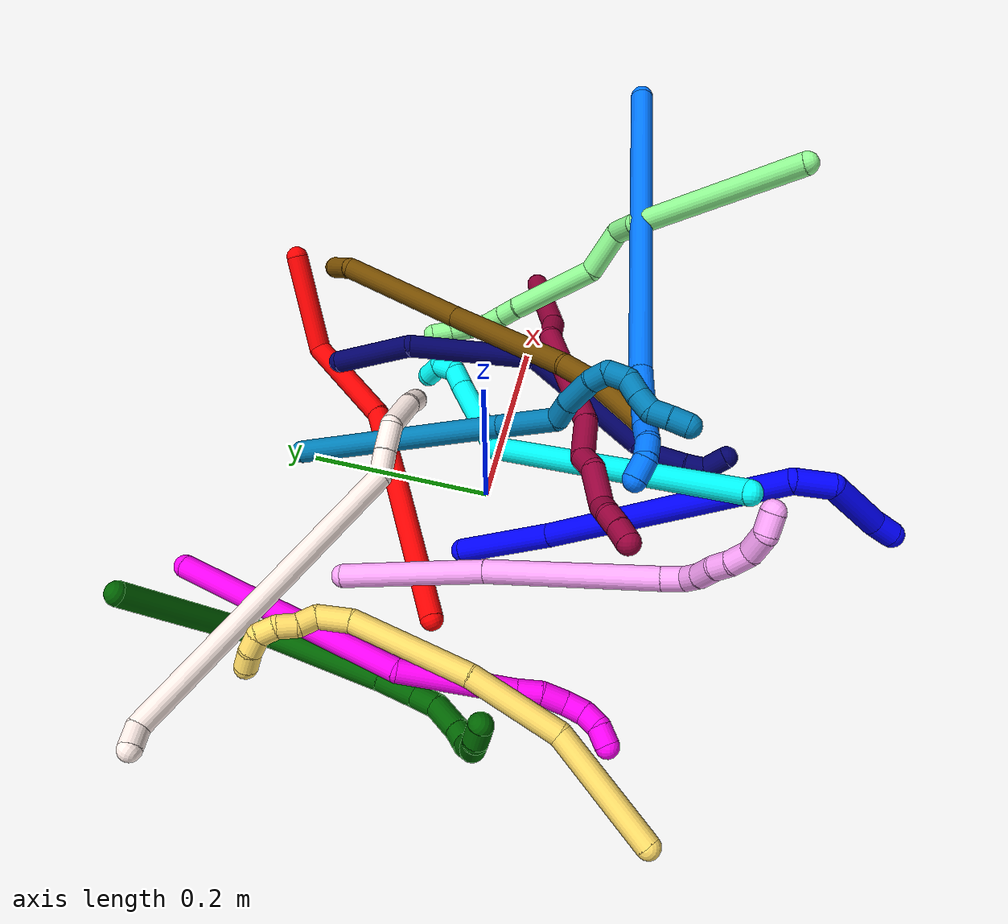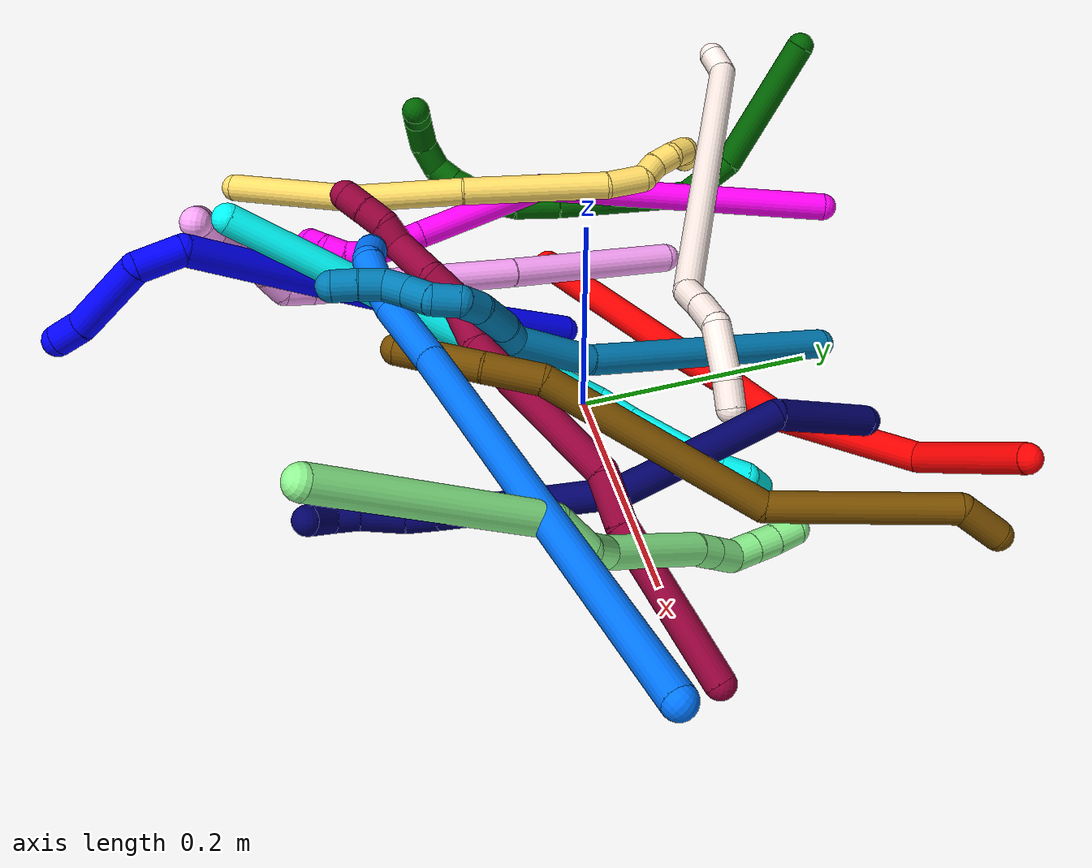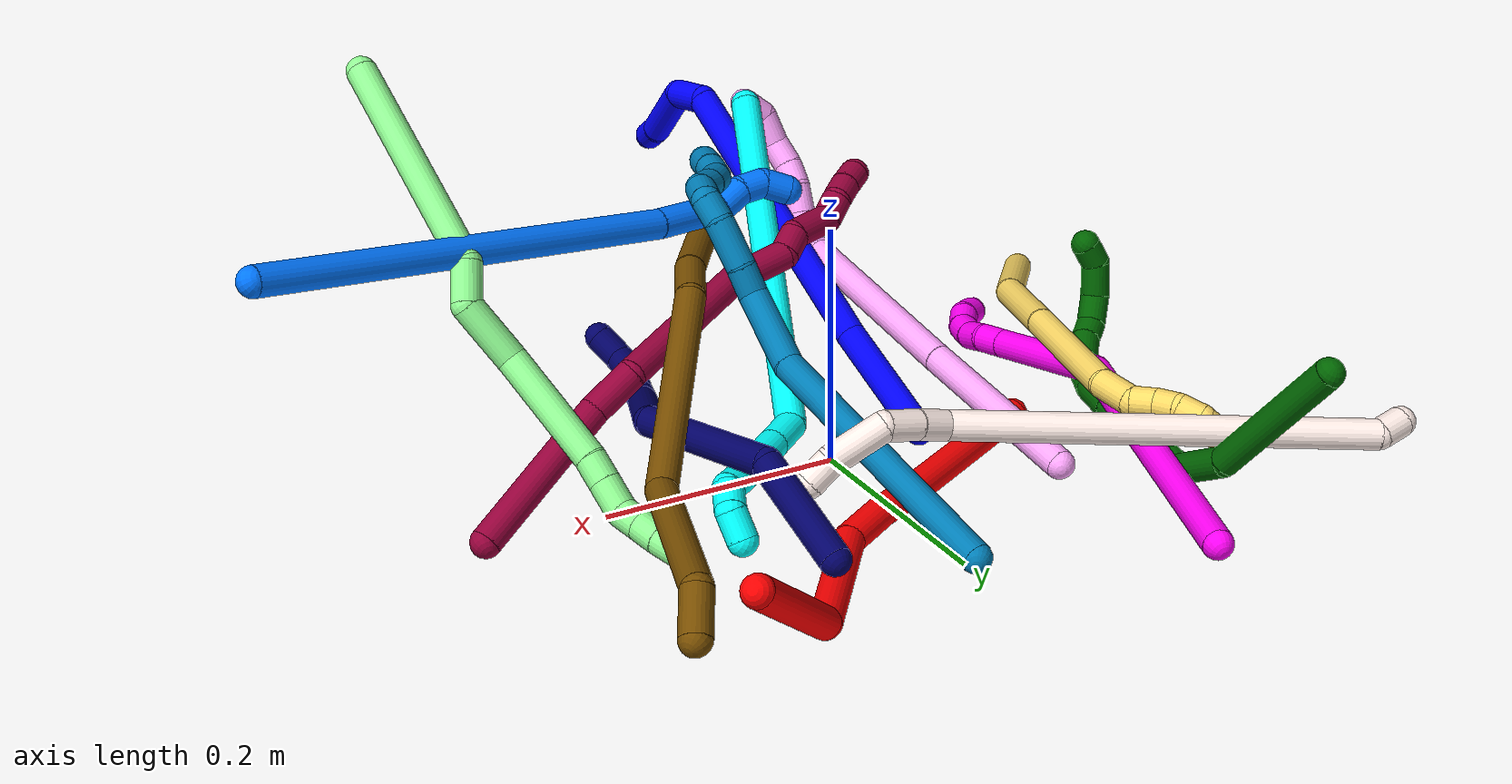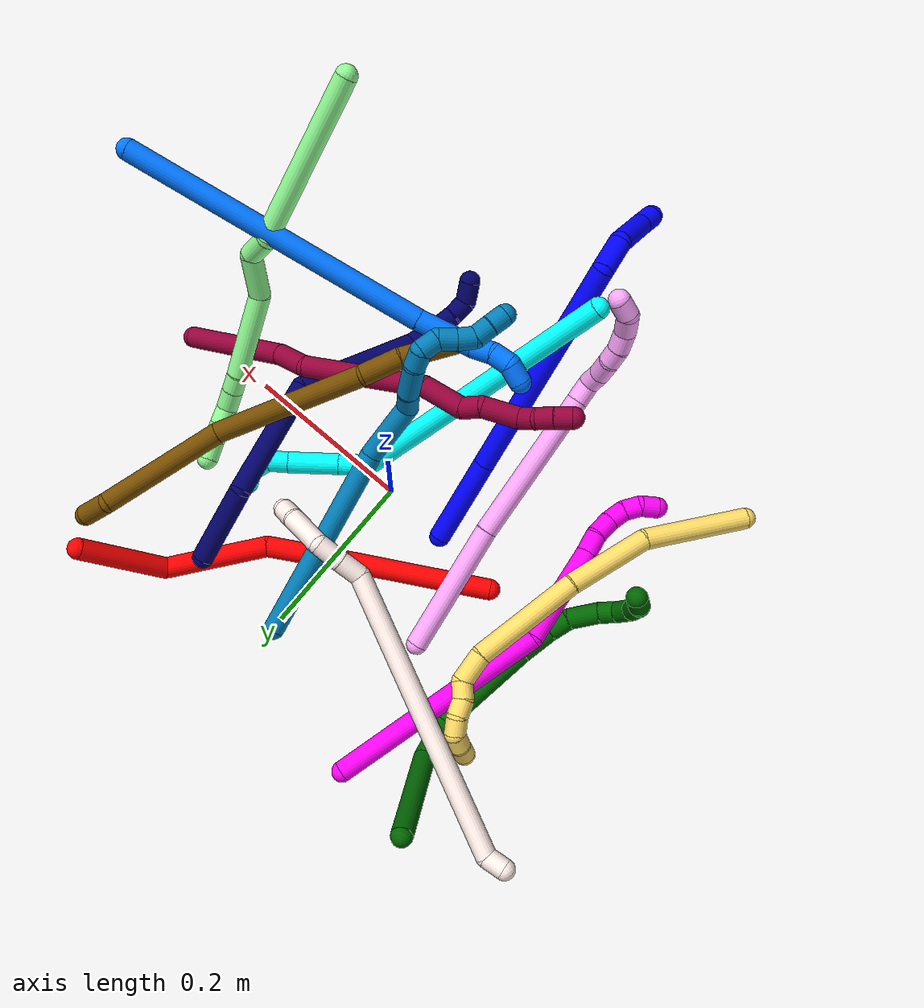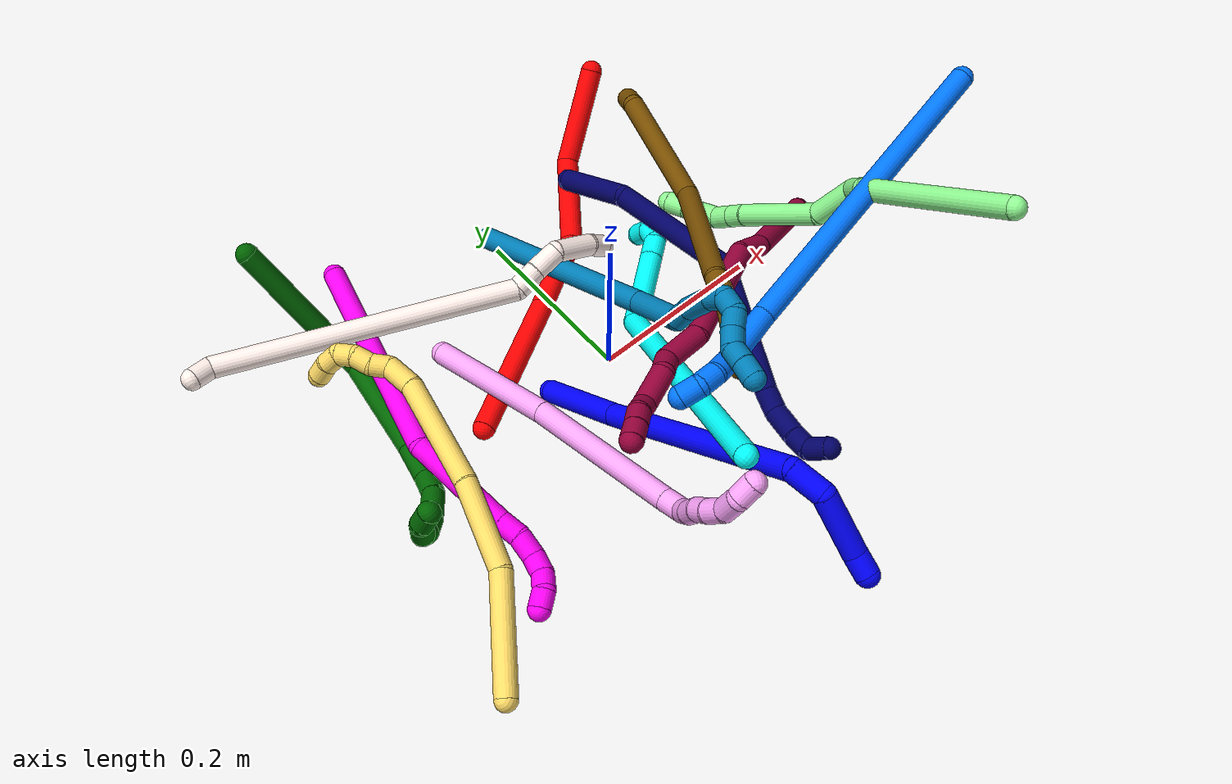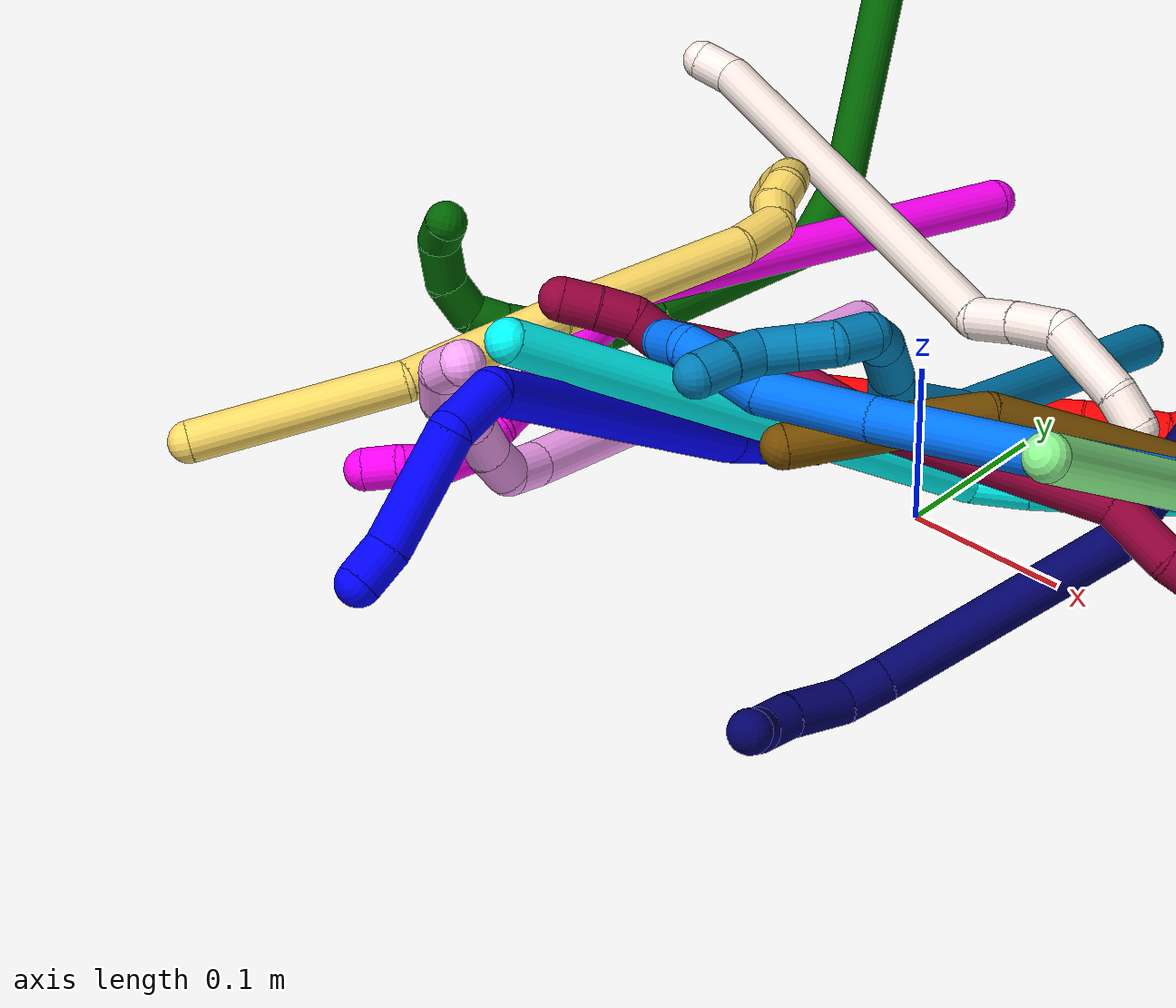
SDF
<sdf version="1.7">
 <world name="default">
  <plugin name="TubeGeneratorPlugin" filename="libtube_generator_plugin.so"/>
  <model name="photoneo_s_sensor">
   <static>1</static>
   <pose>0 0 2 1.57079 1.57079 3.14159</pose>
   <link name="link">
    <inertial><mass>0.1</mass></inertial>
    <sensor name="sensor" type="depth">
     <update_rate>30</update_rate>
     <camera>
      <horizontal_fov>1.22</horizontal_fov>
      <image><width>1920</width><height>1200</height><format>B8G8R8</format></image>
      <clip><near>0.1</near><far>4</far></clip>
      <depth_camera><output>points</output></depth_camera>
     </camera>
     <plugin name="camera_plugin" filename="libgazebo_ros_depth_camera.so">
      <baseline>0.2</baseline>
      <alwaysOn>1</alwaysOn>
      <updateRate>0.0</updateRate>
      <cameraName>camera_ir</cameraName>
      <imageTopicName>/camera/color/image_raw</imageTopicName>
      <cameraInfoTopicName>/camera/color/camera_info</cameraInfoTopicName>
      <depthImageTopicName>/camera/depth/image_raw</depthImageTopicName>
      <depthImageCameraInfoTopicName>/camera/depth/camera_info</depthImageCameraInfoTopicName>
      <pointCloudTopicName>/camera/depth/points</pointCloudTopicName>
      <frameName>fr_optical</frameName>
      <pointCloudCutoff>0.1</pointCloudCutoff>
      <pointCloudCutoffMax>2.0</pointCloudCutoffMax>
      <distortionK1>0</distortionK1>
      <distortionK2>0</distortionK2>
      <distortionK3>0</distortionK3>
      <distortionT1>0</distortionT1>
      <distortionT2>0</distortionT2>
      <CxPrime>0</CxPrime>
      <Cx>0</Cx>
      <Cy>0</Cy>
      <focalLength>0</focalLength>
      <hackBaseline>0</hackBaseline>
     </plugin>
    </sensor>
   </link>
  </model>
  <gravity>0 0 -9.8</gravity>
  <magnetic_field>6e-06 2.3e-05 -4.2e-05</magnetic_field>
  <atmosphere type="adiabatic"/>
  <physics name="default_physics" default="0" type="ode">
   <max_step_size>0.003</max_step_size>
   <real_time_factor>1</real_time_factor>
   <real_time_update_rate>1000</real_time_update_rate>
   <max_contacts>10000</max_contacts>
   <ode>
    <solver>
     <type>quick</type>
     <iters>100</iters>
     <sor>1.3</sor>
     <use_dynamic_moi_rescaling>0</use_dynamic_moi_rescaling>
    </solver>
    <constraints>
     <contact_max_correcting_vel>0</contact_max_correcting_vel>
     <contact_surface_layer>0.001</contact_surface_layer>
     <cfm>0</cfm>
     <erp>0.2</erp>
    </constraints>
   </ode>
  </physics>
  <scene><ambient>0.4 0.4 0.4 1</ambient><background>0.7 0.7 0.7 1</background><shadows>0</shadows></scene>
  <audio><device>default</device></audio>
  <spherical_coordinates>
   <surface_model>EARTH_WGS84</surface_model>
   <latitude_deg>0</latitude_deg>
   <longitude_deg>0</longitude_deg>
   <elevation>0</elevation>
   <heading_deg>0</heading_deg>
  </spherical_coordinates>
  <model name="bin">
   <static>1</static>
   <link name="bottom">
    <collision name="collision-bottom">
     <pose>0 0 -0.01 0 -0 0</pose>
     <geometry><box><size>0.8 0.6 0.02</size></box></geometry>
     <surface>
      <friction><ode><mu>100</mu><mu2>100</mu2></ode></friction>
      <contact><collide_bitmask>65535</collide_bitmask></contact>
     </surface>
    </collision>
   </link>
   <link name="west_wall">
    <collision name="collision-west_wall">
     <pose>-0.41 0 0.1 0 -0 0</pose>
     <geometry><box><size>0.02 0.6 0.2</size></box></geometry>
     <surface>
      <friction><ode><mu>100</mu><mu2>100</mu2></ode></friction>
      <contact><collide_bitmask>65535</collide_bitmask></contact>
     </surface>
    </collision>
   </link>
   <link name="east_wall">
    <collision name="collision-east_wall">
     <pose>0.41 0 0.1 0 -0 0</pose>
     <geometry><box><size>0.02 0.6 0.2</size></box></geometry>
     <surface>
      <friction><ode><mu>100</mu><mu2>100</mu2></ode></friction>
      <contact><collide_bitmask>65535</collide_bitmask></contact>
     </surface>
    </collision>
   </link>
   <link name="south_wall">
    <collision name="collision-south_wall">
     <pose>0 -0.31 0.1 0 -0 0</pose>
     <geometry><box><size>0.8 0.02 0.2</size></box></geometry>
     <surface>
      <friction><ode><mu>100</mu><mu2>100</mu2></ode></friction>
      <contact><collide_bitmask>65535</collide_bitmask></contact>
     </surface>
    </collision>
   </link>
   <link name="north_wall">
    <collision name="collision-north_wall">
     <pose>0 0.31 0.1 0 -0 0</pose>
     <geometry><box><size>0.8 0.02 0.2</size></box></geometry>
     <surface>
      <friction><ode><mu>100</mu><mu2>100</mu2></ode></friction>
      <contact><collide_bitmask>65535</collide_bitmask></contact>
     </surface>
    </collision>
   </link>
  </model>
  <model name="1">
   <static>0</static>
   <link name="1">
    <collision name="collision-cylinder-e_1_1_4">
     <pose>0.000542 -0.017466 0.050607 0.332321 0.010127 0.001698</pose>
     <geometry><cylinder><radius>0.0125</radius><length>0.107078</length></cylinder></geometry>
     <surface>
      <friction><ode><mu>1.16</mu><mu2>1.16</mu2><slip1>0</slip1><slip2>0</slip2></ode></friction>
      <contact><ode><kp>1e+06</kp><kd>1</kd><max_vel>0</max_vel><min_depth>0.001</min_depth></ode></contact>
     </surface>
    </collision>
    <visual name="visual-cylinder-e_1_1_4">
     <pose>0.000542 -0.017466 0.050607 0.332321 0.010127 0.001698</pose>
     <geometry><cylinder><radius>0.0125</radius><length>0.107078</length></cylinder></geometry>
     <material><ambient>0 0 1 1</ambient></material>
    </visual>
    <collision name="collision-cylinder-e_2_4_5">
     <pose>0.008931 -0.07005 0.228775 0.268658 0.059238 0.008008</pose>
     <geometry><cylinder><radius>0.0125</radius><length>0.265078</length></cylinder></geometry>
     <surface>
      <friction><ode><mu>1.16</mu><mu2>1.16</mu2><slip1>0</slip1><slip2>0</slip2></ode></friction>
      <contact><ode><kp>1e+06</kp><kd>1</kd><max_vel>0</max_vel><min_depth>0.001</min_depth></ode></contact>
     </surface>
    </collision>
    <visual name="visual-cylinder-e_2_4_5">
     <pose>0.008931 -0.07005 0.228775 0.268658 0.059238 0.008008</pose>
     <geometry><cylinder><radius>0.0125</radius><length>0.265078</length></cylinder></geometry>
     <material><ambient>0 0 1 1</ambient></material>
    </visual>
    <collision name="collision-cylinder-e_3_5_6">
     <pose>0.009843 -0.118156 0.368008 0.83862 -0.378052 -0.170139</pose>
     <geometry><cylinder><radius>0.0125</radius><length>0.037578</length></cylinder></geometry>
     <surface>
      <friction><ode><mu>1.16</mu><mu2>1.16</mu2><slip1>0</slip1><slip2>0</slip2></ode></friction>
      <contact><ode><kp>1e+06</kp><kd>1</kd><max_vel>0</max_vel><min_depth>0.001</min_depth></ode></contact>
     </surface>
    </collision>
    <visual name="visual-cylinder-e_3_5_6">
     <pose>0.009843 -0.118156 0.368008 0.83862 -0.378052 -0.170139</pose>
     <geometry><cylinder><radius>0.0125</radius><length>0.037578</length></cylinder></geometry>
     <material><ambient>0 0 1 1</ambient></material>
    </visual>
    <collision name="collision-cylinder-e_4_6_7">
     <pose>-0.020935 -0.154506 0.381062 1.51176 -0.794696 -0.753412</pose>
     <geometry><cylinder><radius>0.0125</radius><length>0.06682</length></cylinder></geometry>
     <surface>
      <friction><ode><mu>1.16</mu><mu2>1.16</mu2><slip1>0</slip1><slip2>0</slip2></ode></friction>
      <contact><ode><kp>1e+06</kp><kd>1</kd><max_vel>0</max_vel><min_depth>0.001</min_depth></ode></contact>
     </surface>
    </collision>
    <visual name="visual-cylinder-e_4_6_7">
     <pose>-0.020935 -0.154506 0.381062 1.51176 -0.794696 -0.753412</pose>
     <geometry><cylinder><radius>0.0125</radius><length>0.06682</length></cylinder></geometry>
     <material><ambient>0 0 1 1</ambient></material>
    </visual>
    <collision name="collision-cylinder-e_5_7_2">
     <pose>-0.053116 -0.185398 0.385795 1.15195 -0.791196 -0.529679</pose>
     <geometry><cylinder><radius>0.0125</radius><length>0.023447</length></cylinder></geometry>
     <surface>
      <friction><ode><mu>1.16</mu><mu2>1.16</mu2><slip1>0</slip1><slip2>0</slip2></ode></friction>
      <contact><ode><kp>1e+06</kp><kd>1</kd><max_vel>0</max_vel><min_depth>0.001</min_depth></ode></contact>
     </surface>
    </collision>
    <visual name="visual-cylinder-e_5_7_2">
     <pose>-0.053116 -0.185398 0.385795 1.15195 -0.791196 -0.529679</pose>
     <geometry><cylinder><radius>0.0125</radius><length>0.023447</length></cylinder></geometry>
     <material><ambient>0 0 1 1</ambient></material>
    </visual>
    <collision name="collision-sphere-2">
     <pose>-0.061453 -0.192927 0.389147 0 -0 0</pose>
     <geometry><sphere><radius>0.0125</radius></sphere></geometry>
     <surface>
      <friction><ode><mu>1.16</mu><mu2>1.16</mu2><slip1>0</slip1><slip2>0</slip2></ode></friction>
      <contact><ode><kp>1e+06</kp><kd>1</kd><max_vel>0</max_vel><min_depth>0.001</min_depth></ode></contact>
     </surface>
    </collision>
    <visual name="visual-sphere-2">
     <pose>-0.061453 -0.192927 0.389147 0 -0 0</pose>
     <geometry><sphere><radius>0.0125</radius></sphere></geometry>
     <material><ambient>0 0 1 1</ambient></material>
    </visual>
    <collision name="collision-sphere-7">
     <pose>-0.044778 -0.177869 0.382443 0 -0 0</pose>
     <geometry><sphere><radius>0.0125</radius></sphere></geometry>
     <surface>
      <friction><ode><mu>1.16</mu><mu2>1.16</mu2><slip1>0</slip1><slip2>0</slip2></ode></friction>
      <contact><ode><kp>1e+06</kp><kd>1</kd><max_vel>0</max_vel><min_depth>0.001</min_depth></ode></contact>
     </surface>
    </collision>
    <visual name="visual-sphere-7">
     <pose>-0.044778 -0.177869 0.382443 0 -0 0</pose>
     <geometry><sphere><radius>0.0125</radius></sphere></geometry>
     <material><ambient>0 0 1 1</ambient></material>
    </visual>
    <collision name="collision-sphere-6">
     <pose>0.002908 -0.131143 0.379682 0 -0 0</pose>
     <geometry><sphere><radius>0.0125</radius></sphere></geometry>
     <surface>
      <friction><ode><mu>1.16</mu><mu2>1.16</mu2><slip1>0</slip1><slip2>0</slip2></ode></friction>
      <contact><ode><kp>1e+06</kp><kd>1</kd><max_vel>0</max_vel><min_depth>0.001</min_depth></ode></contact>
     </surface>
    </collision>
    <visual name="visual-sphere-6">
     <pose>0.002908 -0.131143 0.379682 0 -0 0</pose>
     <geometry><sphere><radius>0.0125</radius></sphere></geometry>
     <material><ambient>0 0 1 1</ambient></material>
    </visual>
    <collision name="collision-sphere-5">
     <pose>0.016778 -0.105169 0.356335 0 -0 0</pose>
     <geometry><sphere><radius>0.0125</radius></sphere></geometry>
     <surface>
      <friction><ode><mu>1.16</mu><mu2>1.16</mu2><slip1>0</slip1><slip2>0</slip2></ode></friction>
      <contact><ode><kp>1e+06</kp><kd>1</kd><max_vel>0</max_vel><min_depth>0.001</min_depth></ode></contact>
     </surface>
    </collision>
    <visual name="visual-sphere-5">
     <pose>0.016778 -0.105169 0.356335 0 -0 0</pose>
     <geometry><sphere><radius>0.0125</radius></sphere></geometry>
     <material><ambient>0 0 1 1</ambient></material>
    </visual>
    <collision name="collision-sphere-1">
     <geometry><sphere><radius>0.0125</radius></sphere></geometry>
     <surface>
      <friction><ode><mu>1.16</mu><mu2>1.16</mu2><slip1>0</slip1><slip2>0</slip2></ode></friction>
      <contact><ode><kp>1e+06</kp><kd>1</kd><max_vel>0</max_vel><min_depth>0.001</min_depth></ode></contact>
     </surface>
    </collision>
    <visual name="visual-sphere-1">
     <geometry><sphere><radius>0.0125</radius></sphere></geometry>
     <material><ambient>0 0 1 1</ambient></material>
    </visual>
    <collision name="collision-sphere-4">
     <pose>0.001084 -0.034931 0.101214 0 -0 0</pose>
     <geometry><sphere><radius>0.0125</radius></sphere></geometry>
     <surface>
      <friction><ode><mu>1.16</mu><mu2>1.16</mu2><slip1>0</slip1><slip2>0</slip2></ode></friction>
      <contact><ode><kp>1e+06</kp><kd>1</kd><max_vel>0</max_vel><min_depth>0.001</min_depth></ode></contact>
     </surface>
    </collision>
    <visual name="visual-sphere-4">
     <pose>0.001084 -0.034931 0.101214 0 -0 0</pose>
     <geometry><sphere><radius>0.0125</radius></sphere></geometry>
     <material><ambient>0 0 1 1</ambient></material>
    </visual>
    <inertial>
     <pose>0.000302 -0.0791 0.228798 0 -0 0</pose>
     <mass>0.5</mass>
     <inertia><ixx>0.00168</ixx><ixy>0</ixy><ixz>0</ixz><iyy>0.00161</iyy><iyz>0</iyz><izz>0.000433</izz></inertia>
    </inertial>
   </link>
   <pose>-0.079628 0.005748 0.011524 0.577092 -0.633606 0.550475</pose>
  </model>
  <model name="2">
   <static>0</static>
   <link name="2">
    <collision name="collision-cylinder-e_1_1_4">
     <pose>0.045249 0.004113 0.072154 -0.056941 0.559393 -0.016359</pose>
     <geometry><cylinder><radius>0.0125</radius><length>0.170537</length></cylinder></geometry>
     <surface>
      <friction><ode><mu>1.16</mu><mu2>1.16</mu2><slip1>0</slip1><slip2>0</slip2></ode></friction>
      <contact><ode><kp>1e+06</kp><kd>1</kd><max_vel>0</max_vel><min_depth>0.001</min_depth></ode></contact>
     </surface>
    </collision>
    <visual name="visual-cylinder-e_1_1_4">
     <pose>0.045249 0.004113 0.072154 -0.056941 0.559393 -0.016359</pose>
     <geometry><cylinder><radius>0.0125</radius><length>0.170537</length></cylinder></geometry>
     <material><ambient>1 0 0 1</ambient></material>
    </visual>
    <collision name="collision-cylinder-e_2_4_5">
     <pose>0.101672 0.008968 0.164794 -0.036212 0.499045 -0.009229</pose>
     <geometry><cylinder><radius>0.0125</radius><length>0.046693</length></cylinder></geometry>
     <surface>
      <friction><ode><mu>1.16</mu><mu2>1.16</mu2><slip1>0</slip1><slip2>0</slip2></ode></friction>
      <contact><ode><kp>1e+06</kp><kd>1</kd><max_vel>0</max_vel><min_depth>0.001</min_depth></ode></contact>
     </surface>
    </collision>
    <visual name="visual-cylinder-e_2_4_5">
     <pose>0.101672 0.008968 0.164794 -0.036212 0.499045 -0.009229</pose>
     <geometry><cylinder><radius>0.0125</radius><length>0.046693</length></cylinder></geometry>
     <material><ambient>1 0 0 1</ambient></material>
    </visual>
    <collision name="collision-cylinder-e_3_5_6">
     <pose>0.12658 0.011612 0.2055 -0.093755 0.594621 -0.028745</pose>
     <geometry><cylinder><radius>0.0125</radius><length>0.049034</length></cylinder></geometry>
     <surface>
      <friction><ode><mu>1.16</mu><mu2>1.16</mu2><slip1>0</slip1><slip2>0</slip2></ode></friction>
      <contact><ode><kp>1e+06</kp><kd>1</kd><max_vel>0</max_vel><min_depth>0.001</min_depth></ode></contact>
     </surface>
    </collision>
    <visual name="visual-cylinder-e_3_5_6">
     <pose>0.12658 0.011612 0.2055 -0.093755 0.594621 -0.028745</pose>
     <geometry><cylinder><radius>0.0125</radius><length>0.049034</length></cylinder></geometry>
     <material><ambient>1 0 0 1</ambient></material>
    </visual>
    <collision name="collision-cylinder-e_4_6_7">
     <pose>0.161838 0.038472 0.276794 -0.454545 0.361952 -0.084584</pose>
     <geometry><cylinder><radius>0.0125</radius><length>0.121569</length></cylinder></geometry>
     <surface>
      <friction><ode><mu>1.16</mu><mu2>1.16</mu2><slip1>0</slip1><slip2>0</slip2></ode></friction>
      <contact><ode><kp>1e+06</kp><kd>1</kd><max_vel>0</max_vel><min_depth>0.001</min_depth></ode></contact>
     </surface>
    </collision>
    <visual name="visual-cylinder-e_4_6_7">
     <pose>0.161838 0.038472 0.276794 -0.454545 0.361952 -0.084584</pose>
     <geometry><cylinder><radius>0.0125</radius><length>0.121569</length></cylinder></geometry>
     <material><ambient>1 0 0 1</ambient></material>
    </visual>
    <collision name="collision-cylinder-e_5_7_2">
     <pose>0.180739 0.052511 0.382816 0.196155 -0.046797 -0.004605</pose>
     <geometry><cylinder><radius>0.0125</radius><length>0.112167</length></cylinder></geometry>
     <surface>
      <friction><ode><mu>1.16</mu><mu2>1.16</mu2><slip1>0</slip1><slip2>0</slip2></ode></friction>
      <contact><ode><kp>1e+06</kp><kd>1</kd><max_vel>0</max_vel><min_depth>0.001</min_depth></ode></contact>
     </surface>
    </collision>
    <visual name="visual-cylinder-e_5_7_2">
     <pose>0.180739 0.052511 0.382816 0.196155 -0.046797 -0.004605</pose>
     <geometry><cylinder><radius>0.0125</radius><length>0.112167</length></cylinder></geometry>
     <material><ambient>1 0 0 1</ambient></material>
    </visual>
    <collision name="collision-sphere-2">
     <pose>0.178115 0.041593 0.437763 0 -0 0</pose>
     <geometry><sphere><radius>0.0125</radius></sphere></geometry>
     <surface>
      <friction><ode><mu>1.16</mu><mu2>1.16</mu2><slip1>0</slip1><slip2>0</slip2></ode></friction>
      <contact><ode><kp>1e+06</kp><kd>1</kd><max_vel>0</max_vel><min_depth>0.001</min_depth></ode></contact>
     </surface>
    </collision>
    <visual name="visual-sphere-2">
     <pose>0.178115 0.041593 0.437763 0 -0 0</pose>
     <geometry><sphere><radius>0.0125</radius></sphere></geometry>
     <material><ambient>1 0 0 1</ambient></material>
    </visual>
    <collision name="collision-sphere-7">
     <pose>0.183362 0.06343 0.327868 0 -0 0</pose>
     <geometry><sphere><radius>0.0125</radius></sphere></geometry>
     <surface>
      <friction><ode><mu>1.16</mu><mu2>1.16</mu2><slip1>0</slip1><slip2>0</slip2></ode></friction>
      <contact><ode><kp>1e+06</kp><kd>1</kd><max_vel>0</max_vel><min_depth>0.001</min_depth></ode></contact>
     </surface>
    </collision>
    <visual name="visual-sphere-7">
     <pose>0.183362 0.06343 0.327868 0 -0 0</pose>
     <geometry><sphere><radius>0.0125</radius></sphere></geometry>
     <material><ambient>1 0 0 1</ambient></material>
    </visual>
    <collision name="collision-sphere-6">
     <pose>0.140314 0.013513 0.22572 0 -0 0</pose>
     <geometry><sphere><radius>0.0125</radius></sphere></geometry>
     <surface>
      <friction><ode><mu>1.16</mu><mu2>1.16</mu2><slip1>0</slip1><slip2>0</slip2></ode></friction>
      <contact><ode><kp>1e+06</kp><kd>1</kd><max_vel>0</max_vel><min_depth>0.001</min_depth></ode></contact>
     </surface>
    </collision>
    <visual name="visual-sphere-6">
     <pose>0.140314 0.013513 0.22572 0 -0 0</pose>
     <geometry><sphere><radius>0.0125</radius></sphere></geometry>
     <material><ambient>1 0 0 1</ambient></material>
    </visual>
    <collision name="collision-sphere-5">
     <pose>0.112846 0.00971 0.18528 0 -0 0</pose>
     <geometry><sphere><radius>0.0125</radius></sphere></geometry>
     <surface>
      <friction><ode><mu>1.16</mu><mu2>1.16</mu2><slip1>0</slip1><slip2>0</slip2></ode></friction>
      <contact><ode><kp>1e+06</kp><kd>1</kd><max_vel>0</max_vel><min_depth>0.001</min_depth></ode></contact>
     </surface>
    </collision>
    <visual name="visual-sphere-5">
     <pose>0.112846 0.00971 0.18528 0 -0 0</pose>
     <geometry><sphere><radius>0.0125</radius></sphere></geometry>
     <material><ambient>1 0 0 1</ambient></material>
    </visual>
    <collision name="collision-sphere-1">
     <geometry><sphere><radius>0.0125</radius></sphere></geometry>
     <surface>
      <friction><ode><mu>1.16</mu><mu2>1.16</mu2><slip1>0</slip1><slip2>0</slip2></ode></friction>
      <contact><ode><kp>1e+06</kp><kd>1</kd><max_vel>0</max_vel><min_depth>0.001</min_depth></ode></contact>
     </surface>
    </collision>
    <visual name="visual-sphere-1">
     <geometry><sphere><radius>0.0125</radius></sphere></geometry>
     <material><ambient>1 0 0 1</ambient></material>
    </visual>
    <collision name="collision-sphere-4">
     <pose>0.090499 0.008226 0.144309 0 -0 0</pose>
     <geometry><sphere><radius>0.0125</radius></sphere></geometry>
     <surface>
      <friction><ode><mu>1.16</mu><mu2>1.16</mu2><slip1>0</slip1><slip2>0</slip2></ode></friction>
      <contact><ode><kp>1e+06</kp><kd>1</kd><max_vel>0</max_vel><min_depth>0.001</min_depth></ode></contact>
     </surface>
    </collision>
    <visual name="visual-sphere-4">
     <pose>0.090499 0.008226 0.144309 0 -0 0</pose>
     <geometry><sphere><radius>0.0125</radius></sphere></geometry>
     <material><ambient>1 0 0 1</ambient></material>
    </visual>
    <inertial>
     <pose>0.117237 0.024513 0.21333 0 -0 0</pose>
     <mass>0.5</mass>
     <inertia>
      <ixx>0.000635</ixx>
      <ixy>0</ixy>
      <ixz>0</ixz>
      <iyy>0.000686</iyy>
      <iyz>0</iyz>
      <izz>-0.00031</izz>
     </inertia>
    </inertial>
   </link>
   <pose>-0.164543 0.016397 0.011497 -0.692207 0.857531 -0.108972</pose>
  </model>
  <model name="3">
   <static>0</static>
   <link name="3">
    <collision name="collision-cylinder-e_1_1_4">
     <pose>0.124914 0.109505 -0.021065 -1.76084 0.842023 -0.993568</pose>
     <geometry><cylinder><radius>0.0125</radius><length>0.334895</length></cylinder></geometry>
     <surface>
      <friction><ode><mu>1.16</mu><mu2>1.16</mu2><slip1>0</slip1><slip2>0</slip2></ode></friction>
      <contact><ode><kp>1e+06</kp><kd>1</kd><max_vel>0</max_vel><min_depth>0.001</min_depth></ode></contact>
     </surface>
    </collision>
    <visual name="visual-cylinder-e_1_1_4">
     <pose>0.124914 0.109505 -0.021065 -1.76084 0.842023 -0.993568</pose>
     <geometry><cylinder><radius>0.0125</radius><length>0.334895</length></cylinder></geometry>
     <material><ambient>0.003922 1 0.996078 1</ambient></material>
    </visual>
    <collision name="collision-cylinder-e_2_4_5">
     <pose>0.257768 0.226861 -0.054633 -2.5809 0.49336 -1.43716</pose>
     <geometry><cylinder><radius>0.0125</radius><length>0.033527</length></cylinder></geometry>
     <surface>
      <friction><ode><mu>1.16</mu><mu2>1.16</mu2><slip1>0</slip1><slip2>0</slip2></ode></friction>
      <contact><ode><kp>1e+06</kp><kd>1</kd><max_vel>0</max_vel><min_depth>0.001</min_depth></ode></contact>
     </surface>
    </collision>
    <visual name="visual-cylinder-e_2_4_5">
     <pose>0.257768 0.226861 -0.054633 -2.5809 0.49336 -1.43716</pose>
     <geometry><cylinder><radius>0.0125</radius><length>0.033527</length></cylinder></geometry>
     <material><ambient>0.003922 1 0.996078 1</ambient></material>
    </visual>
    <collision name="collision-cylinder-e_3_5_6">
     <pose>0.280607 0.247173 -0.089818 -2.63921 0.522413 -1.61165</pose>
     <geometry><cylinder><radius>0.0125</radius><length>0.059723</length></cylinder></geometry>
     <surface>
      <friction><ode><mu>1.16</mu><mu2>1.16</mu2><slip1>0</slip1><slip2>0</slip2></ode></friction>
      <contact><ode><kp>1e+06</kp><kd>1</kd><max_vel>0</max_vel><min_depth>0.001</min_depth></ode></contact>
     </surface>
    </collision>
    <visual name="visual-cylinder-e_3_5_6">
     <pose>0.280607 0.247173 -0.089818 -2.63921 0.522413 -1.61165</pose>
     <geometry><cylinder><radius>0.0125</radius><length>0.059723</length></cylinder></geometry>
     <material><ambient>0.003922 1 0.996078 1</ambient></material>
    </visual>
    <collision name="collision-cylinder-e_4_6_7">
     <pose>0.301317 0.263539 -0.122234 -2.76007 0.505865 -1.85826</pose>
     <geometry><cylinder><radius>0.0125</radius><length>0.023982</length></cylinder></geometry>
     <surface>
      <friction><ode><mu>1.16</mu><mu2>1.16</mu2><slip1>0</slip1><slip2>0</slip2></ode></friction>
      <contact><ode><kp>1e+06</kp><kd>1</kd><max_vel>0</max_vel><min_depth>0.001</min_depth></ode></contact>
     </surface>
    </collision>
    <visual name="visual-cylinder-e_4_6_7">
     <pose>0.301317 0.263539 -0.122234 -2.76007 0.505865 -1.85826</pose>
     <geometry><cylinder><radius>0.0125</radius><length>0.023982</length></cylinder></geometry>
     <material><ambient>0.003922 1 0.996078 1</ambient></material>
    </visual>
    <collision name="collision-cylinder-e_5_7_8">
     <pose>0.316769 0.273679 -0.135184 -2.04696 0.941812 -1.39191</pose>
     <geometry><cylinder><radius>0.0125</radius><length>0.023846</length></cylinder></geometry>
     <surface>
      <friction><ode><mu>1.16</mu><mu2>1.16</mu2><slip1>0</slip1><slip2>0</slip2></ode></friction>
      <contact><ode><kp>1e+06</kp><kd>1</kd><max_vel>0</max_vel><min_depth>0.001</min_depth></ode></contact>
     </surface>
    </collision>
    <visual name="visual-cylinder-e_5_7_8">
     <pose>0.316769 0.273679 -0.135184 -2.04696 0.941812 -1.39191</pose>
     <geometry><cylinder><radius>0.0125</radius><length>0.023846</length></cylinder></geometry>
     <material><ambient>0.003922 1 0.996078 1</ambient></material>
    </visual>
    <collision name="collision-cylinder-e_6_8_2">
     <pose>0.333341 0.288412 -0.133495 -1.04736 0.614921 -0.362691</pose>
     <geometry><cylinder><radius>0.0125</radius><length>0.024027</length></cylinder></geometry>
     <surface>
      <friction><ode><mu>1.16</mu><mu2>1.16</mu2><slip1>0</slip1><slip2>0</slip2></ode></friction>
      <contact><ode><kp>1e+06</kp><kd>1</kd><max_vel>0</max_vel><min_depth>0.001</min_depth></ode></contact>
     </surface>
    </collision>
    <visual name="visual-cylinder-e_6_8_2">
     <pose>0.333341 0.288412 -0.133495 -1.04736 0.614921 -0.362691</pose>
     <geometry><cylinder><radius>0.0125</radius><length>0.024027</length></cylinder></geometry>
     <material><ambient>0.003922 1 0.996078 1</ambient></material>
    </visual>
    <collision name="collision-sphere-2">
     <pose>0.340271 0.296911 -0.12859 0 -0 0</pose>
     <geometry><sphere><radius>0.0125</radius></sphere></geometry>
     <surface>
      <friction><ode><mu>1.16</mu><mu2>1.16</mu2><slip1>0</slip1><slip2>0</slip2></ode></friction>
      <contact><ode><kp>1e+06</kp><kd>1</kd><max_vel>0</max_vel><min_depth>0.001</min_depth></ode></contact>
     </surface>
    </collision>
    <visual name="visual-sphere-2">
     <pose>0.340271 0.296911 -0.12859 0 -0 0</pose>
     <geometry><sphere><radius>0.0125</radius></sphere></geometry>
     <material><ambient>0.003922 1 0.996078 1</ambient></material>
    </visual>
    <collision name="collision-sphere-4">
     <pose>0.249829 0.21901 -0.04213 0 -0 0</pose>
     <geometry><sphere><radius>0.0125</radius></sphere></geometry>
     <surface>
      <friction><ode><mu>1.16</mu><mu2>1.16</mu2><slip1>0</slip1><slip2>0</slip2></ode></friction>
      <contact><ode><kp>1e+06</kp><kd>1</kd><max_vel>0</max_vel><min_depth>0.001</min_depth></ode></contact>
     </surface>
    </collision>
    <visual name="visual-sphere-4">
     <pose>0.249829 0.21901 -0.04213 0 -0 0</pose>
     <geometry><sphere><radius>0.0125</radius></sphere></geometry>
     <material><ambient>0.003922 1 0.996078 1</ambient></material>
    </visual>
    <collision name="collision-sphere-1">
     <geometry><sphere><radius>0.0125</radius></sphere></geometry>
     <surface>
      <friction><ode><mu>1.16</mu><mu2>1.16</mu2><slip1>0</slip1><slip2>0</slip2></ode></friction>
      <contact><ode><kp>1e+06</kp><kd>1</kd><max_vel>0</max_vel><min_depth>0.001</min_depth></ode></contact>
     </surface>
    </collision>
    <visual name="visual-sphere-1">
     <geometry><sphere><radius>0.0125</radius></sphere></geometry>
     <material><ambient>0.003922 1 0.996078 1</ambient></material>
    </visual>
    <collision name="collision-sphere-8">
     <pose>0.32641 0.279913 -0.1384 0 -0 0</pose>
     <geometry><sphere><radius>0.0125</radius></sphere></geometry>
     <surface>
      <friction><ode><mu>1.16</mu><mu2>1.16</mu2><slip1>0</slip1><slip2>0</slip2></ode></friction>
      <contact><ode><kp>1e+06</kp><kd>1</kd><max_vel>0</max_vel><min_depth>0.001</min_depth></ode></contact>
     </surface>
    </collision>
    <visual name="visual-sphere-8">
     <pose>0.32641 0.279913 -0.1384 0 -0 0</pose>
     <geometry><sphere><radius>0.0125</radius></sphere></geometry>
     <material><ambient>0.003922 1 0.996078 1</ambient></material>
    </visual>
    <collision name="collision-sphere-5">
     <pose>0.265707 0.234712 -0.067137 0 -0 0</pose>
     <geometry><sphere><radius>0.0125</radius></sphere></geometry>
     <surface>
      <friction><ode><mu>1.16</mu><mu2>1.16</mu2><slip1>0</slip1><slip2>0</slip2></ode></friction>
      <contact><ode><kp>1e+06</kp><kd>1</kd><max_vel>0</max_vel><min_depth>0.001</min_depth></ode></contact>
     </surface>
    </collision>
    <visual name="visual-sphere-5">
     <pose>0.265707 0.234712 -0.067137 0 -0 0</pose>
     <geometry><sphere><radius>0.0125</radius></sphere></geometry>
     <material><ambient>0.003922 1 0.996078 1</ambient></material>
    </visual>
    <collision name="collision-sphere-6">
     <pose>0.295507 0.259634 -0.112499 0 -0 0</pose>
     <geometry><sphere><radius>0.0125</radius></sphere></geometry>
     <surface>
      <friction><ode><mu>1.16</mu><mu2>1.16</mu2><slip1>0</slip1><slip2>0</slip2></ode></friction>
      <contact><ode><kp>1e+06</kp><kd>1</kd><max_vel>0</max_vel><min_depth>0.001</min_depth></ode></contact>
     </surface>
    </collision>
    <visual name="visual-sphere-6">
     <pose>0.295507 0.259634 -0.112499 0 -0 0</pose>
     <geometry><sphere><radius>0.0125</radius></sphere></geometry>
     <material><ambient>0.003922 1 0.996078 1</ambient></material>
    </visual>
    <collision name="collision-sphere-7">
     <pose>0.307128 0.267445 -0.131969 0 -0 0</pose>
     <geometry><sphere><radius>0.0125</radius></sphere></geometry>
     <surface>
      <friction><ode><mu>1.16</mu><mu2>1.16</mu2><slip1>0</slip1><slip2>0</slip2></ode></friction>
      <contact><ode><kp>1e+06</kp><kd>1</kd><max_vel>0</max_vel><min_depth>0.001</min_depth></ode></contact>
     </surface>
    </collision>
    <visual name="visual-sphere-7">
     <pose>0.307128 0.267445 -0.131969 0 -0 0</pose>
     <geometry><sphere><radius>0.0125</radius></sphere></geometry>
     <material><ambient>0.003922 1 0.996078 1</ambient></material>
    </visual>
    <inertial>
     <pose>0.180046 0.157633 -0.047226 0 -0 0</pose>
     <mass>0.5</mass>
     <inertia>
      <ixx>-0.000609</ixx>
      <ixy>0</ixy>
      <ixz>0</ixz>
      <iyy>-0.000141</iyy>
      <iyz>0</iyz>
      <izz>-0.00444</izz>
     </inertia>
    </inertial>
   </link>
   <pose>-0.065135 -0.265795 0.218138 -2.04579 0.004142 1.70986</pose>
  </model>
  <model name="4">
   <static>0</static>
   <link name="4">
    <collision name="collision-cylinder-e_1_1_4">
     <pose>-0.004289 -0.047497 0.061721 0.655899 -0.055013 -0.018722</pose>
     <geometry><cylinder><radius>0.0125</radius><length>0.155998</length></cylinder></geometry>
     <surface>
      <friction><ode><mu>1.16</mu><mu2>1.16</mu2><slip1>0</slip1><slip2>0</slip2></ode></friction>
      <contact><ode><kp>1e+06</kp><kd>1</kd><max_vel>0</max_vel><min_depth>0.001</min_depth></ode></contact>
     </surface>
    </collision>
    <visual name="visual-cylinder-e_1_1_4">
     <pose>-0.004289 -0.047497 0.061721 0.655899 -0.055013 -0.018722</pose>
     <geometry><cylinder><radius>0.0125</radius><length>0.155998</length></cylinder></geometry>
     <material><ambient>1 0.65098 0.996078 1</ambient></material>
    </visual>
    <collision name="collision-cylinder-e_2_4_5">
     <pose>-0.014222 -0.144999 0.198518 0.587569 -0.062495 -0.018913</pose>
     <geometry><cylinder><radius>0.0125</radius><length>0.180763</length></cylinder></geometry>
     <surface>
      <friction><ode><mu>1.16</mu><mu2>1.16</mu2><slip1>0</slip1><slip2>0</slip2></ode></friction>
      <contact><ode><kp>1e+06</kp><kd>1</kd><max_vel>0</max_vel><min_depth>0.001</min_depth></ode></contact>
     </surface>
    </collision>
    <visual name="visual-cylinder-e_2_4_5">
     <pose>-0.014222 -0.144999 0.198518 0.587569 -0.062495 -0.018913</pose>
     <geometry><cylinder><radius>0.0125</radius><length>0.180763</length></cylinder></geometry>
     <material><ambient>1 0.65098 0.996078 1</ambient></material>
    </visual>
    <collision name="collision-cylinder-e_3_5_6">
     <pose>-0.01994 -0.201941 0.283299 0.620655 -0.006141 -0.001969</pose>
     <geometry><cylinder><radius>0.0125</radius><length>0.023858</length></cylinder></geometry>
     <surface>
      <friction><ode><mu>1.16</mu><mu2>1.16</mu2><slip1>0</slip1><slip2>0</slip2></ode></friction>
      <contact><ode><kp>1e+06</kp><kd>1</kd><max_vel>0</max_vel><min_depth>0.001</min_depth></ode></contact>
     </surface>
    </collision>
    <visual name="visual-cylinder-e_3_5_6">
     <pose>-0.01994 -0.201941 0.283299 0.620655 -0.006141 -0.001969</pose>
     <geometry><cylinder><radius>0.0125</radius><length>0.023858</length></cylinder></geometry>
     <material><ambient>1 0.65098 0.996078 1</ambient></material>
    </visual>
    <collision name="collision-cylinder-e_4_6_7">
     <pose>-0.012805 -0.214445 0.298979 0.74996 0.723099 0.29553</pose>
     <geometry><cylinder><radius>0.0125</radius><length>0.021787</length></cylinder></geometry>
     <surface>
      <friction><ode><mu>1.16</mu><mu2>1.16</mu2><slip1>0</slip1><slip2>0</slip2></ode></friction>
      <contact><ode><kp>1e+06</kp><kd>1</kd><max_vel>0</max_vel><min_depth>0.001</min_depth></ode></contact>
     </surface>
    </collision>
    <visual name="visual-cylinder-e_4_6_7">
     <pose>-0.012805 -0.214445 0.298979 0.74996 0.723099 0.29553</pose>
     <geometry><cylinder><radius>0.0125</radius><length>0.021787</length></cylinder></geometry>
     <material><ambient>1 0.65098 0.996078 1</ambient></material>
    </visual>
    <collision name="collision-cylinder-e_5_7_8">
     <pose>0.003375 -0.227687 0.310054 0.984472 0.7721 0.42921</pose>
     <geometry><cylinder><radius>0.0125</radius><length>0.025721</length></cylinder></geometry>
     <surface>
      <friction><ode><mu>1.16</mu><mu2>1.16</mu2><slip1>0</slip1><slip2>0</slip2></ode></friction>
      <contact><ode><kp>1e+06</kp><kd>1</kd><max_vel>0</max_vel><min_depth>0.001</min_depth></ode></contact>
     </surface>
    </collision>
    <visual name="visual-cylinder-e_5_7_8">
     <pose>0.003375 -0.227687 0.310054 0.984472 0.7721 0.42921</pose>
     <geometry><cylinder><radius>0.0125</radius><length>0.025721</length></cylinder></geometry>
     <material><ambient>1 0.65098 0.996078 1</ambient></material>
    </visual>
    <collision name="collision-cylinder-e_6_8_9">
     <pose>0.017368 -0.24185 0.320886 0.846985 0.525512 0.241313</pose>
     <geometry><cylinder><radius>0.0125</radius><length>0.020019</length></cylinder></geometry>
     <surface>
      <friction><ode><mu>1.16</mu><mu2>1.16</mu2><slip1>0</slip1><slip2>0</slip2></ode></friction>
      <contact><ode><kp>1e+06</kp><kd>1</kd><max_vel>0</max_vel><min_depth>0.001</min_depth></ode></contact>
     </surface>
    </collision>
    <visual name="visual-cylinder-e_6_8_9">
     <pose>0.017368 -0.24185 0.320886 0.846985 0.525512 0.241313</pose>
     <geometry><cylinder><radius>0.0125</radius><length>0.020019</length></cylinder></geometry>
     <material><ambient>1 0.65098 0.996078 1</ambient></material>
    </visual>
    <collision name="collision-cylinder-e_7_9_10">
     <pose>0.026878 -0.257563 0.331889 1.0519 0.399754 0.234118</pose>
     <geometry><cylinder><radius>0.0125</radius><length>0.023067</length></cylinder></geometry>
     <surface>
      <friction><ode><mu>1.16</mu><mu2>1.16</mu2><slip1>0</slip1><slip2>0</slip2></ode></friction>
      <contact><ode><kp>1e+06</kp><kd>1</kd><max_vel>0</max_vel><min_depth>0.001</min_depth></ode></contact>
     </surface>
    </collision>
    <visual name="visual-cylinder-e_7_9_10">
     <pose>0.026878 -0.257563 0.331889 1.0519 0.399754 0.234118</pose>
     <geometry><cylinder><radius>0.0125</radius><length>0.023067</length></cylinder></geometry>
     <material><ambient>1 0.65098 0.996078 1</ambient></material>
    </visual>
    <collision name="collision-cylinder-e_8_10_11">
     <pose>0.039649 -0.277455 0.339046 1.39562 0.652749 0.553119</pose>
     <geometry><cylinder><radius>0.0125</radius><length>0.027271</length></cylinder></geometry>
     <surface>
      <friction><ode><mu>1.16</mu><mu2>1.16</mu2><slip1>0</slip1><slip2>0</slip2></ode></friction>
      <contact><ode><kp>1e+06</kp><kd>1</kd><max_vel>0</max_vel><min_depth>0.001</min_depth></ode></contact>
     </surface>
    </collision>
    <visual name="visual-cylinder-e_8_10_11">
     <pose>0.039649 -0.277455 0.339046 1.39562 0.652749 0.553119</pose>
     <geometry><cylinder><radius>0.0125</radius><length>0.027271</length></cylinder></geometry>
     <material><ambient>1 0.65098 0.996078 1</ambient></material>
    </visual>
    <collision name="collision-cylinder-e_9_11_2">
     <pose>0.049913 -0.29836 0.338288 1.82369 0.185323 0.238848</pose>
     <geometry><cylinder><radius>0.0125</radius><length>0.021517</length></cylinder></geometry>
     <surface>
      <friction><ode><mu>1.16</mu><mu2>1.16</mu2><slip1>0</slip1><slip2>0</slip2></ode></friction>
      <contact><ode><kp>1e+06</kp><kd>1</kd><max_vel>0</max_vel><min_depth>0.001</min_depth></ode></contact>
     </surface>
    </collision>
    <visual name="visual-cylinder-e_9_11_2">
     <pose>0.049913 -0.29836 0.338288 1.82369 0.185323 0.238848</pose>
     <geometry><cylinder><radius>0.0125</radius><length>0.021517</length></cylinder></geometry>
     <material><ambient>1 0.65098 0.996078 1</ambient></material>
    </visual>
    <collision name="collision-sphere-2">
     <pose>0.051895 -0.308598 0.335642 0 -0 0</pose>
     <geometry><sphere><radius>0.0125</radius></sphere></geometry>
     <surface>
      <friction><ode><mu>1.16</mu><mu2>1.16</mu2><slip1>0</slip1><slip2>0</slip2></ode></friction>
      <contact><ode><kp>1e+06</kp><kd>1</kd><max_vel>0</max_vel><min_depth>0.001</min_depth></ode></contact>
     </surface>
    </collision>
    <visual name="visual-sphere-2">
     <pose>0.051895 -0.308598 0.335642 0 -0 0</pose>
     <geometry><sphere><radius>0.0125</radius></sphere></geometry>
     <material><ambient>1 0.65098 0.996078 1</ambient></material>
    </visual>
    <collision name="collision-sphere-11">
     <pose>0.047931 -0.288122 0.340933 0 -0 0</pose>
     <geometry><sphere><radius>0.0125</radius></sphere></geometry>
     <surface>
      <friction><ode><mu>1.16</mu><mu2>1.16</mu2><slip1>0</slip1><slip2>0</slip2></ode></friction>
      <contact><ode><kp>1e+06</kp><kd>1</kd><max_vel>0</max_vel><min_depth>0.001</min_depth></ode></contact>
     </surface>
    </collision>
    <visual name="visual-sphere-11">
     <pose>0.047931 -0.288122 0.340933 0 -0 0</pose>
     <geometry><sphere><radius>0.0125</radius></sphere></geometry>
     <material><ambient>1 0.65098 0.996078 1</ambient></material>
    </visual>
    <collision name="collision-sphere-10">
     <pose>0.031367 -0.266789 0.337158 0 -0 0</pose>
     <geometry><sphere><radius>0.0125</radius></sphere></geometry>
     <surface>
      <friction><ode><mu>1.16</mu><mu2>1.16</mu2><slip1>0</slip1><slip2>0</slip2></ode></friction>
      <contact><ode><kp>1e+06</kp><kd>1</kd><max_vel>0</max_vel><min_depth>0.001</min_depth></ode></contact>
     </surface>
    </collision>
    <visual name="visual-sphere-10">
     <pose>0.031367 -0.266789 0.337158 0 -0 0</pose>
     <geometry><sphere><radius>0.0125</radius></sphere></geometry>
     <material><ambient>1 0.65098 0.996078 1</ambient></material>
    </visual>
    <collision name="collision-sphere-9">
     <pose>0.02239 -0.248338 0.32662 0 -0 0</pose>
     <geometry><sphere><radius>0.0125</radius></sphere></geometry>
     <surface>
      <friction><ode><mu>1.16</mu><mu2>1.16</mu2><slip1>0</slip1><slip2>0</slip2></ode></friction>
      <contact><ode><kp>1e+06</kp><kd>1</kd><max_vel>0</max_vel><min_depth>0.001</min_depth></ode></contact>
     </surface>
    </collision>
    <visual name="visual-sphere-9">
     <pose>0.02239 -0.248338 0.32662 0 -0 0</pose>
     <geometry><sphere><radius>0.0125</radius></sphere></geometry>
     <material><ambient>1 0.65098 0.996078 1</ambient></material>
    </visual>
    <collision name="collision-sphere-4">
     <pose>-0.008578 -0.094995 0.123441 0 -0 0</pose>
     <geometry><sphere><radius>0.0125</radius></sphere></geometry>
     <surface>
      <friction><ode><mu>1.16</mu><mu2>1.16</mu2><slip1>0</slip1><slip2>0</slip2></ode></friction>
      <contact><ode><kp>1e+06</kp><kd>1</kd><max_vel>0</max_vel><min_depth>0.001</min_depth></ode></contact>
     </surface>
    </collision>
    <visual name="visual-sphere-4">
     <pose>-0.008578 -0.094995 0.123441 0 -0 0</pose>
     <geometry><sphere><radius>0.0125</radius></sphere></geometry>
     <material><ambient>1 0.65098 0.996078 1</ambient></material>
    </visual>
    <collision name="collision-sphere-1">
     <geometry><sphere><radius>0.0125</radius></sphere></geometry>
     <surface>
      <friction><ode><mu>1.16</mu><mu2>1.16</mu2><slip1>0</slip1><slip2>0</slip2></ode></friction>
      <contact><ode><kp>1e+06</kp><kd>1</kd><max_vel>0</max_vel><min_depth>0.001</min_depth></ode></contact>
     </surface>
    </collision>
    <visual name="visual-sphere-1">
     <geometry><sphere><radius>0.0125</radius></sphere></geometry>
     <material><ambient>1 0.65098 0.996078 1</ambient></material>
    </visual>
    <collision name="collision-sphere-8">
     <pose>0.012347 -0.235362 0.315152 0 -0 0</pose>
     <geometry><sphere><radius>0.0125</radius></sphere></geometry>
     <surface>
      <friction><ode><mu>1.16</mu><mu2>1.16</mu2><slip1>0</slip1><slip2>0</slip2></ode></friction>
      <contact><ode><kp>1e+06</kp><kd>1</kd><max_vel>0</max_vel><min_depth>0.001</min_depth></ode></contact>
     </surface>
    </collision>
    <visual name="visual-sphere-8">
     <pose>0.012347 -0.235362 0.315152 0 -0 0</pose>
     <geometry><sphere><radius>0.0125</radius></sphere></geometry>
     <material><ambient>1 0.65098 0.996078 1</ambient></material>
    </visual>
    <collision name="collision-sphere-5">
     <pose>-0.019867 -0.195004 0.273595 0 -0 0</pose>
     <geometry><sphere><radius>0.0125</radius></sphere></geometry>
     <surface>
      <friction><ode><mu>1.16</mu><mu2>1.16</mu2><slip1>0</slip1><slip2>0</slip2></ode></friction>
      <contact><ode><kp>1e+06</kp><kd>1</kd><max_vel>0</max_vel><min_depth>0.001</min_depth></ode></contact>
     </surface>
    </collision>
    <visual name="visual-sphere-5">
     <pose>-0.019867 -0.195004 0.273595 0 -0 0</pose>
     <geometry><sphere><radius>0.0125</radius></sphere></geometry>
     <material><ambient>1 0.65098 0.996078 1</ambient></material>
    </visual>
    <collision name="collision-sphere-6">
     <pose>-0.020014 -0.208878 0.293003 0 -0 0</pose>
     <geometry><sphere><radius>0.0125</radius></sphere></geometry>
     <surface>
      <friction><ode><mu>1.16</mu><mu2>1.16</mu2><slip1>0</slip1><slip2>0</slip2></ode></friction>
      <contact><ode><kp>1e+06</kp><kd>1</kd><max_vel>0</max_vel><min_depth>0.001</min_depth></ode></contact>
     </surface>
    </collision>
    <visual name="visual-sphere-6">
     <pose>-0.020014 -0.208878 0.293003 0 -0 0</pose>
     <geometry><sphere><radius>0.0125</radius></sphere></geometry>
     <material><ambient>1 0.65098 0.996078 1</ambient></material>
    </visual>
    <collision name="collision-sphere-7">
     <pose>-0.005597 -0.220012 0.304956 0 -0 0</pose>
     <geometry><sphere><radius>0.0125</radius></sphere></geometry>
     <surface>
      <friction><ode><mu>1.16</mu><mu2>1.16</mu2><slip1>0</slip1><slip2>0</slip2></ode></friction>
      <contact><ode><kp>1e+06</kp><kd>1</kd><max_vel>0</max_vel><min_depth>0.001</min_depth></ode></contact>
     </surface>
    </collision>
    <visual name="visual-sphere-7">
     <pose>-0.005597 -0.220012 0.304956 0 -0 0</pose>
     <geometry><sphere><radius>0.0125</radius></sphere></geometry>
     <material><ambient>1 0.65098 0.996078 1</ambient></material>
    </visual>
    <inertial>
     <pose>-0.00157 -0.14747 0.19473 0 -0 0</pose>
     <mass>0.5</mass>
     <inertia>
      <ixx>0.000823</ixx>
      <ixy>0</ixy>
      <ixz>0</ixz>
      <iyy>0.000643</iyy>
      <iyz>0</iyz>
      <izz>0.000551</izz>
     </inertia>
    </inertial>
   </link>
   <pose>-0.140605 0.120225 0.0147 -1.57941 -1.05279 2.68087</pose>
  </model>
  <model name="5">
   <static>0</static>
   <link name="5">
    <collision name="collision-cylinder-e_1_1_4">
     <pose>0.034523 0.053909 0.007248 -1.43715 0.565531 -0.497671</pose>
     <geometry><cylinder><radius>0.0125</radius><length>0.128849</length></cylinder></geometry>
     <surface>
      <friction><ode><mu>1.16</mu><mu2>1.16</mu2><slip1>0</slip1><slip2>0</slip2></ode></friction>
      <contact><ode><kp>1e+06</kp><kd>1</kd><max_vel>0</max_vel><min_depth>0.001</min_depth></ode></contact>
     </surface>
    </collision>
    <visual name="visual-cylinder-e_1_1_4">
     <pose>0.034523 0.053909 0.007248 -1.43715 0.565531 -0.497671</pose>
     <geometry><cylinder><radius>0.0125</radius><length>0.128849</length></cylinder></geometry>
     <material><ambient>1 0.858824 0.4 1</ambient></material>
    </visual>
    <collision name="collision-cylinder-e_2_4_5">
     <pose>0.081215 0.156047 0.025498 -1.34651 0.241224 -0.192732</pose>
     <geometry><cylinder><radius>0.0125</radius><length>0.101888</length></cylinder></geometry>
     <surface>
      <friction><ode><mu>1.16</mu><mu2>1.16</mu2><slip1>0</slip1><slip2>0</slip2></ode></friction>
      <contact><ode><kp>1e+06</kp><kd>1</kd><max_vel>0</max_vel><min_depth>0.001</min_depth></ode></contact>
     </surface>
    </collision>
    <visual name="visual-cylinder-e_2_4_5">
     <pose>0.081215 0.156047 0.025498 -1.34651 0.241224 -0.192732</pose>
     <geometry><cylinder><radius>0.0125</radius><length>0.101888</length></cylinder></geometry>
     <material><ambient>1 0.858824 0.4 1</ambient></material>
    </visual>
    <collision name="collision-cylinder-e_3_5_6">
     <pose>0.099423 0.268874 0.047596 -1.40068 0.091863 -0.077445</pose>
     <geometry><cylinder><radius>0.0125</radius><length>0.13164</length></cylinder></geometry>
     <surface>
      <friction><ode><mu>1.16</mu><mu2>1.16</mu2><slip1>0</slip1><slip2>0</slip2></ode></friction>
      <contact><ode><kp>1e+06</kp><kd>1</kd><max_vel>0</max_vel><min_depth>0.001</min_depth></ode></contact>
     </surface>
    </collision>
    <visual name="visual-cylinder-e_3_5_6">
     <pose>0.099423 0.268874 0.047596 -1.40068 0.091863 -0.077445</pose>
     <geometry><cylinder><radius>0.0125</radius><length>0.13164</length></cylinder></geometry>
     <material><ambient>1 0.858824 0.4 1</ambient></material>
    </visual>
    <collision name="collision-cylinder-e_4_6_7">
     <pose>0.102005 0.350632 0.063293 -1.30885 -0.192106 0.147572</pose>
     <geometry><cylinder><radius>0.0125</radius><length>0.036202</length></cylinder></geometry>
     <surface>
      <friction><ode><mu>1.16</mu><mu2>1.16</mu2><slip1>0</slip1><slip2>0</slip2></ode></friction>
      <contact><ode><kp>1e+06</kp><kd>1</kd><max_vel>0</max_vel><min_depth>0.001</min_depth></ode></contact>
     </surface>
    </collision>
    <visual name="visual-cylinder-e_4_6_7">
     <pose>0.102005 0.350632 0.063293 -1.30885 -0.192106 0.147572</pose>
     <geometry><cylinder><radius>0.0125</radius><length>0.036202</length></cylinder></geometry>
     <material><ambient>1 0.858824 0.4 1</ambient></material>
    </visual>
    <collision name="collision-cylinder-e_5_7_8">
     <pose>0.091988 0.373582 0.073588 -0.79361 -0.679739 0.294191</pose>
     <geometry><cylinder><radius>0.0125</radius><length>0.020877</length></cylinder></geometry>
     <surface>
      <friction><ode><mu>1.16</mu><mu2>1.16</mu2><slip1>0</slip1><slip2>0</slip2></ode></friction>
      <contact><ode><kp>1e+06</kp><kd>1</kd><max_vel>0</max_vel><min_depth>0.001</min_depth></ode></contact>
     </surface>
    </collision>
    <visual name="visual-cylinder-e_5_7_8">
     <pose>0.091988 0.373582 0.073588 -0.79361 -0.679739 0.294191</pose>
     <geometry><cylinder><radius>0.0125</radius><length>0.020877</length></cylinder></geometry>
     <material><ambient>1 0.858824 0.4 1</ambient></material>
    </visual>
    <collision name="collision-cylinder-e_6_8_9">
     <pose>0.081887 0.387581 0.08418 -1.03293 -0.354469 0.202733</pose>
     <geometry><cylinder><radius>0.0125</radius><length>0.020392</length></cylinder></geometry>
     <surface>
      <friction><ode><mu>1.16</mu><mu2>1.16</mu2><slip1>0</slip1><slip2>0</slip2></ode></friction>
      <contact><ode><kp>1e+06</kp><kd>1</kd><max_vel>0</max_vel><min_depth>0.001</min_depth></ode></contact>
     </surface>
    </collision>
    <visual name="visual-cylinder-e_6_8_9">
     <pose>0.081887 0.387581 0.08418 -1.03293 -0.354469 0.202733</pose>
     <geometry><cylinder><radius>0.0125</radius><length>0.020392</length></cylinder></geometry>
     <material><ambient>1 0.858824 0.4 1</ambient></material>
    </visual>
    <collision name="collision-cylinder-e_7_9_10">
     <pose>0.071735 0.403023 0.091343 -1.26727 -0.717644 0.537761</pose>
     <geometry><cylinder><radius>0.0125</radius><length>0.020113</length></cylinder></geometry>
     <surface>
      <friction><ode><mu>1.16</mu><mu2>1.16</mu2><slip1>0</slip1><slip2>0</slip2></ode></friction>
      <contact><ode><kp>1e+06</kp><kd>1</kd><max_vel>0</max_vel><min_depth>0.001</min_depth></ode></contact>
     </surface>
    </collision>
    <visual name="visual-cylinder-e_7_9_10">
     <pose>0.071735 0.403023 0.091343 -1.26727 -0.717644 0.537761</pose>
     <geometry><cylinder><radius>0.0125</radius><length>0.020113</length></cylinder></geometry>
     <material><ambient>1 0.858824 0.4 1</ambient></material>
    </visual>
    <collision name="collision-cylinder-e_8_10_11">
     <pose>0.055762 0.413178 0.091618 -2.16799 -1.20944 1.83443</pose>
     <geometry><cylinder><radius>0.0125</radius><length>0.020013</length></cylinder></geometry>
     <surface>
      <friction><ode><mu>1.16</mu><mu2>1.16</mu2><slip1>0</slip1><slip2>0</slip2></ode></friction>
      <contact><ode><kp>1e+06</kp><kd>1</kd><max_vel>0</max_vel><min_depth>0.001</min_depth></ode></contact>
     </surface>
    </collision>
    <visual name="visual-cylinder-e_8_10_11">
     <pose>0.055762 0.413178 0.091618 -2.16799 -1.20944 1.83443</pose>
     <geometry><cylinder><radius>0.0125</radius><length>0.020013</length></cylinder></geometry>
     <material><ambient>1 0.858824 0.4 1</ambient></material>
    </visual>
    <collision name="collision-cylinder-e_9_11_2">
     <pose>0.037609 0.418384 0.085415 -2.64555 -1.07187 2.33551</pose>
     <geometry><cylinder><radius>0.0125</radius><length>0.020026</length></cylinder></geometry>
     <surface>
      <friction><ode><mu>1.16</mu><mu2>1.16</mu2><slip1>0</slip1><slip2>0</slip2></ode></friction>
      <contact><ode><kp>1e+06</kp><kd>1</kd><max_vel>0</max_vel><min_depth>0.001</min_depth></ode></contact>
     </surface>
    </collision>
    <visual name="visual-cylinder-e_9_11_2">
     <pose>0.037609 0.418384 0.085415 -2.64555 -1.07187 2.33551</pose>
     <geometry><cylinder><radius>0.0125</radius><length>0.020026</length></cylinder></geometry>
     <material><ambient>1 0.858824 0.4 1</ambient></material>
    </visual>
    <collision name="collision-sphere-2">
     <pose>0.028817 0.420664 0.081201 0 -0 0</pose>
     <geometry><sphere><radius>0.0125</radius></sphere></geometry>
     <surface>
      <friction><ode><mu>1.16</mu><mu2>1.16</mu2><slip1>0</slip1><slip2>0</slip2></ode></friction>
      <contact><ode><kp>1e+06</kp><kd>1</kd><max_vel>0</max_vel><min_depth>0.001</min_depth></ode></contact>
     </surface>
    </collision>
    <visual name="visual-sphere-2">
     <pose>0.028817 0.420664 0.081201 0 -0 0</pose>
     <geometry><sphere><radius>0.0125</radius></sphere></geometry>
     <material><ambient>1 0.858824 0.4 1</ambient></material>
    </visual>
    <collision name="collision-sphere-11">
     <pose>0.046401 0.416104 0.089629 0 -0 0</pose>
     <geometry><sphere><radius>0.0125</radius></sphere></geometry>
     <surface>
      <friction><ode><mu>1.16</mu><mu2>1.16</mu2><slip1>0</slip1><slip2>0</slip2></ode></friction>
      <contact><ode><kp>1e+06</kp><kd>1</kd><max_vel>0</max_vel><min_depth>0.001</min_depth></ode></contact>
     </surface>
    </collision>
    <visual name="visual-sphere-11">
     <pose>0.046401 0.416104 0.089629 0 -0 0</pose>
     <geometry><sphere><radius>0.0125</radius></sphere></geometry>
     <material><ambient>1 0.858824 0.4 1</ambient></material>
    </visual>
    <collision name="collision-sphere-10">
     <pose>0.065122 0.410253 0.093607 0 -0 0</pose>
     <geometry><sphere><radius>0.0125</radius></sphere></geometry>
     <surface>
      <friction><ode><mu>1.16</mu><mu2>1.16</mu2><slip1>0</slip1><slip2>0</slip2></ode></friction>
      <contact><ode><kp>1e+06</kp><kd>1</kd><max_vel>0</max_vel><min_depth>0.001</min_depth></ode></contact>
     </surface>
    </collision>
    <visual name="visual-sphere-10">
     <pose>0.065122 0.410253 0.093607 0 -0 0</pose>
     <geometry><sphere><radius>0.0125</radius></sphere></geometry>
     <material><ambient>1 0.858824 0.4 1</ambient></material>
    </visual>
    <collision name="collision-sphere-9">
     <pose>0.078348 0.395793 0.089078 0 -0 0</pose>
     <geometry><sphere><radius>0.0125</radius></sphere></geometry>
     <surface>
      <friction><ode><mu>1.16</mu><mu2>1.16</mu2><slip1>0</slip1><slip2>0</slip2></ode></friction>
      <contact><ode><kp>1e+06</kp><kd>1</kd><max_vel>0</max_vel><min_depth>0.001</min_depth></ode></contact>
     </surface>
    </collision>
    <visual name="visual-sphere-9">
     <pose>0.078348 0.395793 0.089078 0 -0 0</pose>
     <geometry><sphere><radius>0.0125</radius></sphere></geometry>
     <material><ambient>1 0.858824 0.4 1</ambient></material>
    </visual>
    <collision name="collision-sphere-4">
     <pose>0.069045 0.107817 0.014495 0 -0 0</pose>
     <geometry><sphere><radius>0.0125</radius></sphere></geometry>
     <surface>
      <friction><ode><mu>1.16</mu><mu2>1.16</mu2><slip1>0</slip1><slip2>0</slip2></ode></friction>
      <contact><ode><kp>1e+06</kp><kd>1</kd><max_vel>0</max_vel><min_depth>0.001</min_depth></ode></contact>
     </surface>
    </collision>
    <visual name="visual-sphere-4">
     <pose>0.069045 0.107817 0.014495 0 -0 0</pose>
     <geometry><sphere><radius>0.0125</radius></sphere></geometry>
     <material><ambient>1 0.858824 0.4 1</ambient></material>
    </visual>
    <collision name="collision-sphere-1">
     <geometry><sphere><radius>0.0125</radius></sphere></geometry>
     <surface>
      <friction><ode><mu>1.16</mu><mu2>1.16</mu2><slip1>0</slip1><slip2>0</slip2></ode></friction>
      <contact><ode><kp>1e+06</kp><kd>1</kd><max_vel>0</max_vel><min_depth>0.001</min_depth></ode></contact>
     </surface>
    </collision>
    <visual name="visual-sphere-1">
     <geometry><sphere><radius>0.0125</radius></sphere></geometry>
     <material><ambient>1 0.858824 0.4 1</ambient></material>
    </visual>
    <collision name="collision-sphere-8">
     <pose>0.085426 0.379369 0.079281 0 -0 0</pose>
     <geometry><sphere><radius>0.0125</radius></sphere></geometry>
     <surface>
      <friction><ode><mu>1.16</mu><mu2>1.16</mu2><slip1>0</slip1><slip2>0</slip2></ode></friction>
      <contact><ode><kp>1e+06</kp><kd>1</kd><max_vel>0</max_vel><min_depth>0.001</min_depth></ode></contact>
     </surface>
    </collision>
    <visual name="visual-sphere-8">
     <pose>0.085426 0.379369 0.079281 0 -0 0</pose>
     <geometry><sphere><radius>0.0125</radius></sphere></geometry>
     <material><ambient>1 0.858824 0.4 1</ambient></material>
    </visual>
    <collision name="collision-sphere-5">
     <pose>0.093386 0.204277 0.0365 0 -0 0</pose>
     <geometry><sphere><radius>0.0125</radius></sphere></geometry>
     <surface>
      <friction><ode><mu>1.16</mu><mu2>1.16</mu2><slip1>0</slip1><slip2>0</slip2></ode></friction>
      <contact><ode><kp>1e+06</kp><kd>1</kd><max_vel>0</max_vel><min_depth>0.001</min_depth></ode></contact>
     </surface>
    </collision>
    <visual name="visual-sphere-5">
     <pose>0.093386 0.204277 0.0365 0 -0 0</pose>
     <geometry><sphere><radius>0.0125</radius></sphere></geometry>
     <material><ambient>1 0.858824 0.4 1</ambient></material>
    </visual>
    <collision name="collision-sphere-6">
     <pose>0.105461 0.33347 0.058692 0 -0 0</pose>
     <geometry><sphere><radius>0.0125</radius></sphere></geometry>
     <surface>
      <friction><ode><mu>1.16</mu><mu2>1.16</mu2><slip1>0</slip1><slip2>0</slip2></ode></friction>
      <contact><ode><kp>1e+06</kp><kd>1</kd><max_vel>0</max_vel><min_depth>0.001</min_depth></ode></contact>
     </surface>
    </collision>
    <visual name="visual-sphere-6">
     <pose>0.105461 0.33347 0.058692 0 -0 0</pose>
     <geometry><sphere><radius>0.0125</radius></sphere></geometry>
     <material><ambient>1 0.858824 0.4 1</ambient></material>
    </visual>
    <collision name="collision-sphere-7">
     <pose>0.098549 0.367794 0.067894 0 -0 0</pose>
     <geometry><sphere><radius>0.0125</radius></sphere></geometry>
     <surface>
      <friction><ode><mu>1.16</mu><mu2>1.16</mu2><slip1>0</slip1><slip2>0</slip2></ode></friction>
      <contact><ode><kp>1e+06</kp><kd>1</kd><max_vel>0</max_vel><min_depth>0.001</min_depth></ode></contact>
     </surface>
    </collision>
    <visual name="visual-sphere-7">
     <pose>0.098549 0.367794 0.067894 0 -0 0</pose>
     <geometry><sphere><radius>0.0125</radius></sphere></geometry>
     <material><ambient>1 0.858824 0.4 1</ambient></material>
    </visual>
    <inertial>
     <pose>0.072812 0.22278 0.041446 0 -0 0</pose>
     <mass>0.5</mass>
     <inertia>
      <ixx>0.000325</ixx>
      <ixy>0</ixy>
      <ixz>0</ixz>
      <iyy>6.3e-05</iyy>
      <iyz>0</iyz>
      <izz>-0.000567</izz>
     </inertia>
    </inertial>
   </link>
   <pose>-0.340419 -0.24122 0.019975 -0.225403 -0.512933 -0.104677</pose>
  </model>
  <model name="6">
   <static>0</static>
   <link name="6">
    <collision name="collision-cylinder-e_1_1_4">
     <pose>0.009903 -0.005653 -0.062704 3.05169 0.156016 2.09721</pose>
     <geometry><cylinder><radius>0.0125</radius><length>0.127464</length></cylinder></geometry>
     <surface>
      <friction><ode><mu>1.16</mu><mu2>1.16</mu2><slip1>0</slip1><slip2>0</slip2></ode></friction>
      <contact><ode><kp>1e+06</kp><kd>1</kd><max_vel>0</max_vel><min_depth>0.001</min_depth></ode></contact>
     </surface>
    </collision>
    <visual name="visual-cylinder-e_1_1_4">
     <pose>0.009903 -0.005653 -0.062704 3.05169 0.156016 2.09721</pose>
     <geometry><cylinder><radius>0.0125</radius><length>0.127464</length></cylinder></geometry>
     <material><ambient>0 0.392157 0.003922 1</ambient></material>
    </visual>
    <collision name="collision-cylinder-e_2_4_5">
     <pose>0.023388 -0.023616 -0.146737 2.61811 0.144441 0.527548</pose>
     <geometry><cylinder><radius>0.0125</radius><length>0.049773</length></cylinder></geometry>
     <surface>
      <friction><ode><mu>1.16</mu><mu2>1.16</mu2><slip1>0</slip1><slip2>0</slip2></ode></friction>
      <contact><ode><kp>1e+06</kp><kd>1</kd><max_vel>0</max_vel><min_depth>0.001</min_depth></ode></contact>
     </surface>
    </collision>
    <visual name="visual-cylinder-e_2_4_5">
     <pose>0.023388 -0.023616 -0.146737 2.61811 0.144441 0.527548</pose>
     <geometry><cylinder><radius>0.0125</radius><length>0.049773</length></cylinder></geometry>
     <material><ambient>0 0.392157 0.003922 1</ambient></material>
    </visual>
    <collision name="collision-cylinder-e_3_5_6">
     <pose>0.021951 -0.088953 -0.197711 2.08058 -0.082432 -0.140373</pose>
     <geometry><cylinder><radius>0.0125</radius><length>0.121913</length></cylinder></geometry>
     <surface>
      <friction><ode><mu>1.16</mu><mu2>1.16</mu2><slip1>0</slip1><slip2>0</slip2></ode></friction>
      <contact><ode><kp>1e+06</kp><kd>1</kd><max_vel>0</max_vel><min_depth>0.001</min_depth></ode></contact>
     </surface>
    </collision>
    <visual name="visual-cylinder-e_3_5_6">
     <pose>0.021951 -0.088953 -0.197711 2.08058 -0.082432 -0.140373</pose>
     <geometry><cylinder><radius>0.0125</radius><length>0.121913</length></cylinder></geometry>
     <material><ambient>0 0.392157 0.003922 1</ambient></material>
    </visual>
    <collision name="collision-cylinder-e_4_6_7">
     <pose>0.013961 -0.159894 -0.236774 2.0548 -0.145751 -0.240549</pose>
     <geometry><cylinder><radius>0.0125</radius><length>0.040915</length></cylinder></geometry>
     <surface>
      <friction><ode><mu>1.16</mu><mu2>1.16</mu2><slip1>0</slip1><slip2>0</slip2></ode></friction>
      <contact><ode><kp>1e+06</kp><kd>1</kd><max_vel>0</max_vel><min_depth>0.001</min_depth></ode></contact>
     </surface>
    </collision>
    <visual name="visual-cylinder-e_4_6_7">
     <pose>0.013961 -0.159894 -0.236774 2.0548 -0.145751 -0.240549</pose>
     <geometry><cylinder><radius>0.0125</radius><length>0.040915</length></cylinder></geometry>
     <material><ambient>0 0.392157 0.003922 1</ambient></material>
    </visual>
    <collision name="collision-cylinder-e_5_7_8">
     <pose>0.008433 -0.190715 -0.249016 1.78613 -0.191182 -0.237126</pose>
     <geometry><cylinder><radius>0.0125</radius><length>0.02691</length></cylinder></geometry>
     <surface>
      <friction><ode><mu>1.16</mu><mu2>1.16</mu2><slip1>0</slip1><slip2>0</slip2></ode></friction>
      <contact><ode><kp>1e+06</kp><kd>1</kd><max_vel>0</max_vel><min_depth>0.001</min_depth></ode></contact>
     </surface>
    </collision>
    <visual name="visual-cylinder-e_5_7_8">
     <pose>0.008433 -0.190715 -0.249016 1.78613 -0.191182 -0.237126</pose>
     <geometry><cylinder><radius>0.0125</radius><length>0.02691</length></cylinder></geometry>
     <material><ambient>0 0.392157 0.003922 1</ambient></material>
    </visual>
    <collision name="collision-cylinder-e_6_8_9">
     <pose>-0.003159 -0.219459 -0.252998 1.6439 -0.517231 -0.554577</pose>
     <geometry><cylinder><radius>0.0125</radius><length>0.036543</length></cylinder></geometry>
     <surface>
      <friction><ode><mu>1.16</mu><mu2>1.16</mu2><slip1>0</slip1><slip2>0</slip2></ode></friction>
      <contact><ode><kp>1e+06</kp><kd>1</kd><max_vel>0</max_vel><min_depth>0.001</min_depth></ode></contact>
     </surface>
    </collision>
    <visual name="visual-cylinder-e_6_8_9">
     <pose>-0.003159 -0.219459 -0.252998 1.6439 -0.517231 -0.554577</pose>
     <geometry><cylinder><radius>0.0125</radius><length>0.036543</length></cylinder></geometry>
     <material><ambient>0 0.392157 0.003922 1</ambient></material>
    </visual>
    <collision name="collision-cylinder-e_7_9_10">
     <pose>-0.018443 -0.243604 -0.253676 1.51281 -0.644256 -0.61021</pose>
     <geometry><cylinder><radius>0.0125</radius><length>0.020813</length></cylinder></geometry>
     <surface>
      <friction><ode><mu>1.16</mu><mu2>1.16</mu2><slip1>0</slip1><slip2>0</slip2></ode></friction>
      <contact><ode><kp>1e+06</kp><kd>1</kd><max_vel>0</max_vel><min_depth>0.001</min_depth></ode></contact>
     </surface>
    </collision>
    <visual name="visual-cylinder-e_7_9_10">
     <pose>-0.018443 -0.243604 -0.253676 1.51281 -0.644256 -0.61021</pose>
     <geometry><cylinder><radius>0.0125</radius><length>0.020813</length></cylinder></geometry>
     <material><ambient>0 0.392157 0.003922 1</ambient></material>
    </visual>
    <collision name="collision-cylinder-e_8_10_11">
     <pose>-0.027403 -0.262085 -0.245646 0.932558 -0.21072 -0.106348</pose>
     <geometry><cylinder><radius>0.0125</radius><length>0.02591</length></cylinder></geometry>
     <surface>
      <friction><ode><mu>1.16</mu><mu2>1.16</mu2><slip1>0</slip1><slip2>0</slip2></ode></friction>
      <contact><ode><kp>1e+06</kp><kd>1</kd><max_vel>0</max_vel><min_depth>0.001</min_depth></ode></contact>
     </surface>
    </collision>
    <visual name="visual-cylinder-e_8_10_11">
     <pose>-0.027403 -0.262085 -0.245646 0.932558 -0.21072 -0.106348</pose>
     <geometry><cylinder><radius>0.0125</radius><length>0.02591</length></cylinder></geometry>
     <material><ambient>0 0.392157 0.003922 1</ambient></material>
    </visual>
    <collision name="collision-cylinder-e_9_11_12">
     <pose>-0.02838 -0.281367 -0.226594 0.669667 0.117542 0.040938</pose>
     <geometry><cylinder><radius>0.0125</radius><length>0.02955</length></cylinder></geometry>
     <surface>
      <friction><ode><mu>1.16</mu><mu2>1.16</mu2><slip1>0</slip1><slip2>0</slip2></ode></friction>
      <contact><ode><kp>1e+06</kp><kd>1</kd><max_vel>0</max_vel><min_depth>0.001</min_depth></ode></contact>
     </surface>
    </collision>
    <visual name="visual-cylinder-e_9_11_12">
     <pose>-0.02838 -0.281367 -0.226594 0.669667 0.117542 0.040938</pose>
     <geometry><cylinder><radius>0.0125</radius><length>0.02955</length></cylinder></geometry>
     <material><ambient>0 0.392157 0.003922 1</ambient></material>
    </visual>
    <collision name="collision-cylinder-e_10_12_2">
     <pose>-0.020552 -0.295493 -0.208784 0.67205 0.647591 0.23337</pose>
     <geometry><cylinder><radius>0.0125</radius><length>0.020209</length></cylinder></geometry>
     <surface>
      <friction><ode><mu>1.16</mu><mu2>1.16</mu2><slip1>0</slip1><slip2>0</slip2></ode></friction>
      <contact><ode><kp>1e+06</kp><kd>1</kd><max_vel>0</max_vel><min_depth>0.001</min_depth></ode></contact>
     </surface>
    </collision>
    <visual name="visual-cylinder-e_10_12_2">
     <pose>-0.020552 -0.295493 -0.208784 0.67205 0.647591 0.23337</pose>
     <geometry><cylinder><radius>0.0125</radius><length>0.020209</length></cylinder></geometry>
     <material><ambient>0 0.392157 0.003922 1</ambient></material>
    </visual>
    <collision name="collision-sphere-2">
     <pose>-0.014456 -0.30051 -0.202477 0 -0 0</pose>
     <geometry><sphere><radius>0.0125</radius></sphere></geometry>
     <surface>
      <friction><ode><mu>1.16</mu><mu2>1.16</mu2><slip1>0</slip1><slip2>0</slip2></ode></friction>
      <contact><ode><kp>1e+06</kp><kd>1</kd><max_vel>0</max_vel><min_depth>0.001</min_depth></ode></contact>
     </surface>
    </collision>
    <visual name="visual-sphere-2">
     <pose>-0.014456 -0.30051 -0.202477 0 -0 0</pose>
     <geometry><sphere><radius>0.0125</radius></sphere></geometry>
     <material><ambient>0 0.392157 0.003922 1</ambient></material>
    </visual>
    <collision name="collision-sphere-12">
     <pose>-0.026647 -0.290475 -0.21509 0 -0 0</pose>
     <geometry><sphere><radius>0.0125</radius></sphere></geometry>
     <surface>
      <friction><ode><mu>1.16</mu><mu2>1.16</mu2><slip1>0</slip1><slip2>0</slip2></ode></friction>
      <contact><ode><kp>1e+06</kp><kd>1</kd><max_vel>0</max_vel><min_depth>0.001</min_depth></ode></contact>
     </surface>
    </collision>
    <visual name="visual-sphere-12">
     <pose>-0.026647 -0.290475 -0.21509 0 -0 0</pose>
     <geometry><sphere><radius>0.0125</radius></sphere></geometry>
     <material><ambient>0 0.392157 0.003922 1</ambient></material>
    </visual>
    <collision name="collision-sphere-11">
     <pose>-0.030113 -0.272259 -0.238099 0 -0 0</pose>
     <geometry><sphere><radius>0.0125</radius></sphere></geometry>
     <surface>
      <friction><ode><mu>1.16</mu><mu2>1.16</mu2><slip1>0</slip1><slip2>0</slip2></ode></friction>
      <contact><ode><kp>1e+06</kp><kd>1</kd><max_vel>0</max_vel><min_depth>0.001</min_depth></ode></contact>
     </surface>
    </collision>
    <visual name="visual-sphere-11">
     <pose>-0.030113 -0.272259 -0.238099 0 -0 0</pose>
     <geometry><sphere><radius>0.0125</radius></sphere></geometry>
     <material><ambient>0 0.392157 0.003922 1</ambient></material>
    </visual>
    <collision name="collision-sphere-10">
     <pose>-0.024694 -0.25191 -0.253194 0 -0 0</pose>
     <geometry><sphere><radius>0.0125</radius></sphere></geometry>
     <surface>
      <friction><ode><mu>1.16</mu><mu2>1.16</mu2><slip1>0</slip1><slip2>0</slip2></ode></friction>
      <contact><ode><kp>1e+06</kp><kd>1</kd><max_vel>0</max_vel><min_depth>0.001</min_depth></ode></contact>
     </surface>
    </collision>
    <visual name="visual-sphere-10">
     <pose>-0.024694 -0.25191 -0.253194 0 -0 0</pose>
     <geometry><sphere><radius>0.0125</radius></sphere></geometry>
     <material><ambient>0 0.392157 0.003922 1</ambient></material>
    </visual>
    <collision name="collision-sphere-9">
     <pose>-0.012193 -0.235298 -0.254158 0 -0 0</pose>
     <geometry><sphere><radius>0.0125</radius></sphere></geometry>
     <surface>
      <friction><ode><mu>1.16</mu><mu2>1.16</mu2><slip1>0</slip1><slip2>0</slip2></ode></friction>
      <contact><ode><kp>1e+06</kp><kd>1</kd><max_vel>0</max_vel><min_depth>0.001</min_depth></ode></contact>
     </surface>
    </collision>
    <visual name="visual-sphere-9">
     <pose>-0.012193 -0.235298 -0.254158 0 -0 0</pose>
     <geometry><sphere><radius>0.0125</radius></sphere></geometry>
     <material><ambient>0 0.392157 0.003922 1</ambient></material>
    </visual>
    <collision name="collision-sphere-4">
     <pose>0.019806 -0.011305 -0.125407 0 -0 0</pose>
     <geometry><sphere><radius>0.0125</radius></sphere></geometry>
     <surface>
      <friction><ode><mu>1.16</mu><mu2>1.16</mu2><slip1>0</slip1><slip2>0</slip2></ode></friction>
      <contact><ode><kp>1e+06</kp><kd>1</kd><max_vel>0</max_vel><min_depth>0.001</min_depth></ode></contact>
     </surface>
    </collision>
    <visual name="visual-sphere-4">
     <pose>0.019806 -0.011305 -0.125407 0 -0 0</pose>
     <geometry><sphere><radius>0.0125</radius></sphere></geometry>
     <material><ambient>0 0.392157 0.003922 1</ambient></material>
    </visual>
    <collision name="collision-sphere-1">
     <geometry><sphere><radius>0.0125</radius></sphere></geometry>
     <surface>
      <friction><ode><mu>1.16</mu><mu2>1.16</mu2><slip1>0</slip1><slip2>0</slip2></ode></friction>
      <contact><ode><kp>1e+06</kp><kd>1</kd><max_vel>0</max_vel><min_depth>0.001</min_depth></ode></contact>
     </surface>
    </collision>
    <visual name="visual-sphere-1">
     <geometry><sphere><radius>0.0125</radius></sphere></geometry>
     <material><ambient>0 0.392157 0.003922 1</ambient></material>
    </visual>
    <collision name="collision-sphere-8">
     <pose>0.005876 -0.20362 -0.251838 0 -0 0</pose>
     <geometry><sphere><radius>0.0125</radius></sphere></geometry>
     <surface>
      <friction><ode><mu>1.16</mu><mu2>1.16</mu2><slip1>0</slip1><slip2>0</slip2></ode></friction>
      <contact><ode><kp>1e+06</kp><kd>1</kd><max_vel>0</max_vel><min_depth>0.001</min_depth></ode></contact>
     </surface>
    </collision>
    <visual name="visual-sphere-8">
     <pose>0.005876 -0.20362 -0.251838 0 -0 0</pose>
     <geometry><sphere><radius>0.0125</radius></sphere></geometry>
     <material><ambient>0 0.392157 0.003922 1</ambient></material>
    </visual>
    <collision name="collision-sphere-5">
     <pose>0.02697 -0.035927 -0.168066 0 -0 0</pose>
     <geometry><sphere><radius>0.0125</radius></sphere></geometry>
     <surface>
      <friction><ode><mu>1.16</mu><mu2>1.16</mu2><slip1>0</slip1><slip2>0</slip2></ode></friction>
      <contact><ode><kp>1e+06</kp><kd>1</kd><max_vel>0</max_vel><min_depth>0.001</min_depth></ode></contact>
     </surface>
    </collision>
    <visual name="visual-sphere-5">
     <pose>0.02697 -0.035927 -0.168066 0 -0 0</pose>
     <geometry><sphere><radius>0.0125</radius></sphere></geometry>
     <material><ambient>0 0.392157 0.003922 1</ambient></material>
    </visual>
    <collision name="collision-sphere-6">
     <pose>0.016932 -0.141978 -0.227356 0 -0 0</pose>
     <geometry><sphere><radius>0.0125</radius></sphere></geometry>
     <surface>
      <friction><ode><mu>1.16</mu><mu2>1.16</mu2><slip1>0</slip1><slip2>0</slip2></ode></friction>
      <contact><ode><kp>1e+06</kp><kd>1</kd><max_vel>0</max_vel><min_depth>0.001</min_depth></ode></contact>
     </surface>
    </collision>
    <visual name="visual-sphere-6">
     <pose>0.016932 -0.141978 -0.227356 0 -0 0</pose>
     <geometry><sphere><radius>0.0125</radius></sphere></geometry>
     <material><ambient>0 0.392157 0.003922 1</ambient></material>
    </visual>
    <collision name="collision-sphere-7">
     <pose>0.01099 -0.17781 -0.246193 0 -0 0</pose>
     <geometry><sphere><radius>0.0125</radius></sphere></geometry>
     <surface>
      <friction><ode><mu>1.16</mu><mu2>1.16</mu2><slip1>0</slip1><slip2>0</slip2></ode></friction>
      <contact><ode><kp>1e+06</kp><kd>1</kd><max_vel>0</max_vel><min_depth>0.001</min_depth></ode></contact>
     </surface>
    </collision>
    <visual name="visual-sphere-7">
     <pose>0.01099 -0.17781 -0.246193 0 -0 0</pose>
     <geometry><sphere><radius>0.0125</radius></sphere></geometry>
     <material><ambient>0 0.392157 0.003922 1</ambient></material>
    </visual>
    <inertial>
     <pose>0.006875 -0.117162 -0.175186 0 -0 0</pose>
     <mass>0.5</mass>
     <inertia>
      <ixx>0.000227</ixx>
      <ixy>0</ixy>
      <ixz>0</ixz>
      <iyy>0.000119</iyy>
      <iyz>0</iyz>
      <izz>0.000149</izz>
     </inertia>
    </inertial>
   </link>
   <pose>-0.262286 0.28853 0.131803 -0.532383 -0.166778 -0.063749</pose>
  </model>
  <model name="7">
   <static>0</static>
   <link name="7">
    <collision name="collision-cylinder-e_1_1_4">
     <pose>0.001157 0.00813 -0.047289 -2.97133 0.02411 -0.280687</pose>
     <geometry><cylinder><radius>0.0125</radius><length>0.095993</length></cylinder></geometry>
     <surface>
      <friction><ode><mu>1.16</mu><mu2>1.16</mu2><slip1>0</slip1><slip2>0</slip2></ode></friction>
      <contact><ode><kp>1e+06</kp><kd>1</kd><max_vel>0</max_vel><min_depth>0.001</min_depth></ode></contact>
     </surface>
    </collision>
    <visual name="visual-cylinder-e_1_1_4">
     <pose>0.001157 0.00813 -0.047289 -2.97133 0.02411 -0.280687</pose>
     <geometry><cylinder><radius>0.0125</radius><length>0.095993</length></cylinder></geometry>
     <material><ambient>0.003922 0 0.403922 1</ambient></material>
    </visual>
    <collision name="collision-cylinder-e_2_4_5">
     <pose>-0.016366 -0.007334 -0.159147 2.79126 -0.26532 -1.29213</pose>
     <geometry><cylinder><radius>0.0125</radius><length>0.142476</length></cylinder></geometry>
     <surface>
      <friction><ode><mu>1.16</mu><mu2>1.16</mu2><slip1>0</slip1><slip2>0</slip2></ode></friction>
      <contact><ode><kp>1e+06</kp><kd>1</kd><max_vel>0</max_vel><min_depth>0.001</min_depth></ode></contact>
     </surface>
    </collision>
    <visual name="visual-cylinder-e_2_4_5">
     <pose>-0.016366 -0.007334 -0.159147 2.79126 -0.26532 -1.29213</pose>
     <geometry><cylinder><radius>0.0125</radius><length>0.142476</length></cylinder></geometry>
     <material><ambient>0.003922 0 0.403922 1</ambient></material>
    </visual>
    <collision name="collision-cylinder-e_3_5_6">
     <pose>-0.019154 -0.080722 -0.27674 2.38758 0.215089 0.532391</pose>
     <geometry><cylinder><radius>0.0125</radius><length>0.14891</length></cylinder></geometry>
     <surface>
      <friction><ode><mu>1.16</mu><mu2>1.16</mu2><slip1>0</slip1><slip2>0</slip2></ode></friction>
      <contact><ode><kp>1e+06</kp><kd>1</kd><max_vel>0</max_vel><min_depth>0.001</min_depth></ode></contact>
     </surface>
    </collision>
    <visual name="visual-cylinder-e_3_5_6">
     <pose>-0.019154 -0.080722 -0.27674 2.38758 0.215089 0.532391</pose>
     <geometry><cylinder><radius>0.0125</radius><length>0.14891</length></cylinder></geometry>
     <material><ambient>0.003922 0 0.403922 1</ambient></material>
    </visual>
    <collision name="collision-cylinder-e_4_6_7">
     <pose>-0.000645 -0.137986 -0.340349 2.52711 0.199436 0.610921</pose>
     <geometry><cylinder><radius>0.0125</radius><length>0.026435</length></cylinder></geometry>
     <surface>
      <friction><ode><mu>1.16</mu><mu2>1.16</mu2><slip1>0</slip1><slip2>0</slip2></ode></friction>
      <contact><ode><kp>1e+06</kp><kd>1</kd><max_vel>0</max_vel><min_depth>0.001</min_depth></ode></contact>
     </surface>
    </collision>
    <visual name="visual-cylinder-e_4_6_7">
     <pose>-0.000645 -0.137986 -0.340349 2.52711 0.199436 0.610921</pose>
     <geometry><cylinder><radius>0.0125</radius><length>0.026435</length></cylinder></geometry>
     <material><ambient>0.003922 0 0.403922 1</ambient></material>
    </visual>
    <collision name="collision-cylinder-e_5_7_8">
     <pose>0.006281 -0.149434 -0.36851 2.91901 0.234607 1.62386</pose>
     <geometry><cylinder><radius>0.0125</radius><length>0.037055</length></cylinder></geometry>
     <surface>
      <friction><ode><mu>1.16</mu><mu2>1.16</mu2><slip1>0</slip1><slip2>0</slip2></ode></friction>
      <contact><ode><kp>1e+06</kp><kd>1</kd><max_vel>0</max_vel><min_depth>0.001</min_depth></ode></contact>
     </surface>
    </collision>
    <visual name="visual-cylinder-e_5_7_8">
     <pose>0.006281 -0.149434 -0.36851 2.91901 0.234607 1.62386</pose>
     <geometry><cylinder><radius>0.0125</radius><length>0.037055</length></cylinder></geometry>
     <material><ambient>0.003922 0 0.403922 1</ambient></material>
    </visual>
    <collision name="collision-cylinder-e_6_8_9">
     <pose>0.01131 -0.156104 -0.39675 2.89428 0.065563 0.515924</pose>
     <geometry><cylinder><radius>0.0125</radius><length>0.022047</length></cylinder></geometry>
     <surface>
      <friction><ode><mu>1.16</mu><mu2>1.16</mu2><slip1>0</slip1><slip2>0</slip2></ode></friction>
      <contact><ode><kp>1e+06</kp><kd>1</kd><max_vel>0</max_vel><min_depth>0.001</min_depth></ode></contact>
     </surface>
    </collision>
    <visual name="visual-cylinder-e_6_8_9">
     <pose>0.01131 -0.156104 -0.39675 2.89428 0.065563 0.515924</pose>
     <geometry><cylinder><radius>0.0125</radius><length>0.022047</length></cylinder></geometry>
     <material><ambient>0.003922 0 0.403922 1</ambient></material>
    </visual>
    <collision name="collision-cylinder-e_7_9_2">
     <pose>0.00943 -0.153222 -0.41948 -2.70872 -0.193367 0.830833</pose>
     <geometry><cylinder><radius>0.0125</radius><length>0.027084</length></cylinder></geometry>
     <surface>
      <friction><ode><mu>1.16</mu><mu2>1.16</mu2><slip1>0</slip1><slip2>0</slip2></ode></friction>
      <contact><ode><kp>1e+06</kp><kd>1</kd><max_vel>0</max_vel><min_depth>0.001</min_depth></ode></contact>
     </surface>
    </collision>
    <visual name="visual-cylinder-e_7_9_2">
     <pose>0.00943 -0.153222 -0.41948 -2.70872 -0.193367 0.830833</pose>
     <geometry><cylinder><radius>0.0125</radius><length>0.027084</length></cylinder></geometry>
     <material><ambient>0.003922 0 0.403922 1</ambient></material>
    </visual>
    <collision name="collision-sphere-2">
     <pose>0.006828 -0.147647 -0.431544 0 -0 0</pose>
     <geometry><sphere><radius>0.0125</radius></sphere></geometry>
     <surface>
      <friction><ode><mu>1.16</mu><mu2>1.16</mu2><slip1>0</slip1><slip2>0</slip2></ode></friction>
      <contact><ode><kp>1e+06</kp><kd>1</kd><max_vel>0</max_vel><min_depth>0.001</min_depth></ode></contact>
     </surface>
    </collision>
    <visual name="visual-sphere-2">
     <pose>0.006828 -0.147647 -0.431544 0 -0 0</pose>
     <geometry><sphere><radius>0.0125</radius></sphere></geometry>
     <material><ambient>0.003922 0 0.403922 1</ambient></material>
    </visual>
    <collision name="collision-sphere-9">
     <pose>0.012032 -0.158797 -0.407416 0 -0 0</pose>
     <geometry><sphere><radius>0.0125</radius></sphere></geometry>
     <surface>
      <friction><ode><mu>1.16</mu><mu2>1.16</mu2><slip1>0</slip1><slip2>0</slip2></ode></friction>
      <contact><ode><kp>1e+06</kp><kd>1</kd><max_vel>0</max_vel><min_depth>0.001</min_depth></ode></contact>
     </surface>
    </collision>
    <visual name="visual-sphere-9">
     <pose>0.012032 -0.158797 -0.407416 0 -0 0</pose>
     <geometry><sphere><radius>0.0125</radius></sphere></geometry>
     <material><ambient>0.003922 0 0.403922 1</ambient></material>
    </visual>
    <collision name="collision-sphere-4">
     <pose>0.002314 0.01626 -0.094578 0 -0 0</pose>
     <geometry><sphere><radius>0.0125</radius></sphere></geometry>
     <surface>
      <friction><ode><mu>1.16</mu><mu2>1.16</mu2><slip1>0</slip1><slip2>0</slip2></ode></friction>
      <contact><ode><kp>1e+06</kp><kd>1</kd><max_vel>0</max_vel><min_depth>0.001</min_depth></ode></contact>
     </surface>
    </collision>
    <visual name="visual-sphere-4">
     <pose>0.002314 0.01626 -0.094578 0 -0 0</pose>
     <geometry><sphere><radius>0.0125</radius></sphere></geometry>
     <material><ambient>0.003922 0 0.403922 1</ambient></material>
    </visual>
    <collision name="collision-sphere-1">
     <geometry><sphere><radius>0.0125</radius></sphere></geometry>
     <surface>
      <friction><ode><mu>1.16</mu><mu2>1.16</mu2><slip1>0</slip1><slip2>0</slip2></ode></friction>
      <contact><ode><kp>1e+06</kp><kd>1</kd><max_vel>0</max_vel><min_depth>0.001</min_depth></ode></contact>
     </surface>
    </collision>
    <visual name="visual-sphere-1">
     <geometry><sphere><radius>0.0125</radius></sphere></geometry>
     <material><ambient>0.003922 0 0.403922 1</ambient></material>
    </visual>
    <collision name="collision-sphere-8">
     <pose>0.010588 -0.153411 -0.386085 0 -0 0</pose>
     <geometry><sphere><radius>0.0125</radius></sphere></geometry>
     <surface>
      <friction><ode><mu>1.16</mu><mu2>1.16</mu2><slip1>0</slip1><slip2>0</slip2></ode></friction>
      <contact><ode><kp>1e+06</kp><kd>1</kd><max_vel>0</max_vel><min_depth>0.001</min_depth></ode></contact>
     </surface>
    </collision>
    <visual name="visual-sphere-8">
     <pose>0.010588 -0.153411 -0.386085 0 -0 0</pose>
     <geometry><sphere><radius>0.0125</radius></sphere></geometry>
     <material><ambient>0.003922 0 0.403922 1</ambient></material>
    </visual>
    <collision name="collision-sphere-5">
     <pose>-0.035046 -0.030927 -0.223717 0 -0 0</pose>
     <geometry><sphere><radius>0.0125</radius></sphere></geometry>
     <surface>
      <friction><ode><mu>1.16</mu><mu2>1.16</mu2><slip1>0</slip1><slip2>0</slip2></ode></friction>
      <contact><ode><kp>1e+06</kp><kd>1</kd><max_vel>0</max_vel><min_depth>0.001</min_depth></ode></contact>
     </surface>
    </collision>
    <visual name="visual-sphere-5">
     <pose>-0.035046 -0.030927 -0.223717 0 -0 0</pose>
     <geometry><sphere><radius>0.0125</radius></sphere></geometry>
     <material><ambient>0.003922 0 0.403922 1</ambient></material>
    </visual>
    <collision name="collision-sphere-6">
     <pose>-0.003263 -0.130517 -0.329763 0 -0 0</pose>
     <geometry><sphere><radius>0.0125</radius></sphere></geometry>
     <surface>
      <friction><ode><mu>1.16</mu><mu2>1.16</mu2><slip1>0</slip1><slip2>0</slip2></ode></friction>
      <contact><ode><kp>1e+06</kp><kd>1</kd><max_vel>0</max_vel><min_depth>0.001</min_depth></ode></contact>
     </surface>
    </collision>
    <visual name="visual-sphere-6">
     <pose>-0.003263 -0.130517 -0.329763 0 -0 0</pose>
     <geometry><sphere><radius>0.0125</radius></sphere></geometry>
     <material><ambient>0.003922 0 0.403922 1</ambient></material>
    </visual>
    <collision name="collision-sphere-7">
     <pose>0.001974 -0.145456 -0.350935 0 -0 0</pose>
     <geometry><sphere><radius>0.0125</radius></sphere></geometry>
     <surface>
      <friction><ode><mu>1.16</mu><mu2>1.16</mu2><slip1>0</slip1><slip2>0</slip2></ode></friction>
      <contact><ode><kp>1e+06</kp><kd>1</kd><max_vel>0</max_vel><min_depth>0.001</min_depth></ode></contact>
     </surface>
    </collision>
    <visual name="visual-sphere-7">
     <pose>0.001974 -0.145456 -0.350935 0 -0 0</pose>
     <geometry><sphere><radius>0.0125</radius></sphere></geometry>
     <material><ambient>0.003922 0 0.403922 1</ambient></material>
    </visual>
    <inertial>
     <pose>-0.008705 -0.058122 -0.222368 0 -0 0</pose>
     <mass>0.5</mass>
     <inertia>
      <ixx>0.000281</ixx>
      <ixy>0</ixy>
      <ixz>0</ixz>
      <iyy>-0.000388</iyy>
      <iyz>0</iyz>
      <izz>0.000226</izz>
     </inertia>
    </inertial>
   </link>
   <pose>0.112621 0.20486 0.036252 1.89291 -0.339179 3.10781</pose>
  </model>
  <model name="8">
   <static>0</static>
   <link name="8">
    <collision name="collision-cylinder-e_1_1_4">
     <pose>-0.035453 -0.045202 -0.036002 2.24338 -0.550297 -1.05977</pose>
     <geometry><cylinder><radius>0.0125</radius><length>0.135592</length></cylinder></geometry>
     <surface>
      <friction><ode><mu>1.16</mu><mu2>1.16</mu2><slip1>0</slip1><slip2>0</slip2></ode></friction>
      <contact><ode><kp>1e+06</kp><kd>1</kd><max_vel>0</max_vel><min_depth>0.001</min_depth></ode></contact>
     </surface>
    </collision>
    <visual name="visual-cylinder-e_1_1_4">
     <pose>-0.035453 -0.045202 -0.036002 2.24338 -0.550297 -1.05977</pose>
     <geometry><cylinder><radius>0.0125</radius><length>0.135592</length></cylinder></geometry>
     <material><ambient>0.584314 0 0.227451 1</ambient></material>
    </visual>
    <collision name="collision-cylinder-e_2_4_5">
     <pose>-0.081154 -0.107026 -0.079457 1.99229 -0.512422 -0.768847</pose>
     <geometry><cylinder><radius>0.0125</radius><length>0.041803</length></cylinder></geometry>
     <surface>
      <friction><ode><mu>1.16</mu><mu2>1.16</mu2><slip1>0</slip1><slip2>0</slip2></ode></friction>
      <contact><ode><kp>1e+06</kp><kd>1</kd><max_vel>0</max_vel><min_depth>0.001</min_depth></ode></contact>
     </surface>
    </collision>
    <visual name="visual-cylinder-e_2_4_5">
     <pose>-0.081154 -0.107026 -0.079457 1.99229 -0.512422 -0.768847</pose>
     <geometry><cylinder><radius>0.0125</radius><length>0.041803</length></cylinder></geometry>
     <material><ambient>0.584314 0 0.227451 1</ambient></material>
    </visual>
    <collision name="collision-cylinder-e_3_5_6">
     <pose>-0.142541 -0.155053 -0.126209 2.46739 -0.793607 -1.74849</pose>
     <geometry><cylinder><radius>0.0125</radius><length>0.143469</length></cylinder></geometry>
     <surface>
      <friction><ode><mu>1.16</mu><mu2>1.16</mu2><slip1>0</slip1><slip2>0</slip2></ode></friction>
      <contact><ode><kp>1e+06</kp><kd>1</kd><max_vel>0</max_vel><min_depth>0.001</min_depth></ode></contact>
     </surface>
    </collision>
    <visual name="visual-cylinder-e_3_5_6">
     <pose>-0.142541 -0.155053 -0.126209 2.46739 -0.793607 -1.74849</pose>
     <geometry><cylinder><radius>0.0125</radius><length>0.143469</length></cylinder></geometry>
     <material><ambient>0.584314 0 0.227451 1</ambient></material>
    </visual>
    <collision name="collision-cylinder-e_4_6_7">
     <pose>-0.213095 -0.201144 -0.171522 1.95942 -0.885577 -1.23023</pose>
     <geometry><cylinder><radius>0.0125</radius><length>0.050153</length></cylinder></geometry>
     <surface>
      <friction><ode><mu>1.16</mu><mu2>1.16</mu2><slip1>0</slip1><slip2>0</slip2></ode></friction>
      <contact><ode><kp>1e+06</kp><kd>1</kd><max_vel>0</max_vel><min_depth>0.001</min_depth></ode></contact>
     </surface>
    </collision>
    <visual name="visual-cylinder-e_4_6_7">
     <pose>-0.213095 -0.201144 -0.171522 1.95942 -0.885577 -1.23023</pose>
     <geometry><cylinder><radius>0.0125</radius><length>0.050153</length></cylinder></geometry>
     <material><ambient>0.584314 0 0.227451 1</ambient></material>
    </visual>
    <collision name="collision-cylinder-e_5_7_8">
     <pose>-0.238489 -0.221593 -0.186212 2.55537 -0.52099 -1.4469</pose>
     <geometry><cylinder><radius>0.0125</radius><length>0.02402</length></cylinder></geometry>
     <surface>
      <friction><ode><mu>1.16</mu><mu2>1.16</mu2><slip1>0</slip1><slip2>0</slip2></ode></friction>
      <contact><ode><kp>1e+06</kp><kd>1</kd><max_vel>0</max_vel><min_depth>0.001</min_depth></ode></contact>
     </surface>
    </collision>
    <visual name="visual-cylinder-e_5_7_8">
     <pose>-0.238489 -0.221593 -0.186212 2.55537 -0.52099 -1.4469</pose>
     <geometry><cylinder><radius>0.0125</radius><length>0.02402</length></cylinder></geometry>
     <material><ambient>0.584314 0 0.227451 1</ambient></material>
    </visual>
    <collision name="collision-cylinder-e_6_8_9">
     <pose>-0.263031 -0.234651 -0.203914 2.46176 -1.01212 -2.00564</pose>
     <geometry><cylinder><radius>0.0125</radius><length>0.043785</length></cylinder></geometry>
     <surface>
      <friction><ode><mu>1.16</mu><mu2>1.16</mu2><slip1>0</slip1><slip2>0</slip2></ode></friction>
      <contact><ode><kp>1e+06</kp><kd>1</kd><max_vel>0</max_vel><min_depth>0.001</min_depth></ode></contact>
     </surface>
    </collision>
    <visual name="visual-cylinder-e_6_8_9">
     <pose>-0.263031 -0.234651 -0.203914 2.46176 -1.01212 -2.00564</pose>
     <geometry><cylinder><radius>0.0125</radius><length>0.043785</length></cylinder></geometry>
     <material><ambient>0.584314 0 0.227451 1</ambient></material>
    </visual>
    <collision name="collision-cylinder-e_7_9_10">
     <pose>-0.28555 -0.248776 -0.21961 2.34444 -0.392686 -0.882535</pose>
     <geometry><cylinder><radius>0.0125</radius><length>0.020668</length></cylinder></geometry>
     <surface>
      <friction><ode><mu>1.16</mu><mu2>1.16</mu2><slip1>0</slip1><slip2>0</slip2></ode></friction>
      <contact><ode><kp>1e+06</kp><kd>1</kd><max_vel>0</max_vel><min_depth>0.001</min_depth></ode></contact>
     </surface>
    </collision>
    <visual name="visual-cylinder-e_7_9_10">
     <pose>-0.28555 -0.248776 -0.21961 2.34444 -0.392686 -0.882535</pose>
     <geometry><cylinder><radius>0.0125</radius><length>0.020668</length></cylinder></geometry>
     <material><ambient>0.584314 0 0.227451 1</ambient></material>
    </visual>
    <collision name="collision-cylinder-e_8_10_11">
     <pose>-0.295558 -0.259359 -0.233518 2.66317 -0.638731 -1.87069</pose>
     <geometry><cylinder><radius>0.0125</radius><length>0.020307</length></cylinder></geometry>
     <surface>
      <friction><ode><mu>1.16</mu><mu2>1.16</mu2><slip1>0</slip1><slip2>0</slip2></ode></friction>
      <contact><ode><kp>1e+06</kp><kd>1</kd><max_vel>0</max_vel><min_depth>0.001</min_depth></ode></contact>
     </surface>
    </collision>
    <visual name="visual-cylinder-e_8_10_11">
     <pose>-0.295558 -0.259359 -0.233518 2.66317 -0.638731 -1.87069</pose>
     <geometry><cylinder><radius>0.0125</radius><length>0.020307</length></cylinder></geometry>
     <material><ambient>0.584314 0 0.227451 1</ambient></material>
    </visual>
    <collision name="collision-cylinder-e_9_11_2">
     <pose>-0.30832 -0.266565 -0.24747 2.66667 -0.726388 -2.00748</pose>
     <geometry><cylinder><radius>0.0125</radius><length>0.020203</length></cylinder></geometry>
     <surface>
      <friction><ode><mu>1.16</mu><mu2>1.16</mu2><slip1>0</slip1><slip2>0</slip2></ode></friction>
      <contact><ode><kp>1e+06</kp><kd>1</kd><max_vel>0</max_vel><min_depth>0.001</min_depth></ode></contact>
     </surface>
    </collision>
    <visual name="visual-cylinder-e_9_11_2">
     <pose>-0.30832 -0.266565 -0.24747 2.66667 -0.726388 -2.00748</pose>
     <geometry><cylinder><radius>0.0125</radius><length>0.020203</length></cylinder></geometry>
     <material><ambient>0.584314 0 0.227451 1</ambient></material>
    </visual>
    <collision name="collision-sphere-2">
     <pose>-0.315029 -0.270018 -0.254186 0 -0 0</pose>
     <geometry><sphere><radius>0.0125</radius></sphere></geometry>
     <surface>
      <friction><ode><mu>1.16</mu><mu2>1.16</mu2><slip1>0</slip1><slip2>0</slip2></ode></friction>
      <contact><ode><kp>1e+06</kp><kd>1</kd><max_vel>0</max_vel><min_depth>0.001</min_depth></ode></contact>
     </surface>
    </collision>
    <visual name="visual-sphere-2">
     <pose>-0.315029 -0.270018 -0.254186 0 -0 0</pose>
     <geometry><sphere><radius>0.0125</radius></sphere></geometry>
     <material><ambient>0.584314 0 0.227451 1</ambient></material>
    </visual>
    <collision name="collision-sphere-11">
     <pose>-0.301611 -0.263112 -0.240754 0 -0 0</pose>
     <geometry><sphere><radius>0.0125</radius></sphere></geometry>
     <surface>
      <friction><ode><mu>1.16</mu><mu2>1.16</mu2><slip1>0</slip1><slip2>0</slip2></ode></friction>
      <contact><ode><kp>1e+06</kp><kd>1</kd><max_vel>0</max_vel><min_depth>0.001</min_depth></ode></contact>
     </surface>
    </collision>
    <visual name="visual-sphere-11">
     <pose>-0.301611 -0.263112 -0.240754 0 -0 0</pose>
     <geometry><sphere><radius>0.0125</radius></sphere></geometry>
     <material><ambient>0.584314 0 0.227451 1</ambient></material>
    </visual>
    <collision name="collision-sphere-10">
     <pose>-0.289504 -0.255606 -0.226281 0 -0 0</pose>
     <geometry><sphere><radius>0.0125</radius></sphere></geometry>
     <surface>
      <friction><ode><mu>1.16</mu><mu2>1.16</mu2><slip1>0</slip1><slip2>0</slip2></ode></friction>
      <contact><ode><kp>1e+06</kp><kd>1</kd><max_vel>0</max_vel><min_depth>0.001</min_depth></ode></contact>
     </surface>
    </collision>
    <visual name="visual-sphere-10">
     <pose>-0.289504 -0.255606 -0.226281 0 -0 0</pose>
     <geometry><sphere><radius>0.0125</radius></sphere></geometry>
     <material><ambient>0.584314 0 0.227451 1</ambient></material>
    </visual>
    <collision name="collision-sphere-9">
     <pose>-0.281595 -0.241946 -0.212938 0 -0 0</pose>
     <geometry><sphere><radius>0.0125</radius></sphere></geometry>
     <surface>
      <friction><ode><mu>1.16</mu><mu2>1.16</mu2><slip1>0</slip1><slip2>0</slip2></ode></friction>
      <contact><ode><kp>1e+06</kp><kd>1</kd><max_vel>0</max_vel><min_depth>0.001</min_depth></ode></contact>
     </surface>
    </collision>
    <visual name="visual-sphere-9">
     <pose>-0.281595 -0.241946 -0.212938 0 -0 0</pose>
     <geometry><sphere><radius>0.0125</radius></sphere></geometry>
     <material><ambient>0.584314 0 0.227451 1</ambient></material>
    </visual>
    <collision name="collision-sphere-4">
     <pose>-0.070907 -0.090404 -0.072004 0 -0 0</pose>
     <geometry><sphere><radius>0.0125</radius></sphere></geometry>
     <surface>
      <friction><ode><mu>1.16</mu><mu2>1.16</mu2><slip1>0</slip1><slip2>0</slip2></ode></friction>
      <contact><ode><kp>1e+06</kp><kd>1</kd><max_vel>0</max_vel><min_depth>0.001</min_depth></ode></contact>
     </surface>
    </collision>
    <visual name="visual-sphere-4">
     <pose>-0.070907 -0.090404 -0.072004 0 -0 0</pose>
     <geometry><sphere><radius>0.0125</radius></sphere></geometry>
     <material><ambient>0.584314 0 0.227451 1</ambient></material>
    </visual>
    <collision name="collision-sphere-1">
     <geometry><sphere><radius>0.0125</radius></sphere></geometry>
     <surface>
      <friction><ode><mu>1.16</mu><mu2>1.16</mu2><slip1>0</slip1><slip2>0</slip2></ode></friction>
      <contact><ode><kp>1e+06</kp><kd>1</kd><max_vel>0</max_vel><min_depth>0.001</min_depth></ode></contact>
     </surface>
    </collision>
    <visual name="visual-sphere-1">
     <geometry><sphere><radius>0.0125</radius></sphere></geometry>
     <material><ambient>0.584314 0 0.227451 1</ambient></material>
    </visual>
    <collision name="collision-sphere-8">
     <pose>-0.244467 -0.227356 -0.194889 0 -0 0</pose>
     <geometry><sphere><radius>0.0125</radius></sphere></geometry>
     <surface>
      <friction><ode><mu>1.16</mu><mu2>1.16</mu2><slip1>0</slip1><slip2>0</slip2></ode></friction>
      <contact><ode><kp>1e+06</kp><kd>1</kd><max_vel>0</max_vel><min_depth>0.001</min_depth></ode></contact>
     </surface>
    </collision>
    <visual name="visual-sphere-8">
     <pose>-0.244467 -0.227356 -0.194889 0 -0 0</pose>
     <geometry><sphere><radius>0.0125</radius></sphere></geometry>
     <material><ambient>0.584314 0 0.227451 1</ambient></material>
    </visual>
    <collision name="collision-sphere-5">
     <pose>-0.091402 -0.123649 -0.08691 0 -0 0</pose>
     <geometry><sphere><radius>0.0125</radius></sphere></geometry>
     <surface>
      <friction><ode><mu>1.16</mu><mu2>1.16</mu2><slip1>0</slip1><slip2>0</slip2></ode></friction>
      <contact><ode><kp>1e+06</kp><kd>1</kd><max_vel>0</max_vel><min_depth>0.001</min_depth></ode></contact>
     </surface>
    </collision>
    <visual name="visual-sphere-5">
     <pose>-0.091402 -0.123649 -0.08691 0 -0 0</pose>
     <geometry><sphere><radius>0.0125</radius></sphere></geometry>
     <material><ambient>0.584314 0 0.227451 1</ambient></material>
    </visual>
    <collision name="collision-sphere-6">
     <pose>-0.193679 -0.186458 -0.165508 0 -0 0</pose>
     <geometry><sphere><radius>0.0125</radius></sphere></geometry>
     <surface>
      <friction><ode><mu>1.16</mu><mu2>1.16</mu2><slip1>0</slip1><slip2>0</slip2></ode></friction>
      <contact><ode><kp>1e+06</kp><kd>1</kd><max_vel>0</max_vel><min_depth>0.001</min_depth></ode></contact>
     </surface>
    </collision>
    <visual name="visual-sphere-6">
     <pose>-0.193679 -0.186458 -0.165508 0 -0 0</pose>
     <geometry><sphere><radius>0.0125</radius></sphere></geometry>
     <material><ambient>0.584314 0 0.227451 1</ambient></material>
    </visual>
    <collision name="collision-sphere-7">
     <pose>-0.232512 -0.21583 -0.177535 0 -0 0</pose>
     <geometry><sphere><radius>0.0125</radius></sphere></geometry>
     <surface>
      <friction><ode><mu>1.16</mu><mu2>1.16</mu2><slip1>0</slip1><slip2>0</slip2></ode></friction>
      <contact><ode><kp>1e+06</kp><kd>1</kd><max_vel>0</max_vel><min_depth>0.001</min_depth></ode></contact>
     </surface>
    </collision>
    <visual name="visual-sphere-7">
     <pose>-0.232512 -0.21583 -0.177535 0 -0 0</pose>
     <geometry><sphere><radius>0.0125</radius></sphere></geometry>
     <material><ambient>0.584314 0 0.227451 1</ambient></material>
    </visual>
    <inertial>
     <pose>-0.14943 -0.148654 -0.125189 0 -0 0</pose>
     <mass>0.5</mass>
     <inertia>
      <ixx>-0.000315</ixx>
      <ixy>0</ixy>
      <ixz>0</ixz>
      <iyy>-0.000203</iyy>
      <iyz>0</iyz>
      <izz>0.000567</izz>
     </inertia>
    </inertial>
   </link>
   <pose>0.303541 0.012162 0.011501 -2.06123 -0.498596 0.189522</pose>
  </model>
  <model name="9">
   <static>0</static>
   <link name="9">
    <collision name="collision-cylinder-e_1_1_4">
     <pose>-0.079731 -0.002774 0.08807 0.031491 -0.735495 -0.012133</pose>
     <geometry><cylinder><radius>0.0125</radius><length>0.237664</length></cylinder></geometry>
     <surface>
      <friction><ode><mu>1.16</mu><mu2>1.16</mu2><slip1>0</slip1><slip2>0</slip2></ode></friction>
      <contact><ode><kp>1e+06</kp><kd>1</kd><max_vel>0</max_vel><min_depth>0.001</min_depth></ode></contact>
     </surface>
    </collision>
    <visual name="visual-cylinder-e_1_1_4">
     <pose>-0.079731 -0.002774 0.08807 0.031491 -0.735495 -0.012133</pose>
     <geometry><cylinder><radius>0.0125</radius><length>0.237664</length></cylinder></geometry>
     <material><ambient>0 0.490196 0.709804 1</ambient></material>
    </visual>
    <collision name="collision-cylinder-e_2_4_5">
     <pose>-0.180082 -0.0156 0.204123 0.344854 -0.606363 -0.108853</pose>
     <geometry><cylinder><radius>0.0125</radius><length>0.072367</length></cylinder></geometry>
     <surface>
      <friction><ode><mu>1.16</mu><mu2>1.16</mu2><slip1>0</slip1><slip2>0</slip2></ode></friction>
      <contact><ode><kp>1e+06</kp><kd>1</kd><max_vel>0</max_vel><min_depth>0.001</min_depth></ode></contact>
     </surface>
    </collision>
    <visual name="visual-cylinder-e_2_4_5">
     <pose>-0.180082 -0.0156 0.204123 0.344854 -0.606363 -0.108853</pose>
     <geometry><cylinder><radius>0.0125</radius><length>0.072367</length></cylinder></geometry>
     <material><ambient>0 0.490196 0.709804 1</ambient></material>
    </visual>
    <collision name="collision-cylinder-e_3_5_6">
     <pose>-0.209956 -0.034104 0.234807 1.26134 -0.806319 -0.603808</pose>
     <geometry><cylinder><radius>0.0125</radius><length>0.025642</length></cylinder></geometry>
     <surface>
      <friction><ode><mu>1.16</mu><mu2>1.16</mu2><slip1>0</slip1><slip2>0</slip2></ode></friction>
      <contact><ode><kp>1e+06</kp><kd>1</kd><max_vel>0</max_vel><min_depth>0.001</min_depth></ode></contact>
     </surface>
    </collision>
    <visual name="visual-cylinder-e_3_5_6">
     <pose>-0.209956 -0.034104 0.234807 1.26134 -0.806319 -0.603808</pose>
     <geometry><cylinder><radius>0.0125</radius><length>0.025642</length></cylinder></geometry>
     <material><ambient>0 0.490196 0.709804 1</ambient></material>
    </visual>
    <collision name="collision-cylinder-e_4_6_7">
     <pose>-0.233994 -0.053874 0.245001 0.986052 -0.828136 -0.463751</pose>
     <geometry><cylinder><radius>0.0125</radius><length>0.040139</length></cylinder></geometry>
     <surface>
      <friction><ode><mu>1.16</mu><mu2>1.16</mu2><slip1>0</slip1><slip2>0</slip2></ode></friction>
      <contact><ode><kp>1e+06</kp><kd>1</kd><max_vel>0</max_vel><min_depth>0.001</min_depth></ode></contact>
     </surface>
    </collision>
    <visual name="visual-cylinder-e_4_6_7">
     <pose>-0.233994 -0.053874 0.245001 0.986052 -0.828136 -0.463751</pose>
     <geometry><cylinder><radius>0.0125</radius><length>0.040139</length></cylinder></geometry>
     <material><ambient>0 0.490196 0.709804 1</ambient></material>
    </visual>
    <collision name="collision-cylinder-e_5_7_8">
     <pose>-0.256593 -0.069399 0.258428 0.616853 -0.821127 -0.27561</pose>
     <geometry><cylinder><radius>0.0125</radius><length>0.021355</length></cylinder></geometry>
     <surface>
      <friction><ode><mu>1.16</mu><mu2>1.16</mu2><slip1>0</slip1><slip2>0</slip2></ode></friction>
      <contact><ode><kp>1e+06</kp><kd>1</kd><max_vel>0</max_vel><min_depth>0.001</min_depth></ode></contact>
     </surface>
    </collision>
    <visual name="visual-cylinder-e_5_7_8">
     <pose>-0.256593 -0.069399 0.258428 0.616853 -0.821127 -0.27561</pose>
     <geometry><cylinder><radius>0.0125</radius><length>0.021355</length></cylinder></geometry>
     <material><ambient>0 0.490196 0.709804 1</ambient></material>
    </visual>
    <collision name="collision-cylinder-e_6_8_9">
     <pose>-0.267305 -0.073057 0.274802 -0.052703 -0.270312 0.007168</pose>
     <geometry><cylinder><radius>0.0125</radius><length>0.021696</length></cylinder></geometry>
     <surface>
      <friction><ode><mu>1.16</mu><mu2>1.16</mu2><slip1>0</slip1><slip2>0</slip2></ode></friction>
      <contact><ode><kp>1e+06</kp><kd>1</kd><max_vel>0</max_vel><min_depth>0.001</min_depth></ode></contact>
     </surface>
    </collision>
    <visual name="visual-cylinder-e_6_8_9">
     <pose>-0.267305 -0.073057 0.274802 -0.052703 -0.270312 0.007168</pose>
     <geometry><cylinder><radius>0.0125</radius><length>0.021696</length></cylinder></geometry>
     <material><ambient>0 0.490196 0.709804 1</ambient></material>
    </visual>
    <collision name="collision-cylinder-e_7_9_10">
     <pose>-0.266544 -0.072165 0.294864 -0.035461 0.362974 -0.006508</pose>
     <geometry><cylinder><radius>0.0125</radius><length>0.020601</length></cylinder></geometry>
     <surface>
      <friction><ode><mu>1.16</mu><mu2>1.16</mu2><slip1>0</slip1><slip2>0</slip2></ode></friction>
      <contact><ode><kp>1e+06</kp><kd>1</kd><max_vel>0</max_vel><min_depth>0.001</min_depth></ode></contact>
     </surface>
    </collision>
    <visual name="visual-cylinder-e_7_9_10">
     <pose>-0.266544 -0.072165 0.294864 -0.035461 0.362974 -0.006508</pose>
     <geometry><cylinder><radius>0.0125</radius><length>0.020601</length></cylinder></geometry>
     <material><ambient>0 0.490196 0.709804 1</ambient></material>
    </visual>
    <collision name="collision-cylinder-e_8_10_11">
     <pose>-0.260472 -0.071584 0.314403 -0.024144 0.23878 -0.002897</pose>
     <geometry><cylinder><radius>0.0125</radius><length>0.020415</length></cylinder></geometry>
     <surface>
      <friction><ode><mu>1.16</mu><mu2>1.16</mu2><slip1>0</slip1><slip2>0</slip2></ode></friction>
      <contact><ode><kp>1e+06</kp><kd>1</kd><max_vel>0</max_vel><min_depth>0.001</min_depth></ode></contact>
     </surface>
    </collision>
    <visual name="visual-cylinder-e_8_10_11">
     <pose>-0.260472 -0.071584 0.314403 -0.024144 0.23878 -0.002897</pose>
     <geometry><cylinder><radius>0.0125</radius><length>0.020415</length></cylinder></geometry>
     <material><ambient>0 0.490196 0.709804 1</ambient></material>
    </visual>
    <collision name="collision-cylinder-e_9_11_12">
     <pose>-0.261047 -0.070316 0.333816 -0.107857 -0.303199 0.016493</pose>
     <geometry><cylinder><radius>0.0125</radius><length>0.020021</length></cylinder></geometry>
     <surface>
      <friction><ode><mu>1.16</mu><mu2>1.16</mu2><slip1>0</slip1><slip2>0</slip2></ode></friction>
      <contact><ode><kp>1e+06</kp><kd>1</kd><max_vel>0</max_vel><min_depth>0.001</min_depth></ode></contact>
     </surface>
    </collision>
    <visual name="visual-cylinder-e_9_11_12">
     <pose>-0.261047 -0.070316 0.333816 -0.107857 -0.303199 0.016493</pose>
     <geometry><cylinder><radius>0.0125</radius><length>0.020021</length></cylinder></geometry>
     <material><ambient>0 0.490196 0.709804 1</ambient></material>
    </visual>
    <collision name="collision-cylinder-e_10_12_2">
     <pose>-0.266563 -0.067415 0.35286 -0.193786 -0.254141 0.024834</pose>
     <geometry><cylinder><radius>0.0125</radius><length>0.020101</length></cylinder></geometry>
     <surface>
      <friction><ode><mu>1.16</mu><mu2>1.16</mu2><slip1>0</slip1><slip2>0</slip2></ode></friction>
      <contact><ode><kp>1e+06</kp><kd>1</kd><max_vel>0</max_vel><min_depth>0.001</min_depth></ode></contact>
     </surface>
    </collision>
    <visual name="visual-cylinder-e_10_12_2">
     <pose>-0.266563 -0.067415 0.35286 -0.193786 -0.254141 0.024834</pose>
     <geometry><cylinder><radius>0.0125</radius><length>0.020101</length></cylinder></geometry>
     <material><ambient>0 0.490196 0.709804 1</ambient></material>
    </visual>
    <collision name="collision-sphere-2">
     <pose>-0.26909 -0.065541 0.362406 0 -0 0</pose>
     <geometry><sphere><radius>0.0125</radius></sphere></geometry>
     <surface>
      <friction><ode><mu>1.16</mu><mu2>1.16</mu2><slip1>0</slip1><slip2>0</slip2></ode></friction>
      <contact><ode><kp>1e+06</kp><kd>1</kd><max_vel>0</max_vel><min_depth>0.001</min_depth></ode></contact>
     </surface>
    </collision>
    <visual name="visual-sphere-2">
     <pose>-0.26909 -0.065541 0.362406 0 -0 0</pose>
     <geometry><sphere><radius>0.0125</radius></sphere></geometry>
     <material><ambient>0 0.490196 0.709804 1</ambient></material>
    </visual>
    <collision name="collision-sphere-12">
     <pose>-0.264036 -0.069288 0.343314 0 -0 0</pose>
     <geometry><sphere><radius>0.0125</radius></sphere></geometry>
     <surface>
      <friction><ode><mu>1.16</mu><mu2>1.16</mu2><slip1>0</slip1><slip2>0</slip2></ode></friction>
      <contact><ode><kp>1e+06</kp><kd>1</kd><max_vel>0</max_vel><min_depth>0.001</min_depth></ode></contact>
     </surface>
    </collision>
    <visual name="visual-sphere-12">
     <pose>-0.264036 -0.069288 0.343314 0 -0 0</pose>
     <geometry><sphere><radius>0.0125</radius></sphere></geometry>
     <material><ambient>0 0.490196 0.709804 1</ambient></material>
    </visual>
    <collision name="collision-sphere-11">
     <pose>-0.258058 -0.071345 0.324318 0 -0 0</pose>
     <geometry><sphere><radius>0.0125</radius></sphere></geometry>
     <surface>
      <friction><ode><mu>1.16</mu><mu2>1.16</mu2><slip1>0</slip1><slip2>0</slip2></ode></friction>
      <contact><ode><kp>1e+06</kp><kd>1</kd><max_vel>0</max_vel><min_depth>0.001</min_depth></ode></contact>
     </surface>
    </collision>
    <visual name="visual-sphere-11">
     <pose>-0.258058 -0.071345 0.324318 0 -0 0</pose>
     <geometry><sphere><radius>0.0125</radius></sphere></geometry>
     <material><ambient>0 0.490196 0.709804 1</ambient></material>
    </visual>
    <collision name="collision-sphere-10">
     <pose>-0.262887 -0.071824 0.304488 0 -0 0</pose>
     <geometry><sphere><radius>0.0125</radius></sphere></geometry>
     <surface>
      <friction><ode><mu>1.16</mu><mu2>1.16</mu2><slip1>0</slip1><slip2>0</slip2></ode></friction>
      <contact><ode><kp>1e+06</kp><kd>1</kd><max_vel>0</max_vel><min_depth>0.001</min_depth></ode></contact>
     </surface>
    </collision>
    <visual name="visual-sphere-10">
     <pose>-0.262887 -0.071824 0.304488 0 -0 0</pose>
     <geometry><sphere><radius>0.0125</radius></sphere></geometry>
     <material><ambient>0 0.490196 0.709804 1</ambient></material>
    </visual>
    <collision name="collision-sphere-9">
     <pose>-0.270201 -0.072507 0.285241 0 -0 0</pose>
     <geometry><sphere><radius>0.0125</radius></sphere></geometry>
     <surface>
      <friction><ode><mu>1.16</mu><mu2>1.16</mu2><slip1>0</slip1><slip2>0</slip2></ode></friction>
      <contact><ode><kp>1e+06</kp><kd>1</kd><max_vel>0</max_vel><min_depth>0.001</min_depth></ode></contact>
     </surface>
    </collision>
    <visual name="visual-sphere-9">
     <pose>-0.270201 -0.072507 0.285241 0 -0 0</pose>
     <geometry><sphere><radius>0.0125</radius></sphere></geometry>
     <material><ambient>0 0.490196 0.709804 1</ambient></material>
    </visual>
    <collision name="collision-sphere-4">
     <pose>-0.159462 -0.005549 0.17614 0 -0 0</pose>
     <geometry><sphere><radius>0.0125</radius></sphere></geometry>
     <surface>
      <friction><ode><mu>1.16</mu><mu2>1.16</mu2><slip1>0</slip1><slip2>0</slip2></ode></friction>
      <contact><ode><kp>1e+06</kp><kd>1</kd><max_vel>0</max_vel><min_depth>0.001</min_depth></ode></contact>
     </surface>
    </collision>
    <visual name="visual-sphere-4">
     <pose>-0.159462 -0.005549 0.17614 0 -0 0</pose>
     <geometry><sphere><radius>0.0125</radius></sphere></geometry>
     <material><ambient>0 0.490196 0.709804 1</ambient></material>
    </visual>
    <collision name="collision-sphere-1">
     <geometry><sphere><radius>0.0125</radius></sphere></geometry>
     <surface>
      <friction><ode><mu>1.16</mu><mu2>1.16</mu2><slip1>0</slip1><slip2>0</slip2></ode></friction>
      <contact><ode><kp>1e+06</kp><kd>1</kd><max_vel>0</max_vel><min_depth>0.001</min_depth></ode></contact>
     </surface>
    </collision>
    <visual name="visual-sphere-1">
     <geometry><sphere><radius>0.0125</radius></sphere></geometry>
     <material><ambient>0 0.490196 0.709804 1</ambient></material>
    </visual>
    <collision name="collision-sphere-8">
     <pose>-0.264408 -0.073608 0.264362 0 -0 0</pose>
     <geometry><sphere><radius>0.0125</radius></sphere></geometry>
     <surface>
      <friction><ode><mu>1.16</mu><mu2>1.16</mu2><slip1>0</slip1><slip2>0</slip2></ode></friction>
      <contact><ode><kp>1e+06</kp><kd>1</kd><max_vel>0</max_vel><min_depth>0.001</min_depth></ode></contact>
     </surface>
    </collision>
    <visual name="visual-sphere-8">
     <pose>-0.264408 -0.073608 0.264362 0 -0 0</pose>
     <geometry><sphere><radius>0.0125</radius></sphere></geometry>
     <material><ambient>0 0.490196 0.709804 1</ambient></material>
    </visual>
    <collision name="collision-sphere-5">
     <pose>-0.200702 -0.025652 0.232105 0 -0 0</pose>
     <geometry><sphere><radius>0.0125</radius></sphere></geometry>
     <surface>
      <friction><ode><mu>1.16</mu><mu2>1.16</mu2><slip1>0</slip1><slip2>0</slip2></ode></friction>
      <contact><ode><kp>1e+06</kp><kd>1</kd><max_vel>0</max_vel><min_depth>0.001</min_depth></ode></contact>
     </surface>
    </collision>
    <visual name="visual-sphere-5">
     <pose>-0.200702 -0.025652 0.232105 0 -0 0</pose>
     <geometry><sphere><radius>0.0125</radius></sphere></geometry>
     <material><ambient>0 0.490196 0.709804 1</ambient></material>
    </visual>
    <collision name="collision-sphere-6">
     <pose>-0.219209 -0.042557 0.23751 0 -0 0</pose>
     <geometry><sphere><radius>0.0125</radius></sphere></geometry>
     <surface>
      <friction><ode><mu>1.16</mu><mu2>1.16</mu2><slip1>0</slip1><slip2>0</slip2></ode></friction>
      <contact><ode><kp>1e+06</kp><kd>1</kd><max_vel>0</max_vel><min_depth>0.001</min_depth></ode></contact>
     </surface>
    </collision>
    <visual name="visual-sphere-6">
     <pose>-0.219209 -0.042557 0.23751 0 -0 0</pose>
     <geometry><sphere><radius>0.0125</radius></sphere></geometry>
     <material><ambient>0 0.490196 0.709804 1</ambient></material>
    </visual>
    <collision name="collision-sphere-7">
     <pose>-0.248778 -0.065191 0.252493 0 -0 0</pose>
     <geometry><sphere><radius>0.0125</radius></sphere></geometry>
     <surface>
      <friction><ode><mu>1.16</mu><mu2>1.16</mu2><slip1>0</slip1><slip2>0</slip2></ode></friction>
      <contact><ode><kp>1e+06</kp><kd>1</kd><max_vel>0</max_vel><min_depth>0.001</min_depth></ode></contact>
     </surface>
    </collision>
    <visual name="visual-sphere-7">
     <pose>-0.248778 -0.065191 0.252493 0 -0 0</pose>
     <geometry><sphere><radius>0.0125</radius></sphere></geometry>
     <material><ambient>0 0.490196 0.709804 1</ambient></material>
    </visual>
    <inertial>
     <pose>-0.158858 -0.027206 0.178615 0 -0 0</pose>
     <mass>0.5</mass>
     <inertia>
      <ixx>0.000841</ixx>
      <ixy>0</ixy>
      <ixz>0</ixz>
      <iyy>0.001155</iyy>
      <iyz>0</iyz>
      <izz>0.000855</izz>
     </inertia>
    </inertial>
   </link>
   <pose>-0.001735 0.214447 0.011803 -1.51915 0.417248 2.63167</pose>
  </model>
  <model name="10">
   <static>0</static>
   <link name="10">
    <collision name="collision-cylinder-e_1_1_4">
     <pose>-0.031545 -0.028207 0.126821 0.218852 -0.238195 -0.026292</pose>
     <geometry><cylinder><radius>0.0125</radius><length>0.267391</length></cylinder></geometry>
     <surface>
      <friction><ode><mu>1.16</mu><mu2>1.16</mu2><slip1>0</slip1><slip2>0</slip2></ode></friction>
      <contact><ode><kp>1e+06</kp><kd>1</kd><max_vel>0</max_vel><min_depth>0.001</min_depth></ode></contact>
     </surface>
    </collision>
    <visual name="visual-cylinder-e_1_1_4">
     <pose>-0.031545 -0.028207 0.126821 0.218852 -0.238195 -0.026292</pose>
     <geometry><cylinder><radius>0.0125</radius><length>0.267391</length></cylinder></geometry>
     <material><ambient>1 0 0.964706 1</ambient></material>
    </visual>
    <collision name="collision-cylinder-e_2_4_5">
     <pose>-0.060582 -0.089196 0.303699 0.579822 0.041895 0.012499</pose>
     <geometry><cylinder><radius>0.0125</radius><length>0.119775</length></cylinder></geometry>
     <surface>
      <friction><ode><mu>1.16</mu><mu2>1.16</mu2><slip1>0</slip1><slip2>0</slip2></ode></friction>
      <contact><ode><kp>1e+06</kp><kd>1</kd><max_vel>0</max_vel><min_depth>0.001</min_depth></ode></contact>
     </surface>
    </collision>
    <visual name="visual-cylinder-e_2_4_5">
     <pose>-0.060582 -0.089196 0.303699 0.579822 0.041895 0.012499</pose>
     <geometry><cylinder><radius>0.0125</radius><length>0.119775</length></cylinder></geometry>
     <material><ambient>1 0 0.964706 1</ambient></material>
    </visual>
    <collision name="collision-cylinder-e_3_5_6">
     <pose>-0.056531 -0.128626 0.364356 0.560069 0.122727 0.035336</pose>
     <geometry><cylinder><radius>0.0125</radius><length>0.025218</length></cylinder></geometry>
     <surface>
      <friction><ode><mu>1.16</mu><mu2>1.16</mu2><slip1>0</slip1><slip2>0</slip2></ode></friction>
      <contact><ode><kp>1e+06</kp><kd>1</kd><max_vel>0</max_vel><min_depth>0.001</min_depth></ode></contact>
     </surface>
    </collision>
    <visual name="visual-cylinder-e_3_5_6">
     <pose>-0.056531 -0.128626 0.364356 0.560069 0.122727 0.035336</pose>
     <geometry><cylinder><radius>0.0125</radius><length>0.025218</length></cylinder></geometry>
     <material><ambient>1 0 0.964706 1</ambient></material>
    </visual>
    <collision name="collision-cylinder-e_4_6_7">
     <pose>-0.057044 -0.142858 0.385072 0.643446 -0.161302 -0.053866</pose>
     <geometry><cylinder><radius>0.0125</radius><length>0.025615</length></cylinder></geometry>
     <surface>
      <friction><ode><mu>1.16</mu><mu2>1.16</mu2><slip1>0</slip1><slip2>0</slip2></ode></friction>
      <contact><ode><kp>1e+06</kp><kd>1</kd><max_vel>0</max_vel><min_depth>0.001</min_depth></ode></contact>
     </surface>
    </collision>
    <visual name="visual-cylinder-e_4_6_7">
     <pose>-0.057044 -0.142858 0.385072 0.643446 -0.161302 -0.053866</pose>
     <geometry><cylinder><radius>0.0125</radius><length>0.025615</length></cylinder></geometry>
     <material><ambient>1 0 0.964706 1</ambient></material>
    </visual>
    <collision name="collision-cylinder-e_5_7_8">
     <pose>-0.061937 -0.154026 0.404964 0.351287 -0.265889 -0.047459</pose>
     <geometry><cylinder><radius>0.0125</radius><length>0.021589</length></cylinder></geometry>
     <surface>
      <friction><ode><mu>1.16</mu><mu2>1.16</mu2><slip1>0</slip1><slip2>0</slip2></ode></friction>
      <contact><ode><kp>1e+06</kp><kd>1</kd><max_vel>0</max_vel><min_depth>0.001</min_depth></ode></contact>
     </surface>
    </collision>
    <visual name="visual-cylinder-e_5_7_8">
     <pose>-0.061937 -0.154026 0.404964 0.351287 -0.265889 -0.047459</pose>
     <geometry><cylinder><radius>0.0125</radius><length>0.021589</length></cylinder></geometry>
     <material><ambient>1 0 0.964706 1</ambient></material>
    </visual>
    <collision name="collision-cylinder-e_6_8_9">
     <pose>-0.06988 -0.157705 0.423351 0.01098 -0.535422 -0.003012</pose>
     <geometry><cylinder><radius>0.0125</radius><length>0.020017</length></cylinder></geometry>
     <surface>
      <friction><ode><mu>1.16</mu><mu2>1.16</mu2><slip1>0</slip1><slip2>0</slip2></ode></friction>
      <contact><ode><kp>1e+06</kp><kd>1</kd><max_vel>0</max_vel><min_depth>0.001</min_depth></ode></contact>
     </surface>
    </collision>
    <visual name="visual-cylinder-e_6_8_9">
     <pose>-0.06988 -0.157705 0.423351 0.01098 -0.535422 -0.003012</pose>
     <geometry><cylinder><radius>0.0125</radius><length>0.020017</length></cylinder></geometry>
     <material><ambient>1 0 0.964706 1</ambient></material>
    </visual>
    <collision name="collision-cylinder-e_7_9_2">
     <pose>-0.083348 -0.159313 0.437596 0.262245 -0.961275 -0.137313</pose>
     <geometry><cylinder><radius>0.0125</radius><length>0.020396</length></cylinder></geometry>
     <surface>
      <friction><ode><mu>1.16</mu><mu2>1.16</mu2><slip1>0</slip1><slip2>0</slip2></ode></friction>
      <contact><ode><kp>1e+06</kp><kd>1</kd><max_vel>0</max_vel><min_depth>0.001</min_depth></ode></contact>
     </surface>
    </collision>
    <visual name="visual-cylinder-e_7_9_2">
     <pose>-0.083348 -0.159313 0.437596 0.262245 -0.961275 -0.137313</pose>
     <geometry><cylinder><radius>0.0125</radius><length>0.020396</length></cylinder></geometry>
     <material><ambient>1 0 0.964706 1</ambient></material>
    </visual>
    <collision name="collision-sphere-2">
     <pose>-0.091709 -0.160826 0.443235 0 -0 0</pose>
     <geometry><sphere><radius>0.0125</radius></sphere></geometry>
     <surface>
      <friction><ode><mu>1.16</mu><mu2>1.16</mu2><slip1>0</slip1><slip2>0</slip2></ode></friction>
      <contact><ode><kp>1e+06</kp><kd>1</kd><max_vel>0</max_vel><min_depth>0.001</min_depth></ode></contact>
     </surface>
    </collision>
    <visual name="visual-sphere-2">
     <pose>-0.091709 -0.160826 0.443235 0 -0 0</pose>
     <geometry><sphere><radius>0.0125</radius></sphere></geometry>
     <material><ambient>1 0 0.964706 1</ambient></material>
    </visual>
    <collision name="collision-sphere-9">
     <pose>-0.074987 -0.157799 0.431958 0 -0 0</pose>
     <geometry><sphere><radius>0.0125</radius></sphere></geometry>
     <surface>
      <friction><ode><mu>1.16</mu><mu2>1.16</mu2><slip1>0</slip1><slip2>0</slip2></ode></friction>
      <contact><ode><kp>1e+06</kp><kd>1</kd><max_vel>0</max_vel><min_depth>0.001</min_depth></ode></contact>
     </surface>
    </collision>
    <visual name="visual-sphere-9">
     <pose>-0.074987 -0.157799 0.431958 0 -0 0</pose>
     <geometry><sphere><radius>0.0125</radius></sphere></geometry>
     <material><ambient>1 0 0.964706 1</ambient></material>
    </visual>
    <collision name="collision-sphere-4">
     <pose>-0.063091 -0.056414 0.253643 0 -0 0</pose>
     <geometry><sphere><radius>0.0125</radius></sphere></geometry>
     <surface>
      <friction><ode><mu>1.16</mu><mu2>1.16</mu2><slip1>0</slip1><slip2>0</slip2></ode></friction>
      <contact><ode><kp>1e+06</kp><kd>1</kd><max_vel>0</max_vel><min_depth>0.001</min_depth></ode></contact>
     </surface>
    </collision>
    <visual name="visual-sphere-4">
     <pose>-0.063091 -0.056414 0.253643 0 -0 0</pose>
     <geometry><sphere><radius>0.0125</radius></sphere></geometry>
     <material><ambient>1 0 0.964706 1</ambient></material>
    </visual>
    <collision name="collision-sphere-1">
     <geometry><sphere><radius>0.0125</radius></sphere></geometry>
     <surface>
      <friction><ode><mu>1.16</mu><mu2>1.16</mu2><slip1>0</slip1><slip2>0</slip2></ode></friction>
      <contact><ode><kp>1e+06</kp><kd>1</kd><max_vel>0</max_vel><min_depth>0.001</min_depth></ode></contact>
     </surface>
    </collision>
    <visual name="visual-sphere-1">
     <geometry><sphere><radius>0.0125</radius></sphere></geometry>
     <material><ambient>1 0 0.964706 1</ambient></material>
    </visual>
    <collision name="collision-sphere-8">
     <pose>-0.064774 -0.15761 0.414743 0 -0 0</pose>
     <geometry><sphere><radius>0.0125</radius></sphere></geometry>
     <surface>
      <friction><ode><mu>1.16</mu><mu2>1.16</mu2><slip1>0</slip1><slip2>0</slip2></ode></friction>
      <contact><ode><kp>1e+06</kp><kd>1</kd><max_vel>0</max_vel><min_depth>0.001</min_depth></ode></contact>
     </surface>
    </collision>
    <visual name="visual-sphere-8">
     <pose>-0.064774 -0.15761 0.414743 0 -0 0</pose>
     <geometry><sphere><radius>0.0125</radius></sphere></geometry>
     <material><ambient>1 0 0.964706 1</ambient></material>
    </visual>
    <collision name="collision-sphere-5">
     <pose>-0.058074 -0.121978 0.353754 0 -0 0</pose>
     <geometry><sphere><radius>0.0125</radius></sphere></geometry>
     <surface>
      <friction><ode><mu>1.16</mu><mu2>1.16</mu2><slip1>0</slip1><slip2>0</slip2></ode></friction>
      <contact><ode><kp>1e+06</kp><kd>1</kd><max_vel>0</max_vel><min_depth>0.001</min_depth></ode></contact>
     </surface>
    </collision>
    <visual name="visual-sphere-5">
     <pose>-0.058074 -0.121978 0.353754 0 -0 0</pose>
     <geometry><sphere><radius>0.0125</radius></sphere></geometry>
     <material><ambient>1 0 0.964706 1</ambient></material>
    </visual>
    <collision name="collision-sphere-6">
     <pose>-0.054987 -0.135274 0.374958 0 -0 0</pose>
     <geometry><sphere><radius>0.0125</radius></sphere></geometry>
     <surface>
      <friction><ode><mu>1.16</mu><mu2>1.16</mu2><slip1>0</slip1><slip2>0</slip2></ode></friction>
      <contact><ode><kp>1e+06</kp><kd>1</kd><max_vel>0</max_vel><min_depth>0.001</min_depth></ode></contact>
     </surface>
    </collision>
    <visual name="visual-sphere-6">
     <pose>-0.054987 -0.135274 0.374958 0 -0 0</pose>
     <geometry><sphere><radius>0.0125</radius></sphere></geometry>
     <material><ambient>1 0 0.964706 1</ambient></material>
    </visual>
    <collision name="collision-sphere-7">
     <pose>-0.059101 -0.150442 0.395185 0 -0 0</pose>
     <geometry><sphere><radius>0.0125</radius></sphere></geometry>
     <surface>
      <friction><ode><mu>1.16</mu><mu2>1.16</mu2><slip1>0</slip1><slip2>0</slip2></ode></friction>
      <contact><ode><kp>1e+06</kp><kd>1</kd><max_vel>0</max_vel><min_depth>0.001</min_depth></ode></contact>
     </surface>
    </collision>
    <visual name="visual-sphere-7">
     <pose>-0.059101 -0.150442 0.395185 0 -0 0</pose>
     <geometry><sphere><radius>0.0125</radius></sphere></geometry>
     <material><ambient>1 0 0.964706 1</ambient></material>
    </visual>
    <inertial>
     <pose>-0.046028 -0.06972 0.230961 0 -0 0</pose>
     <mass>0.5</mass>
     <inertia>
      <ixx>0.001667</ixx>
      <ixy>0</ixy>
      <ixz>0</ixz>
      <iyy>0.001647</iyy>
      <iyz>0</iyz>
      <izz>0.000832</izz>
     </inertia>
    </inertial>
   </link>
   <pose>-0.16926 0.286674 0.012479 1.15851 -0.321089 0.025688</pose>
  </model>
  <model name="11">
   <static>0</static>
   <link name="11">
    <collision name="collision-cylinder-e_1_1_4">
     <pose>0.010828 -0.000706 0.005136 0.136669 1.12428 0.086174</pose>
     <geometry><cylinder><radius>0.0125</radius><length>0.024011</length></cylinder></geometry>
     <surface>
      <friction><ode><mu>1.16</mu><mu2>1.16</mu2><slip1>0</slip1><slip2>0</slip2></ode></friction>
      <contact><ode><kp>1e+06</kp><kd>1</kd><max_vel>0</max_vel><min_depth>0.001</min_depth></ode></contact>
     </surface>
    </collision>
    <visual name="visual-cylinder-e_1_1_4">
     <pose>0.010828 -0.000706 0.005136 0.136669 1.12428 0.086174</pose>
     <geometry><cylinder><radius>0.0125</radius><length>0.024011</length></cylinder></geometry>
     <material><ambient>1 0.933333 0.909804 1</ambient></material>
    </visual>
    <collision name="collision-cylinder-e_2_4_5">
     <pose>0.181703 -0.061867 -0.005835 1.83117 1.19815 1.45286</pose>
     <geometry><cylinder><radius>0.0125</radius><length>0.34368</length></cylinder></geometry>
     <surface>
      <friction><ode><mu>1.16</mu><mu2>1.16</mu2><slip1>0</slip1><slip2>0</slip2></ode></friction>
      <contact><ode><kp>1e+06</kp><kd>1</kd><max_vel>0</max_vel><min_depth>0.001</min_depth></ode></contact>
     </surface>
    </collision>
    <visual name="visual-cylinder-e_2_4_5">
     <pose>0.181703 -0.061867 -0.005835 1.83117 1.19815 1.45286</pose>
     <geometry><cylinder><radius>0.0125</radius><length>0.34368</length></cylinder></geometry>
     <material><ambient>1 0.933333 0.909804 1</ambient></material>
    </visual>
    <collision name="collision-cylinder-e_3_5_6">
     <pose>0.352761 -0.129419 -0.016023 0.875715 0.872629 0.429855</pose>
     <geometry><cylinder><radius>0.0125</radius><length>0.028751</length></cylinder></geometry>
     <surface>
      <friction><ode><mu>1.16</mu><mu2>1.16</mu2><slip1>0</slip1><slip2>0</slip2></ode></friction>
      <contact><ode><kp>1e+06</kp><kd>1</kd><max_vel>0</max_vel><min_depth>0.001</min_depth></ode></contact>
     </surface>
    </collision>
    <visual name="visual-cylinder-e_3_5_6">
     <pose>0.352761 -0.129419 -0.016023 0.875715 0.872629 0.429855</pose>
     <geometry><cylinder><radius>0.0125</radius><length>0.028751</length></cylinder></geometry>
     <material><ambient>1 0.933333 0.909804 1</ambient></material>
    </visual>
    <collision name="collision-cylinder-e_4_6_7">
     <pose>0.376398 -0.143536 -0.004112 0.864143 0.939476 0.459892</pose>
     <geometry><cylinder><radius>0.0125</radius><length>0.031278</length></cylinder></geometry>
     <surface>
      <friction><ode><mu>1.16</mu><mu2>1.16</mu2><slip1>0</slip1><slip2>0</slip2></ode></friction>
      <contact><ode><kp>1e+06</kp><kd>1</kd><max_vel>0</max_vel><min_depth>0.001</min_depth></ode></contact>
     </surface>
    </collision>
    <visual name="visual-cylinder-e_4_6_7">
     <pose>0.376398 -0.143536 -0.004112 0.864143 0.939476 0.459892</pose>
     <geometry><cylinder><radius>0.0125</radius><length>0.031278</length></cylinder></geometry>
     <material><ambient>1 0.933333 0.909804 1</ambient></material>
    </visual>
    <collision name="collision-cylinder-e_5_7_8">
     <pose>0.412838 -0.14668 0.006569 -0.690841 1.32075 -0.545079</pose>
     <geometry><cylinder><radius>0.0125</radius><length>0.04916</length></cylinder></geometry>
     <surface>
      <friction><ode><mu>1.16</mu><mu2>1.16</mu2><slip1>0</slip1><slip2>0</slip2></ode></friction>
      <contact><ode><kp>1e+06</kp><kd>1</kd><max_vel>0</max_vel><min_depth>0.001</min_depth></ode></contact>
     </surface>
    </collision>
    <visual name="visual-cylinder-e_5_7_8">
     <pose>0.412838 -0.14668 0.006569 -0.690841 1.32075 -0.545079</pose>
     <geometry><cylinder><radius>0.0125</radius><length>0.04916</length></cylinder></geometry>
     <material><ambient>1 0.933333 0.909804 1</ambient></material>
    </visual>
    <collision name="collision-cylinder-e_6_8_2">
     <pose>0.447053 -0.138017 0.01286 -1.24769 1.11879 -0.84675</pose>
     <geometry><cylinder><radius>0.0125</radius><length>0.02312</length></cylinder></geometry>
     <surface>
      <friction><ode><mu>1.16</mu><mu2>1.16</mu2><slip1>0</slip1><slip2>0</slip2></ode></friction>
      <contact><ode><kp>1e+06</kp><kd>1</kd><max_vel>0</max_vel><min_depth>0.001</min_depth></ode></contact>
     </surface>
    </collision>
    <visual name="visual-cylinder-e_6_8_2">
     <pose>0.447053 -0.138017 0.01286 -1.24769 1.11879 -0.84675</pose>
     <geometry><cylinder><radius>0.0125</radius><length>0.02312</length></cylinder></geometry>
     <material><ambient>1 0.933333 0.909804 1</ambient></material>
    </visual>
    <collision name="collision-sphere-2">
     <pose>0.457452 -0.133229 0.014464 0 -0 0</pose>
     <geometry><sphere><radius>0.0125</radius></sphere></geometry>
     <surface>
      <friction><ode><mu>1.16</mu><mu2>1.16</mu2><slip1>0</slip1><slip2>0</slip2></ode></friction>
      <contact><ode><kp>1e+06</kp><kd>1</kd><max_vel>0</max_vel><min_depth>0.001</min_depth></ode></contact>
     </surface>
    </collision>
    <visual name="visual-sphere-2">
     <pose>0.457452 -0.133229 0.014464 0 -0 0</pose>
     <geometry><sphere><radius>0.0125</radius></sphere></geometry>
     <material><ambient>1 0.933333 0.909804 1</ambient></material>
    </visual>
    <collision name="collision-sphere-4">
     <pose>0.021657 -0.001413 0.010272 0 -0 0</pose>
     <geometry><sphere><radius>0.0125</radius></sphere></geometry>
     <surface>
      <friction><ode><mu>1.16</mu><mu2>1.16</mu2><slip1>0</slip1><slip2>0</slip2></ode></friction>
      <contact><ode><kp>1e+06</kp><kd>1</kd><max_vel>0</max_vel><min_depth>0.001</min_depth></ode></contact>
     </surface>
    </collision>
    <visual name="visual-sphere-4">
     <pose>0.021657 -0.001413 0.010272 0 -0 0</pose>
     <geometry><sphere><radius>0.0125</radius></sphere></geometry>
     <material><ambient>1 0.933333 0.909804 1</ambient></material>
    </visual>
    <collision name="collision-sphere-1">
     <geometry><sphere><radius>0.0125</radius></sphere></geometry>
     <surface>
      <friction><ode><mu>1.16</mu><mu2>1.16</mu2><slip1>0</slip1><slip2>0</slip2></ode></friction>
      <contact><ode><kp>1e+06</kp><kd>1</kd><max_vel>0</max_vel><min_depth>0.001</min_depth></ode></contact>
     </surface>
    </collision>
    <visual name="visual-sphere-1">
     <geometry><sphere><radius>0.0125</radius></sphere></geometry>
     <material><ambient>1 0.933333 0.909804 1</ambient></material>
    </visual>
    <collision name="collision-sphere-8">
     <pose>0.436653 -0.142805 0.011257 0 -0 0</pose>
     <geometry><sphere><radius>0.0125</radius></sphere></geometry>
     <surface>
      <friction><ode><mu>1.16</mu><mu2>1.16</mu2><slip1>0</slip1><slip2>0</slip2></ode></friction>
      <contact><ode><kp>1e+06</kp><kd>1</kd><max_vel>0</max_vel><min_depth>0.001</min_depth></ode></contact>
     </surface>
    </collision>
    <visual name="visual-sphere-8">
     <pose>0.436653 -0.142805 0.011257 0 -0 0</pose>
     <geometry><sphere><radius>0.0125</radius></sphere></geometry>
     <material><ambient>1 0.933333 0.909804 1</ambient></material>
    </visual>
    <collision name="collision-sphere-5">
     <pose>0.341749 -0.122322 -0.021941 0 -0 0</pose>
     <geometry><sphere><radius>0.0125</radius></sphere></geometry>
     <surface>
      <friction><ode><mu>1.16</mu><mu2>1.16</mu2><slip1>0</slip1><slip2>0</slip2></ode></friction>
      <contact><ode><kp>1e+06</kp><kd>1</kd><max_vel>0</max_vel><min_depth>0.001</min_depth></ode></contact>
     </surface>
    </collision>
    <visual name="visual-sphere-5">
     <pose>0.341749 -0.122322 -0.021941 0 -0 0</pose>
     <geometry><sphere><radius>0.0125</radius></sphere></geometry>
     <material><ambient>1 0.933333 0.909804 1</ambient></material>
    </visual>
    <collision name="collision-sphere-6">
     <pose>0.363773 -0.136516 -0.010105 0 -0 0</pose>
     <geometry><sphere><radius>0.0125</radius></sphere></geometry>
     <surface>
      <friction><ode><mu>1.16</mu><mu2>1.16</mu2><slip1>0</slip1><slip2>0</slip2></ode></friction>
      <contact><ode><kp>1e+06</kp><kd>1</kd><max_vel>0</max_vel><min_depth>0.001</min_depth></ode></contact>
     </surface>
    </collision>
    <visual name="visual-sphere-6">
     <pose>0.363773 -0.136516 -0.010105 0 -0 0</pose>
     <geometry><sphere><radius>0.0125</radius></sphere></geometry>
     <material><ambient>1 0.933333 0.909804 1</ambient></material>
    </visual>
    <collision name="collision-sphere-7">
     <pose>0.389022 -0.150556 0.001882 0 -0 0</pose>
     <geometry><sphere><radius>0.0125</radius></sphere></geometry>
     <surface>
      <friction><ode><mu>1.16</mu><mu2>1.16</mu2><slip1>0</slip1><slip2>0</slip2></ode></friction>
      <contact><ode><kp>1e+06</kp><kd>1</kd><max_vel>0</max_vel><min_depth>0.001</min_depth></ode></contact>
     </surface>
    </collision>
    <visual name="visual-sphere-7">
     <pose>0.389022 -0.150556 0.001882 0 -0 0</pose>
     <geometry><sphere><radius>0.0125</radius></sphere></geometry>
     <material><ambient>1 0.933333 0.909804 1</ambient></material>
    </visual>
    <inertial>
     <pose>0.230508 -0.079784 -0.003702 0 -0 0</pose>
     <mass>0.5</mass>
     <inertia>
      <ixx>0.001417</ixx>
      <ixy>0</ixy>
      <ixz>0</ixz>
      <iyy>0.004171</iyy>
      <iyz>0</iyz>
      <izz>-0.001987</izz>
     </inertia>
    </inertial>
   </link>
   <pose>-0.376794 0.248782 0.049361 -1.51557 0.296419 -0.328437</pose>
  </model>
  <model name="12">
   <static>0</static>
   <link name="12">
    <collision name="collision-cylinder-e_1_1_4">
     <pose>0.002222 -0.009017 -0.016805 2.64911 0.115995 0.454057</pose>
     <geometry><cylinder><radius>0.0125</radius><length>0.038401</length></cylinder></geometry>
     <surface>
      <friction><ode><mu>1.16</mu><mu2>1.16</mu2><slip1>0</slip1><slip2>0</slip2></ode></friction>
      <contact><ode><kp>1e+06</kp><kd>1</kd><max_vel>0</max_vel><min_depth>0.001</min_depth></ode></contact>
     </surface>
    </collision>
    <visual name="visual-cylinder-e_1_1_4">
     <pose>0.002222 -0.009017 -0.016805 2.64911 0.115995 0.454057</pose>
     <geometry><cylinder><radius>0.0125</radius><length>0.038401</length></cylinder></geometry>
     <material><ambient>0.466667 0.301961 0 1</ambient></material>
    </visual>
    <collision name="collision-cylinder-e_2_4_5">
     <pose>0.05351 -0.027634 -0.089834 2.97249 0.710406 2.69232</pose>
     <geometry><cylinder><radius>0.0125</radius><length>0.150474</length></cylinder></geometry>
     <surface>
      <friction><ode><mu>1.16</mu><mu2>1.16</mu2><slip1>0</slip1><slip2>0</slip2></ode></friction>
      <contact><ode><kp>1e+06</kp><kd>1</kd><max_vel>0</max_vel><min_depth>0.001</min_depth></ode></contact>
     </surface>
    </collision>
    <visual name="visual-cylinder-e_2_4_5">
     <pose>0.05351 -0.027634 -0.089834 2.97249 0.710406 2.69232</pose>
     <geometry><cylinder><radius>0.0125</radius><length>0.150474</length></cylinder></geometry>
     <material><ambient>0.466667 0.301961 0 1</ambient></material>
    </visual>
    <collision name="collision-cylinder-e_3_5_6">
     <pose>0.121733 -0.065717 -0.237215 2.83874 0.197974 1.15391</pose>
     <geometry><cylinder><radius>0.0125</radius><length>0.194814</length></cylinder></geometry>
     <surface>
      <friction><ode><mu>1.16</mu><mu2>1.16</mu2><slip1>0</slip1><slip2>0</slip2></ode></friction>
      <contact><ode><kp>1e+06</kp><kd>1</kd><max_vel>0</max_vel><min_depth>0.001</min_depth></ode></contact>
     </surface>
    </collision>
    <visual name="visual-cylinder-e_3_5_6">
     <pose>0.121733 -0.065717 -0.237215 2.83874 0.197974 1.15391</pose>
     <geometry><cylinder><radius>0.0125</radius><length>0.194814</length></cylinder></geometry>
     <material><ambient>0.466667 0.301961 0 1</ambient></material>
    </visual>
    <collision name="collision-cylinder-e_4_6_7">
     <pose>0.152329 -0.096846 -0.348357 3.01 0.516096 2.65229</pose>
     <geometry><cylinder><radius>0.0125</radius><length>0.046354</length></cylinder></geometry>
     <surface>
      <friction><ode><mu>1.16</mu><mu2>1.16</mu2><slip1>0</slip1><slip2>0</slip2></ode></friction>
      <contact><ode><kp>1e+06</kp><kd>1</kd><max_vel>0</max_vel><min_depth>0.001</min_depth></ode></contact>
     </surface>
    </collision>
    <visual name="visual-cylinder-e_4_6_7">
     <pose>0.152329 -0.096846 -0.348357 3.01 0.516096 2.65229</pose>
     <geometry><cylinder><radius>0.0125</radius><length>0.046354</length></cylinder></geometry>
     <material><ambient>0.466667 0.301961 0 1</ambient></material>
    </visual>
    <collision name="collision-cylinder-e_5_7_2">
     <pose>0.180368 -0.096992 -0.399027 -3.06036 0.494522 -2.82234</pose>
     <geometry><cylinder><radius>0.0125</radius><length>0.069956</length></cylinder></geometry>
     <surface>
      <friction><ode><mu>1.16</mu><mu2>1.16</mu2><slip1>0</slip1><slip2>0</slip2></ode></friction>
      <contact><ode><kp>1e+06</kp><kd>1</kd><max_vel>0</max_vel><min_depth>0.001</min_depth></ode></contact>
     </surface>
    </collision>
    <visual name="visual-cylinder-e_5_7_2">
     <pose>0.180368 -0.096992 -0.399027 -3.06036 0.494522 -2.82234</pose>
     <geometry><cylinder><radius>0.0125</radius><length>0.069956</length></cylinder></geometry>
     <material><ambient>0.466667 0.301961 0 1</ambient></material>
    </visual>
    <collision name="collision-sphere-2">
     <pose>0.196969 -0.094494 -0.429713 0 -0 0</pose>
     <geometry><sphere><radius>0.0125</radius></sphere></geometry>
     <surface>
      <friction><ode><mu>1.16</mu><mu2>1.16</mu2><slip1>0</slip1><slip2>0</slip2></ode></friction>
      <contact><ode><kp>1e+06</kp><kd>1</kd><max_vel>0</max_vel><min_depth>0.001</min_depth></ode></contact>
     </surface>
    </collision>
    <visual name="visual-sphere-2">
     <pose>0.196969 -0.094494 -0.429713 0 -0 0</pose>
     <geometry><sphere><radius>0.0125</radius></sphere></geometry>
     <material><ambient>0.466667 0.301961 0 1</ambient></material>
    </visual>
    <collision name="collision-sphere-7">
     <pose>0.163767 -0.099491 -0.368341 0 -0 0</pose>
     <geometry><sphere><radius>0.0125</radius></sphere></geometry>
     <surface>
      <friction><ode><mu>1.16</mu><mu2>1.16</mu2><slip1>0</slip1><slip2>0</slip2></ode></friction>
      <contact><ode><kp>1e+06</kp><kd>1</kd><max_vel>0</max_vel><min_depth>0.001</min_depth></ode></contact>
     </surface>
    </collision>
    <visual name="visual-sphere-7">
     <pose>0.163767 -0.099491 -0.368341 0 -0 0</pose>
     <geometry><sphere><radius>0.0125</radius></sphere></geometry>
     <material><ambient>0.466667 0.301961 0 1</ambient></material>
    </visual>
    <collision name="collision-sphere-6">
     <pose>0.140892 -0.094201 -0.328373 0 -0 0</pose>
     <geometry><sphere><radius>0.0125</radius></sphere></geometry>
     <surface>
      <friction><ode><mu>1.16</mu><mu2>1.16</mu2><slip1>0</slip1><slip2>0</slip2></ode></friction>
      <contact><ode><kp>1e+06</kp><kd>1</kd><max_vel>0</max_vel><min_depth>0.001</min_depth></ode></contact>
     </surface>
    </collision>
    <visual name="visual-sphere-6">
     <pose>0.140892 -0.094201 -0.328373 0 -0 0</pose>
     <geometry><sphere><radius>0.0125</radius></sphere></geometry>
     <material><ambient>0.466667 0.301961 0 1</ambient></material>
    </visual>
    <collision name="collision-sphere-5">
     <pose>0.102575 -0.037234 -0.146057 0 -0 0</pose>
     <geometry><sphere><radius>0.0125</radius></sphere></geometry>
     <surface>
      <friction><ode><mu>1.16</mu><mu2>1.16</mu2><slip1>0</slip1><slip2>0</slip2></ode></friction>
      <contact><ode><kp>1e+06</kp><kd>1</kd><max_vel>0</max_vel><min_depth>0.001</min_depth></ode></contact>
     </surface>
    </collision>
    <visual name="visual-sphere-5">
     <pose>0.102575 -0.037234 -0.146057 0 -0 0</pose>
     <geometry><sphere><radius>0.0125</radius></sphere></geometry>
     <material><ambient>0.466667 0.301961 0 1</ambient></material>
    </visual>
    <collision name="collision-sphere-1">
     <geometry><sphere><radius>0.0125</radius></sphere></geometry>
     <surface>
      <friction><ode><mu>1.16</mu><mu2>1.16</mu2><slip1>0</slip1><slip2>0</slip2></ode></friction>
      <contact><ode><kp>1e+06</kp><kd>1</kd><max_vel>0</max_vel><min_depth>0.001</min_depth></ode></contact>
     </surface>
    </collision>
    <visual name="visual-sphere-1">
     <geometry><sphere><radius>0.0125</radius></sphere></geometry>
     <material><ambient>0.466667 0.301961 0 1</ambient></material>
    </visual>
    <collision name="collision-sphere-4">
     <pose>0.004444 -0.018035 -0.03361 0 -0 0</pose>
     <geometry><sphere><radius>0.0125</radius></sphere></geometry>
     <surface>
      <friction><ode><mu>1.16</mu><mu2>1.16</mu2><slip1>0</slip1><slip2>0</slip2></ode></friction>
      <contact><ode><kp>1e+06</kp><kd>1</kd><max_vel>0</max_vel><min_depth>0.001</min_depth></ode></contact>
     </surface>
    </collision>
    <visual name="visual-sphere-4">
     <pose>0.004444 -0.018035 -0.03361 0 -0 0</pose>
     <geometry><sphere><radius>0.0125</radius></sphere></geometry>
     <material><ambient>0.466667 0.301961 0 1</ambient></material>
    </visual>
    <inertial>
     <pose>0.103063 -0.057163 -0.208876 0 -0 0</pose>
     <mass>0.5</mass>
     <inertia>
      <ixx>0.00069</ixx>
      <ixy>0</ixy>
      <ixz>0</ixz>
      <iyy>0.000743</iyy>
      <iyz>0</iyz>
      <izz>-0.000145</izz>
     </inertia>
    </inertial>
   </link>
   <pose>0.250022 0.25579 0.03579 -1.93561 0.531081 -1.15004</pose>
  </model>
  <model name="13">
   <static>0</static>
   <link name="13">
    <collision name="collision-cylinder-e_1_1_4">
     <pose>0.006171 0.006863 -0.098301 -3.07188 0.062545 -1.46249</pose>
     <geometry><cylinder><radius>0.0125</radius><length>0.197466</length></cylinder></geometry>
     <surface>
      <friction><ode><mu>1.16</mu><mu2>1.16</mu2><slip1>0</slip1><slip2>0</slip2></ode></friction>
      <contact><ode><kp>1e+06</kp><kd>1</kd><max_vel>0</max_vel><min_depth>0.001</min_depth></ode></contact>
     </surface>
    </collision>
    <visual name="visual-cylinder-e_1_1_4">
     <pose>0.006171 0.006863 -0.098301 -3.07188 0.062545 -1.46249</pose>
     <geometry><cylinder><radius>0.0125</radius><length>0.197466</length></cylinder></geometry>
     <material><ambient>0.564706 0.984314 0.572549 1</ambient></material>
    </visual>
    <collision name="collision-cylinder-e_2_4_5">
     <pose>0.008113 0.008534 -0.212278 2.8217 -0.250697 -1.3262</pose>
     <geometry><cylinder><radius>0.0125</radius><length>0.034094</length></cylinder></geometry>
     <surface>
      <friction><ode><mu>1.16</mu><mu2>1.16</mu2><slip1>0</slip1><slip2>0</slip2></ode></friction>
      <contact><ode><kp>1e+06</kp><kd>1</kd><max_vel>0</max_vel><min_depth>0.001</min_depth></ode></contact>
     </surface>
    </collision>
    <visual name="visual-cylinder-e_2_4_5">
     <pose>0.008113 0.008534 -0.212278 2.8217 -0.250697 -1.3262</pose>
     <geometry><cylinder><radius>0.0125</radius><length>0.034094</length></cylinder></geometry>
     <material><ambient>0.564706 0.984314 0.572549 1</ambient></material>
    </visual>
    <collision name="collision-cylinder-e_3_5_6">
     <pose>-0.006646 0.015156 -0.249736 -2.64456 -0.401841 1.35264</pose>
     <geometry><cylinder><radius>0.0125</radius><length>0.053847</length></cylinder></geometry>
     <surface>
      <friction><ode><mu>1.16</mu><mu2>1.16</mu2><slip1>0</slip1><slip2>0</slip2></ode></friction>
      <contact><ode><kp>1e+06</kp><kd>1</kd><max_vel>0</max_vel><min_depth>0.001</min_depth></ode></contact>
     </surface>
    </collision>
    <visual name="visual-cylinder-e_3_5_6">
     <pose>-0.006646 0.015156 -0.249736 -2.64456 -0.401841 1.35264</pose>
     <geometry><cylinder><radius>0.0125</radius><length>0.053847</length></cylinder></geometry>
     <material><ambient>0.564706 0.984314 0.572549 1</ambient></material>
    </visual>
    <collision name="collision-cylinder-e_4_6_7">
     <pose>-0.015463 0.039523 -0.320847 -2.89244 0.03365 -0.267143</pose>
     <geometry><cylinder><radius>0.0125</radius><length>0.101863</length></cylinder></geometry>
     <surface>
      <friction><ode><mu>1.16</mu><mu2>1.16</mu2><slip1>0</slip1><slip2>0</slip2></ode></friction>
      <contact><ode><kp>1e+06</kp><kd>1</kd><max_vel>0</max_vel><min_depth>0.001</min_depth></ode></contact>
     </surface>
    </collision>
    <visual name="visual-cylinder-e_4_6_7">
     <pose>-0.015463 0.039523 -0.320847 -2.89244 0.03365 -0.267143</pose>
     <geometry><cylinder><radius>0.0125</radius><length>0.101863</length></cylinder></geometry>
     <material><ambient>0.564706 0.984314 0.572549 1</ambient></material>
    </visual>
    <collision name="collision-cylinder-e_5_7_8">
     <pose>-0.014583 0.053763 -0.380803 -2.98393 -0.077389 0.911385</pose>
     <geometry><cylinder><radius>0.0125</radius><length>0.02158</length></cylinder></geometry>
     <surface>
      <friction><ode><mu>1.16</mu><mu2>1.16</mu2><slip1>0</slip1><slip2>0</slip2></ode></friction>
      <contact><ode><kp>1e+06</kp><kd>1</kd><max_vel>0</max_vel><min_depth>0.001</min_depth></ode></contact>
     </surface>
    </collision>
    <visual name="visual-cylinder-e_5_7_8">
     <pose>-0.014583 0.053763 -0.380803 -2.98393 -0.077389 0.911385</pose>
     <geometry><cylinder><radius>0.0125</radius><length>0.02158</length></cylinder></geometry>
     <material><ambient>0.564706 0.984314 0.572549 1</ambient></material>
    </visual>
    <collision name="collision-cylinder-e_6_8_9">
     <pose>-0.016463 0.057501 -0.404464 -2.98572 -0.079053 0.937512</pose>
     <geometry><cylinder><radius>0.0125</radius><length>0.026478</length></cylinder></geometry>
     <surface>
      <friction><ode><mu>1.16</mu><mu2>1.16</mu2><slip1>0</slip1><slip2>0</slip2></ode></friction>
      <contact><ode><kp>1e+06</kp><kd>1</kd><max_vel>0</max_vel><min_depth>0.001</min_depth></ode></contact>
     </surface>
    </collision>
    <visual name="visual-cylinder-e_6_8_9">
     <pose>-0.016463 0.057501 -0.404464 -2.98572 -0.079053 0.937512</pose>
     <geometry><cylinder><radius>0.0125</radius><length>0.026478</length></cylinder></geometry>
     <material><ambient>0.564706 0.984314 0.572549 1</ambient></material>
    </visual>
    <collision name="collision-cylinder-e_7_9_10">
     <pose>-0.013298 0.062738 -0.426551 -2.80291 0.41355 -1.77387</pose>
     <geometry><cylinder><radius>0.0125</radius><length>0.020955</length></cylinder></geometry>
     <surface>
      <friction><ode><mu>1.16</mu><mu2>1.16</mu2><slip1>0</slip1><slip2>0</slip2></ode></friction>
      <contact><ode><kp>1e+06</kp><kd>1</kd><max_vel>0</max_vel><min_depth>0.001</min_depth></ode></contact>
     </surface>
    </collision>
    <visual name="visual-cylinder-e_7_9_10">
     <pose>-0.013298 0.062738 -0.426551 -2.80291 0.41355 -1.77387</pose>
     <geometry><cylinder><radius>0.0125</radius><length>0.020955</length></cylinder></geometry>
     <material><ambient>0.564706 0.984314 0.572549 1</ambient></material>
    </visual>
    <collision name="collision-cylinder-e_8_10_11">
     <pose>-0.004992 0.069033 -0.444663 -2.8113 0.403976 -1.7753</pose>
     <geometry><cylinder><radius>0.0125</radius><length>0.020839</length></cylinder></geometry>
     <surface>
      <friction><ode><mu>1.16</mu><mu2>1.16</mu2><slip1>0</slip1><slip2>0</slip2></ode></friction>
      <contact><ode><kp>1e+06</kp><kd>1</kd><max_vel>0</max_vel><min_depth>0.001</min_depth></ode></contact>
     </surface>
    </collision>
    <visual name="visual-cylinder-e_8_10_11">
     <pose>-0.004992 0.069033 -0.444663 -2.8113 0.403976 -1.7753</pose>
     <geometry><cylinder><radius>0.0125</radius><length>0.020839</length></cylinder></geometry>
     <material><ambient>0.564706 0.984314 0.572549 1</ambient></material>
    </visual>
    <collision name="collision-cylinder-e_9_11_2">
     <pose>0.003985 0.076128 -0.463271 -2.74584 0.440867 -1.68173</pose>
     <geometry><cylinder><radius>0.0125</radius><length>0.022877</length></cylinder></geometry>
     <surface>
      <friction><ode><mu>1.16</mu><mu2>1.16</mu2><slip1>0</slip1><slip2>0</slip2></ode></friction>
      <contact><ode><kp>1e+06</kp><kd>1</kd><max_vel>0</max_vel><min_depth>0.001</min_depth></ode></contact>
     </surface>
    </collision>
    <visual name="visual-cylinder-e_9_11_2">
     <pose>0.003985 0.076128 -0.463271 -2.74584 0.440867 -1.68173</pose>
     <geometry><cylinder><radius>0.0125</radius><length>0.022877</length></cylinder></geometry>
     <material><ambient>0.564706 0.984314 0.572549 1</ambient></material>
    </visual>
    <collision name="collision-sphere-2">
     <pose>0.008866 0.080116 -0.472816 0 -0 0</pose>
     <geometry><sphere><radius>0.0125</radius></sphere></geometry>
     <surface>
      <friction><ode><mu>1.16</mu><mu2>1.16</mu2><slip1>0</slip1><slip2>0</slip2></ode></friction>
      <contact><ode><kp>1e+06</kp><kd>1</kd><max_vel>0</max_vel><min_depth>0.001</min_depth></ode></contact>
     </surface>
    </collision>
    <visual name="visual-sphere-2">
     <pose>0.008866 0.080116 -0.472816 0 -0 0</pose>
     <geometry><sphere><radius>0.0125</radius></sphere></geometry>
     <material><ambient>0.564706 0.984314 0.572549 1</ambient></material>
    </visual>
    <collision name="collision-sphere-11">
     <pose>-0.000896 0.07214 -0.453726 0 -0 0</pose>
     <geometry><sphere><radius>0.0125</radius></sphere></geometry>
     <surface>
      <friction><ode><mu>1.16</mu><mu2>1.16</mu2><slip1>0</slip1><slip2>0</slip2></ode></friction>
      <contact><ode><kp>1e+06</kp><kd>1</kd><max_vel>0</max_vel><min_depth>0.001</min_depth></ode></contact>
     </surface>
    </collision>
    <visual name="visual-sphere-11">
     <pose>-0.000896 0.07214 -0.453726 0 -0 0</pose>
     <geometry><sphere><radius>0.0125</radius></sphere></geometry>
     <material><ambient>0.564706 0.984314 0.572549 1</ambient></material>
    </visual>
    <collision name="collision-sphere-10">
     <pose>-0.009087 0.065925 -0.4356 0 -0 0</pose>
     <geometry><sphere><radius>0.0125</radius></sphere></geometry>
     <surface>
      <friction><ode><mu>1.16</mu><mu2>1.16</mu2><slip1>0</slip1><slip2>0</slip2></ode></friction>
      <contact><ode><kp>1e+06</kp><kd>1</kd><max_vel>0</max_vel><min_depth>0.001</min_depth></ode></contact>
     </surface>
    </collision>
    <visual name="visual-sphere-10">
     <pose>-0.009087 0.065925 -0.4356 0 -0 0</pose>
     <geometry><sphere><radius>0.0125</radius></sphere></geometry>
     <material><ambient>0.564706 0.984314 0.572549 1</ambient></material>
    </visual>
    <collision name="collision-sphere-9">
     <pose>-0.017508 0.05955 -0.417502 0 -0 0</pose>
     <geometry><sphere><radius>0.0125</radius></sphere></geometry>
     <surface>
      <friction><ode><mu>1.16</mu><mu2>1.16</mu2><slip1>0</slip1><slip2>0</slip2></ode></friction>
      <contact><ode><kp>1e+06</kp><kd>1</kd><max_vel>0</max_vel><min_depth>0.001</min_depth></ode></contact>
     </surface>
    </collision>
    <visual name="visual-sphere-9">
     <pose>-0.017508 0.05955 -0.417502 0 -0 0</pose>
     <geometry><sphere><radius>0.0125</radius></sphere></geometry>
     <material><ambient>0.564706 0.984314 0.572549 1</ambient></material>
    </visual>
    <collision name="collision-sphere-4">
     <pose>0.012342 0.013727 -0.196602 0 -0 0</pose>
     <geometry><sphere><radius>0.0125</radius></sphere></geometry>
     <surface>
      <friction><ode><mu>1.16</mu><mu2>1.16</mu2><slip1>0</slip1><slip2>0</slip2></ode></friction>
      <contact><ode><kp>1e+06</kp><kd>1</kd><max_vel>0</max_vel><min_depth>0.001</min_depth></ode></contact>
     </surface>
    </collision>
    <visual name="visual-sphere-4">
     <pose>0.012342 0.013727 -0.196602 0 -0 0</pose>
     <geometry><sphere><radius>0.0125</radius></sphere></geometry>
     <material><ambient>0.564706 0.984314 0.572549 1</ambient></material>
    </visual>
    <collision name="collision-sphere-1">
     <geometry><sphere><radius>0.0125</radius></sphere></geometry>
     <surface>
      <friction><ode><mu>1.16</mu><mu2>1.16</mu2><slip1>0</slip1><slip2>0</slip2></ode></friction>
      <contact><ode><kp>1e+06</kp><kd>1</kd><max_vel>0</max_vel><min_depth>0.001</min_depth></ode></contact>
     </surface>
    </collision>
    <visual name="visual-sphere-1">
     <geometry><sphere><radius>0.0125</radius></sphere></geometry>
     <material><ambient>0.564706 0.984314 0.572549 1</ambient></material>
    </visual>
    <collision name="collision-sphere-8">
     <pose>-0.015417 0.055452 -0.391427 0 -0 0</pose>
     <geometry><sphere><radius>0.0125</radius></sphere></geometry>
     <surface>
      <friction><ode><mu>1.16</mu><mu2>1.16</mu2><slip1>0</slip1><slip2>0</slip2></ode></friction>
      <contact><ode><kp>1e+06</kp><kd>1</kd><max_vel>0</max_vel><min_depth>0.001</min_depth></ode></contact>
     </surface>
    </collision>
    <visual name="visual-sphere-8">
     <pose>-0.015417 0.055452 -0.391427 0 -0 0</pose>
     <geometry><sphere><radius>0.0125</radius></sphere></geometry>
     <material><ambient>0.564706 0.984314 0.572549 1</ambient></material>
    </visual>
    <collision name="collision-sphere-5">
     <pose>0.003884 0.003341 -0.227955 0 -0 0</pose>
     <geometry><sphere><radius>0.0125</radius></sphere></geometry>
     <surface>
      <friction><ode><mu>1.16</mu><mu2>1.16</mu2><slip1>0</slip1><slip2>0</slip2></ode></friction>
      <contact><ode><kp>1e+06</kp><kd>1</kd><max_vel>0</max_vel><min_depth>0.001</min_depth></ode></contact>
     </surface>
    </collision>
    <visual name="visual-sphere-5">
     <pose>0.003884 0.003341 -0.227955 0 -0 0</pose>
     <geometry><sphere><radius>0.0125</radius></sphere></geometry>
     <material><ambient>0.564706 0.984314 0.572549 1</ambient></material>
    </visual>
    <collision name="collision-sphere-6">
     <pose>-0.017176 0.026971 -0.271516 0 -0 0</pose>
     <geometry><sphere><radius>0.0125</radius></sphere></geometry>
     <surface>
      <friction><ode><mu>1.16</mu><mu2>1.16</mu2><slip1>0</slip1><slip2>0</slip2></ode></friction>
      <contact><ode><kp>1e+06</kp><kd>1</kd><max_vel>0</max_vel><min_depth>0.001</min_depth></ode></contact>
     </surface>
    </collision>
    <visual name="visual-sphere-6">
     <pose>-0.017176 0.026971 -0.271516 0 -0 0</pose>
     <geometry><sphere><radius>0.0125</radius></sphere></geometry>
     <material><ambient>0.564706 0.984314 0.572549 1</ambient></material>
    </visual>
    <collision name="collision-sphere-7">
     <pose>-0.013749 0.052074 -0.370178 0 -0 0</pose>
     <geometry><sphere><radius>0.0125</radius></sphere></geometry>
     <surface>
      <friction><ode><mu>1.16</mu><mu2>1.16</mu2><slip1>0</slip1><slip2>0</slip2></ode></friction>
      <contact><ode><kp>1e+06</kp><kd>1</kd><max_vel>0</max_vel><min_depth>0.001</min_depth></ode></contact>
     </surface>
    </collision>
    <visual name="visual-sphere-7">
     <pose>-0.013749 0.052074 -0.370178 0 -0 0</pose>
     <geometry><sphere><radius>0.0125</radius></sphere></geometry>
     <material><ambient>0.564706 0.984314 0.572549 1</ambient></material>
    </visual>
    <inertial>
     <pose>-0.00296 0.027332 -0.241017 0 -0 0</pose>
     <mass>0.5</mass>
     <inertia>
      <ixx>-0.000495</ixx>
      <ixy>0</ixy>
      <ixz>0</ixz>
      <iyy>-0.000809</iyy>
      <iyz>0</iyz>
      <izz>-0.000151</izz>
     </inertia>
    </inertial>
   </link>
   <pose>0.279403 -0.264519 0.300432 0.094222 -0.899486 1.47753</pose>
  </model>
  <model name="14">
   <static>0</static>
   <link name="14">
    <collision name="collision-cylinder-e_1_1_4">
     <pose>-0.180391 0.01222 -0.016233 -2.49629 -1.45863 2.42562</pose>
     <geometry><cylinder><radius>0.0125</radius><length>0.363064</length></cylinder></geometry>
     <surface>
      <friction><ode><mu>1.16</mu><mu2>1.16</mu2><slip1>0</slip1><slip2>0</slip2></ode></friction>
      <contact><ode><kp>1e+06</kp><kd>1</kd><max_vel>0</max_vel><min_depth>0.001</min_depth></ode></contact>
     </surface>
    </collision>
    <visual name="visual-cylinder-e_1_1_4">
     <pose>-0.180391 0.01222 -0.016233 -2.49629 -1.45863 2.42562</pose>
     <geometry><cylinder><radius>0.0125</radius><length>0.363064</length></cylinder></geometry>
     <material><ambient>0 0.462745 1 1</ambient></material>
    </visual>
    <collision name="collision-cylinder-e_2_4_5">
     <pose>-0.393664 0.029733 -0.035136 -2.03806 -1.39244 1.87208</pose>
     <geometry><cylinder><radius>0.0125</radius><length>0.066822</length></cylinder></geometry>
     <surface>
      <friction><ode><mu>1.16</mu><mu2>1.16</mu2><slip1>0</slip1><slip2>0</slip2></ode></friction>
      <contact><ode><kp>1e+06</kp><kd>1</kd><max_vel>0</max_vel><min_depth>0.001</min_depth></ode></contact>
     </surface>
    </collision>
    <visual name="visual-cylinder-e_2_4_5">
     <pose>-0.393664 0.029733 -0.035136 -2.03806 -1.39244 1.87208</pose>
     <geometry><cylinder><radius>0.0125</radius><length>0.066822</length></cylinder></geometry>
     <material><ambient>0 0.462745 1 1</ambient></material>
    </visual>
    <collision name="collision-cylinder-e_3_5_6">
     <pose>-0.436903 0.04165 -0.041478 -2.07696 -0.939361 1.42248</pose>
     <geometry><cylinder><radius>0.0125</radius><length>0.025665</length></cylinder></geometry>
     <surface>
      <friction><ode><mu>1.16</mu><mu2>1.16</mu2><slip1>0</slip1><slip2>0</slip2></ode></friction>
      <contact><ode><kp>1e+06</kp><kd>1</kd><max_vel>0</max_vel><min_depth>0.001</min_depth></ode></contact>
     </surface>
    </collision>
    <visual name="visual-cylinder-e_3_5_6">
     <pose>-0.436903 0.04165 -0.041478 -2.07696 -0.939361 1.42248</pose>
     <geometry><cylinder><radius>0.0125</radius><length>0.025665</length></cylinder></geometry>
     <material><ambient>0 0.462745 1 1</ambient></material>
    </visual>
    <collision name="collision-cylinder-e_4_6_7">
     <pose>-0.457442 0.050244 -0.048561 -2.61813 -1.20175 2.39647</pose>
     <geometry><cylinder><radius>0.0125</radius><length>0.02183</length></cylinder></geometry>
     <surface>
      <friction><ode><mu>1.16</mu><mu2>1.16</mu2><slip1>0</slip1><slip2>0</slip2></ode></friction>
      <contact><ode><kp>1e+06</kp><kd>1</kd><max_vel>0</max_vel><min_depth>0.001</min_depth></ode></contact>
     </surface>
    </collision>
    <visual name="visual-cylinder-e_4_6_7">
     <pose>-0.457442 0.050244 -0.048561 -2.61813 -1.20175 2.39647</pose>
     <geometry><cylinder><radius>0.0125</radius><length>0.02183</length></cylinder></geometry>
     <material><ambient>0 0.462745 1 1</ambient></material>
    </visual>
    <collision name="collision-cylinder-e_5_7_2">
     <pose>-0.477488 0.047762 -0.055251 2.20606 -1.06008 -1.71864</pose>
     <geometry><cylinder><radius>0.0125</radius><length>0.022618</length></cylinder></geometry>
     <surface>
      <friction><ode><mu>1.16</mu><mu2>1.16</mu2><slip1>0</slip1><slip2>0</slip2></ode></friction>
      <contact><ode><kp>1e+06</kp><kd>1</kd><max_vel>0</max_vel><min_depth>0.001</min_depth></ode></contact>
     </surface>
    </collision>
    <visual name="visual-cylinder-e_5_7_2">
     <pose>-0.477488 0.047762 -0.055251 2.20606 -1.06008 -1.71864</pose>
     <geometry><cylinder><radius>0.0125</radius><length>0.022618</length></cylinder></geometry>
     <material><ambient>0 0.462745 1 1</ambient></material>
    </visual>
    <collision name="collision-sphere-2">
     <pose>-0.487354 0.043313 -0.058532 0 -0 0</pose>
     <geometry><sphere><radius>0.0125</radius></sphere></geometry>
     <surface>
      <friction><ode><mu>1.16</mu><mu2>1.16</mu2><slip1>0</slip1><slip2>0</slip2></ode></friction>
      <contact><ode><kp>1e+06</kp><kd>1</kd><max_vel>0</max_vel><min_depth>0.001</min_depth></ode></contact>
     </surface>
    </collision>
    <visual name="visual-sphere-2">
     <pose>-0.487354 0.043313 -0.058532 0 -0 0</pose>
     <geometry><sphere><radius>0.0125</radius></sphere></geometry>
     <material><ambient>0 0.462745 1 1</ambient></material>
    </visual>
    <collision name="collision-sphere-7">
     <pose>-0.467622 0.052212 -0.051971 0 -0 0</pose>
     <geometry><sphere><radius>0.0125</radius></sphere></geometry>
     <surface>
      <friction><ode><mu>1.16</mu><mu2>1.16</mu2><slip1>0</slip1><slip2>0</slip2></ode></friction>
      <contact><ode><kp>1e+06</kp><kd>1</kd><max_vel>0</max_vel><min_depth>0.001</min_depth></ode></contact>
     </surface>
    </collision>
    <visual name="visual-sphere-7">
     <pose>-0.467622 0.052212 -0.051971 0 -0 0</pose>
     <geometry><sphere><radius>0.0125</radius></sphere></geometry>
     <material><ambient>0 0.462745 1 1</ambient></material>
    </visual>
    <collision name="collision-sphere-6">
     <pose>-0.447261 0.048276 -0.045151 0 -0 0</pose>
     <geometry><sphere><radius>0.0125</radius></sphere></geometry>
     <surface>
      <friction><ode><mu>1.16</mu><mu2>1.16</mu2><slip1>0</slip1><slip2>0</slip2></ode></friction>
      <contact><ode><kp>1e+06</kp><kd>1</kd><max_vel>0</max_vel><min_depth>0.001</min_depth></ode></contact>
     </surface>
    </collision>
    <visual name="visual-sphere-6">
     <pose>-0.447261 0.048276 -0.045151 0 -0 0</pose>
     <geometry><sphere><radius>0.0125</radius></sphere></geometry>
     <material><ambient>0 0.462745 1 1</ambient></material>
    </visual>
    <collision name="collision-sphere-5">
     <pose>-0.426545 0.035025 -0.037806 0 -0 0</pose>
     <geometry><sphere><radius>0.0125</radius></sphere></geometry>
     <surface>
      <friction><ode><mu>1.16</mu><mu2>1.16</mu2><slip1>0</slip1><slip2>0</slip2></ode></friction>
      <contact><ode><kp>1e+06</kp><kd>1</kd><max_vel>0</max_vel><min_depth>0.001</min_depth></ode></contact>
     </surface>
    </collision>
    <visual name="visual-sphere-5">
     <pose>-0.426545 0.035025 -0.037806 0 -0 0</pose>
     <geometry><sphere><radius>0.0125</radius></sphere></geometry>
     <material><ambient>0 0.462745 1 1</ambient></material>
    </visual>
    <collision name="collision-sphere-1">
     <geometry><sphere><radius>0.0125</radius></sphere></geometry>
     <surface>
      <friction><ode><mu>1.16</mu><mu2>1.16</mu2><slip1>0</slip1><slip2>0</slip2></ode></friction>
      <contact><ode><kp>1e+06</kp><kd>1</kd><max_vel>0</max_vel><min_depth>0.001</min_depth></ode></contact>
     </surface>
    </collision>
    <visual name="visual-sphere-1">
     <geometry><sphere><radius>0.0125</radius></sphere></geometry>
     <material><ambient>0 0.462745 1 1</ambient></material>
    </visual>
    <collision name="collision-sphere-4">
     <pose>-0.360782 0.024441 -0.032466 0 -0 0</pose>
     <geometry><sphere><radius>0.0125</radius></sphere></geometry>
     <surface>
      <friction><ode><mu>1.16</mu><mu2>1.16</mu2><slip1>0</slip1><slip2>0</slip2></ode></friction>
      <contact><ode><kp>1e+06</kp><kd>1</kd><max_vel>0</max_vel><min_depth>0.001</min_depth></ode></contact>
     </surface>
    </collision>
    <visual name="visual-sphere-4">
     <pose>-0.360782 0.024441 -0.032466 0 -0 0</pose>
     <geometry><sphere><radius>0.0125</radius></sphere></geometry>
     <material><ambient>0 0.462745 1 1</ambient></material>
    </visual>
    <inertial>
     <pose>-0.247597 0.019339 -0.023231 0 -0 0</pose>
     <mass>0.5</mass>
     <inertia>
      <ixx>-7.8e-05</ixx>
      <ixy>0</ixy>
      <ixz>0</ixz>
      <iyy>0.004317</iyy>
      <iyz>0</iyz>
      <izz>0.00373</izz>
     </inertia>
    </inertial>
   </link>
   <pose>0.434449 -0.076439 0.2168 2.1433 -0.225665 0.22576</pose>
  </model>
 </world>
</sdf>
